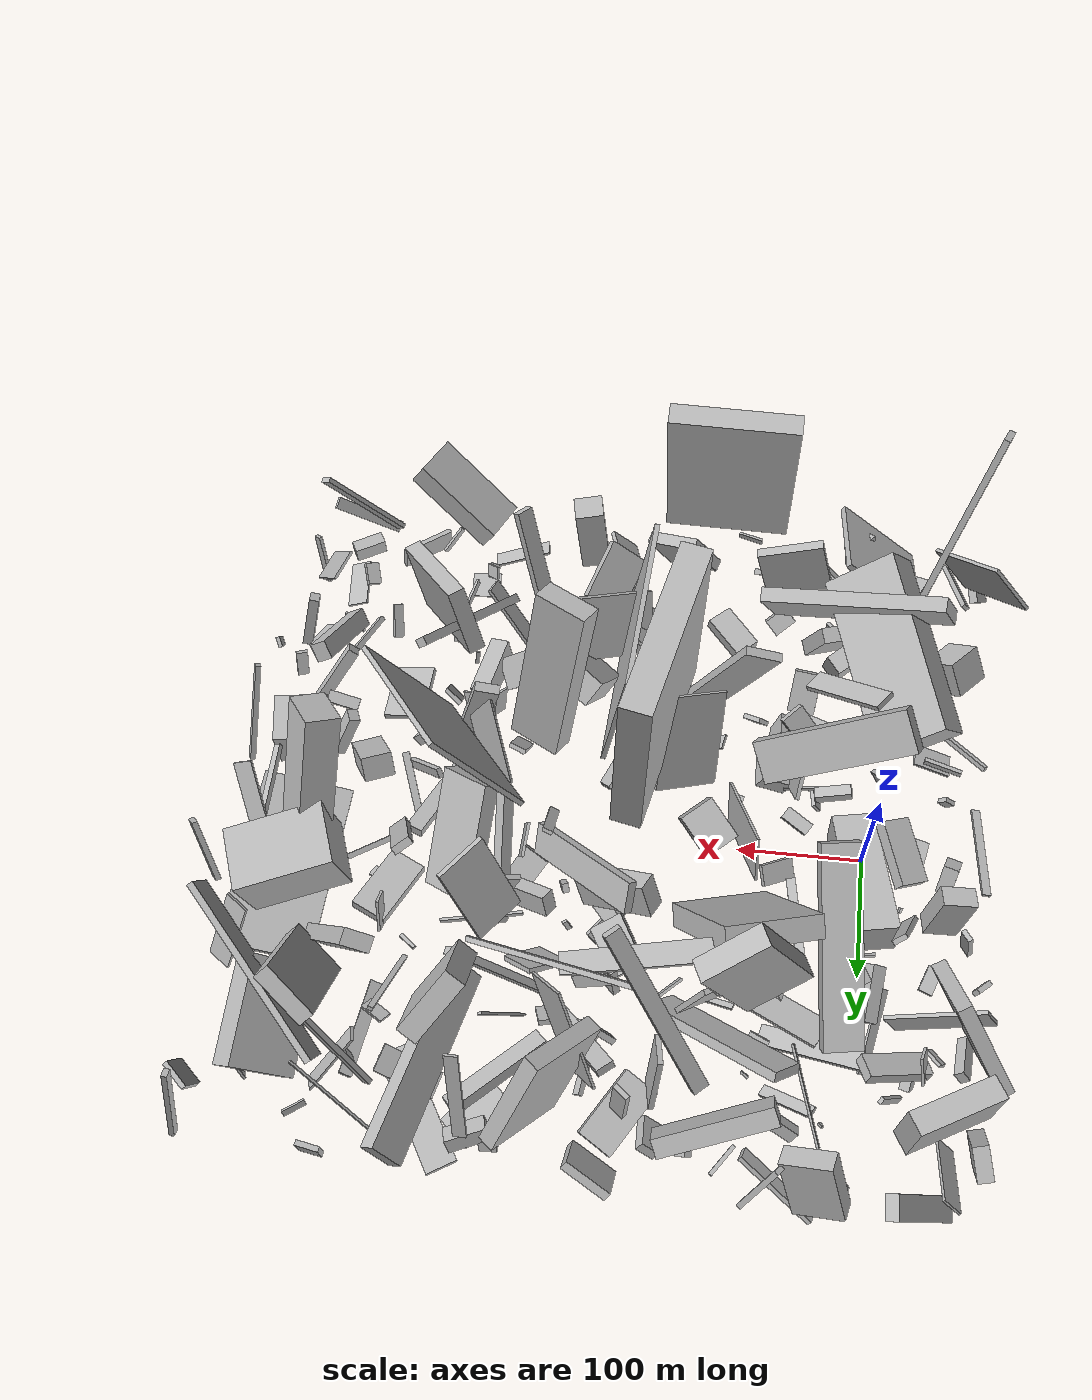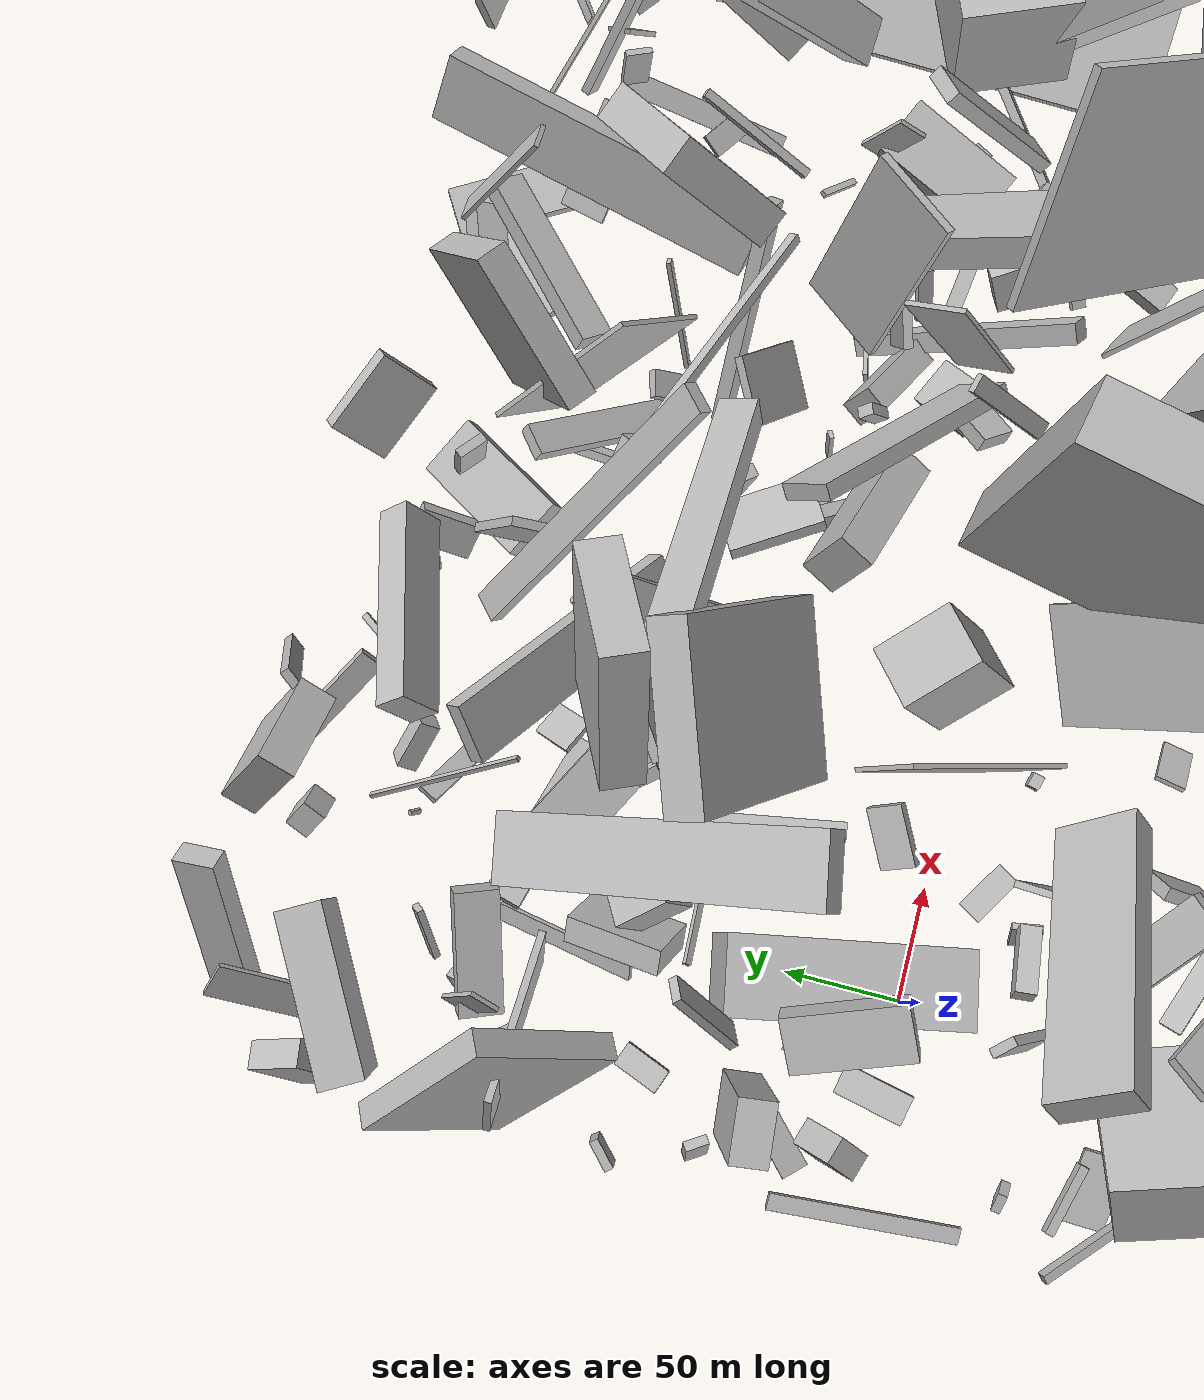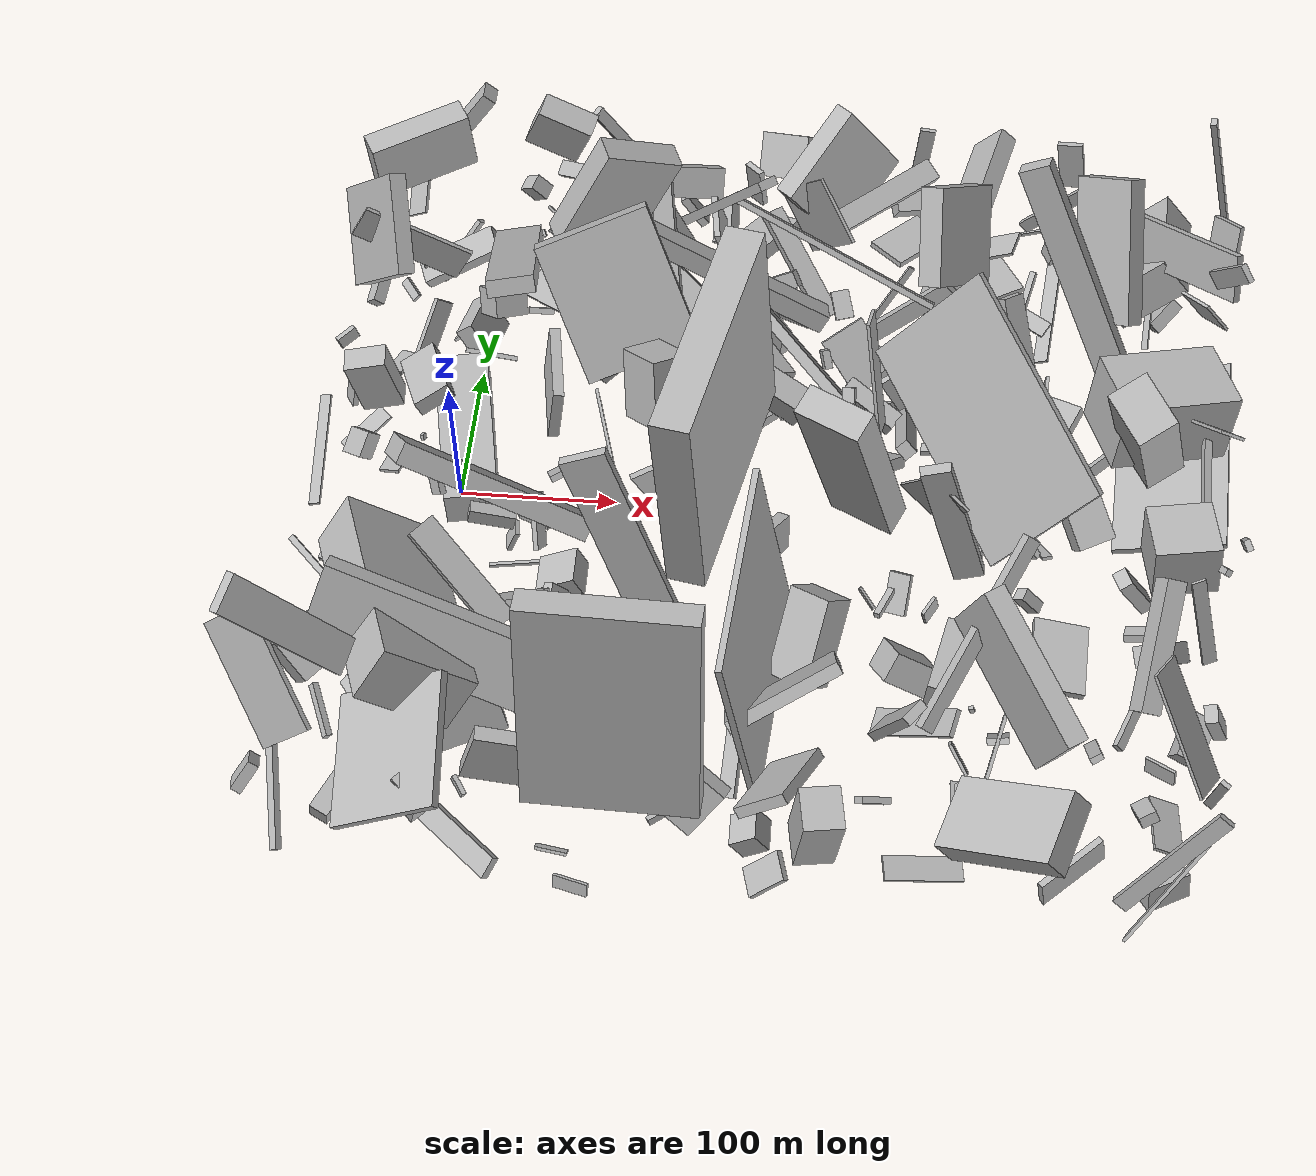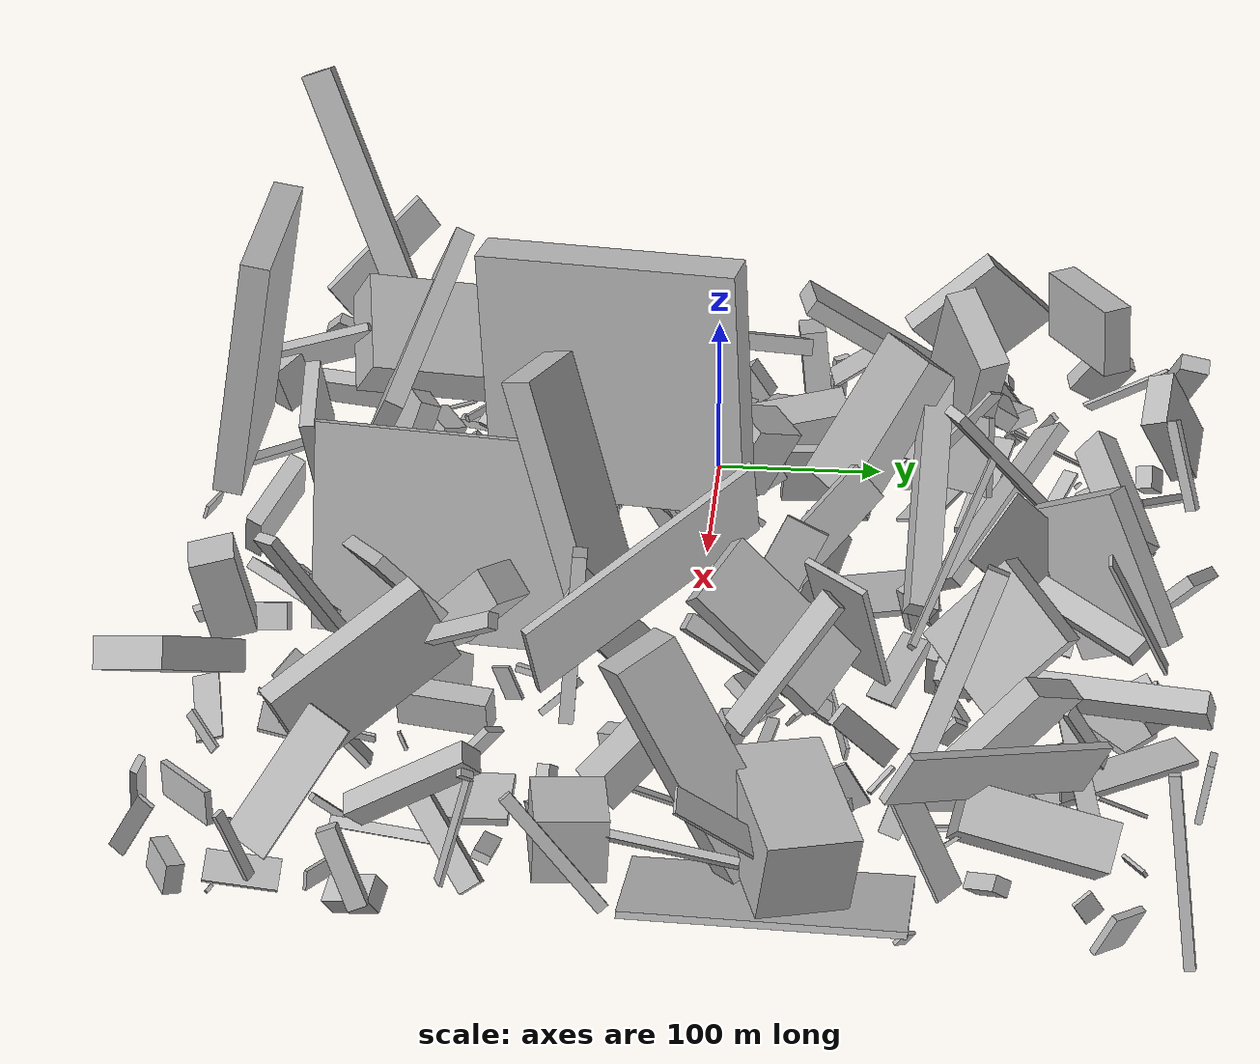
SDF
<sdf version="1.6">
 <world name="default">
  <scene>
   <sky><clouds><speed>12</speed></clouds></sky>
   <ambient>0.4 0.4 0.4 1</ambient>
   <background>0.7 0.7 0.7 1</background>
   <shadows>1</shadows>
  </scene>
  <gravity>0 0 -9.8066</gravity>
  <magnetic_field>6e-06 2.3e-05 -4.2e-05</magnetic_field>
  <physics default="0" name="default_physics" type="ode">
   <ode>
    <solver>
     <type>quick</type>
     <iters>10</iters>
     <sor>1.0</sor>
     <use_dynamic_moi_rescaling>0</use_dynamic_moi_rescaling>
    </solver>
    <constraints>
     <cfm>0</cfm>
     <erp>0.2</erp>
     <contact_max_correcting_vel>100</contact_max_correcting_vel>
     <contact_surface_layer>0.001</contact_surface_layer>
    </constraints>
   </ode>
   <max_step_size>0.004</max_step_size>
   <real_time_factor>1</real_time_factor>
   <real_time_update_rate>250</real_time_update_rate>
  </physics>
  <light name="sun" type="directional">
   <pose>0 0 10 0 0 0</pose>
   <diffuse>0.8 0.8 0.8 1</diffuse>
   <specular>0.2 0.2 0.2 1</specular>
   <attenuation>
    <range>1000</range>
    <constant>0.9</constant>
    <linear>0.01</linear>
    <quadratic>0.001</quadratic>
   </attenuation>
   <direction>-0.5 0.1 -0.9</direction>
  </light>
  <model name="building_1">
   <static>0</static>
   <pose>-53.36776218531265 225.57407513473356 60.18739997213421 0.005135084856677283 -0.0797910758368502 0.5146011915310155</pose>
   <link name="link">
    <gravity>0</gravity>
    <pose>0 0 21.5 0 0 0</pose>
    <collision name="collision"><geometry><box><size>68 18 43</size></box></geometry></collision>
    <visual name="visual">
     <cast_shadows>0</cast_shadows>
     <geometry><box><size>68 18 43</size></box></geometry>
     <material>
      <script>
       <uri>model://HANNAS_wall/materials/scripts</uri>
       <uri>model://HANNAS_wall/materials/textures</uri>
       <name>vrc/HANNAS_wall</name>
      </script>
     </material>
    </visual>
   </link>
  </model>
  <model name="building_2">
   <static>0</static>
   <pose>389.1670423206415 182.27345326725268 71.20522427125024 0.9985611994210901 0.44155829710526634 0.672200436986714</pose>
   <link name="link">
    <gravity>0</gravity>
    <pose>0 0 23.0 0 0 0</pose>
    <collision name="collision"><geometry><box><size>13 94 46</size></box></geometry></collision>
    <visual name="visual">
     <cast_shadows>0</cast_shadows>
     <geometry><box><size>13 94 46</size></box></geometry>
     <material>
      <script>
       <uri>model://HANNAS_wall/materials/scripts</uri>
       <uri>model://HANNAS_wall/materials/textures</uri>
       <name>vrc/HANNAS_wall</name>
      </script>
     </material>
    </visual>
   </link>
  </model>
  <model name="building_3">
   <static>0</static>
   <pose>198.75107616053248 79.6803190435957 21.185578072770227 0.4796749586401037 -0.6003453208512672 0.32458925809940675</pose>
   <link name="link">
    <gravity>0</gravity>
    <pose>0 0 7.5 0 0 0</pose>
    <collision name="collision"><geometry><box><size>5 33 15</size></box></geometry></collision>
    <visual name="visual">
     <cast_shadows>0</cast_shadows>
     <geometry><box><size>5 33 15</size></box></geometry>
     <material>
      <script>
       <uri>model://HANNAS_wall/materials/scripts</uri>
       <uri>model://HANNAS_wall/materials/textures</uri>
       <name>vrc/HANNAS_wall</name>
      </script>
     </material>
    </visual>
   </link>
  </model>
  <model name="building_4">
   <static>0</static>
   <pose>284.6367889503489 41.436290306247784 36.51101400669914 0.7848779041602345 0.5691758990537518 -2.6156911117196264</pose>
   <link name="link">
    <gravity>0</gravity>
    <pose>0 0 5.0 0 0 0</pose>
    <collision name="collision"><geometry><box><size>9 104 10</size></box></geometry></collision>
    <visual name="visual">
     <cast_shadows>0</cast_shadows>
     <geometry><box><size>9 104 10</size></box></geometry>
     <material>
      <script>
       <uri>model://HANNAS_wall/materials/scripts</uri>
       <uri>model://HANNAS_wall/materials/textures</uri>
       <name>vrc/HANNAS_wall</name>
      </script>
     </material>
    </visual>
   </link>
  </model>
  <model name="building_5">
   <static>0</static>
   <pose>303.31625523544255 217.26199748995083 42.439125821296315 -0.0667729580504567 -0.6869832761657249 2.960606714397487</pose>
   <link name="link">
    <gravity>0</gravity>
    <pose>0 0 14.5 0 0 0</pose>
    <collision name="collision"><geometry><box><size>13 150 29</size></box></geometry></collision>
    <visual name="visual">
     <cast_shadows>0</cast_shadows>
     <geometry><box><size>13 150 29</size></box></geometry>
     <material>
      <script>
       <uri>model://HANNAS_wall/materials/scripts</uri>
       <uri>model://HANNAS_wall/materials/textures</uri>
       <name>vrc/HANNAS_wall</name>
      </script>
     </material>
    </visual>
   </link>
  </model>
  <model name="building_6">
   <static>0</static>
   <pose>383.57789830390834 -204.22839032764224 56.90118892235914 1.1419513842508067 -0.03035400887190286 -2.5071396313396574</pose>
   <link name="link">
    <gravity>0</gravity>
    <pose>0 0 50.0 0 0 0</pose>
    <collision name="collision"><geometry><box><size>14 57 100</size></box></geometry></collision>
    <visual name="visual">
     <cast_shadows>0</cast_shadows>
     <geometry><box><size>14 57 100</size></box></geometry>
     <material>
      <script>
       <uri>model://HANNAS_wall/materials/scripts</uri>
       <uri>model://HANNAS_wall/materials/textures</uri>
       <name>vrc/HANNAS_wall</name>
      </script>
     </material>
    </visual>
   </link>
  </model>
  <model name="building_7">
   <static>0</static>
   <pose>-35.37634385524697 -79.82885916683912 56.13320116649942 1.1754656379227297 -0.8605714179726096 0.6549388538264809</pose>
   <link name="link">
    <gravity>0</gravity>
    <pose>0 0 75.0 0 0 0</pose>
    <collision name="collision"><geometry><box><size>36 62 150</size></box></geometry></collision>
    <visual name="visual">
     <cast_shadows>0</cast_shadows>
     <geometry><box><size>36 62 150</size></box></geometry>
     <material>
      <script>
       <uri>model://HANNAS_wall/materials/scripts</uri>
       <uri>model://HANNAS_wall/materials/textures</uri>
       <name>vrc/HANNAS_wall</name>
      </script>
     </material>
    </visual>
   </link>
  </model>
  <model name="building_8">
   <static>0</static>
   <pose>102.65849821187052 175.11031111418234 38.70035308174231 0.5453687690652936 -0.6083412496454647 0.6652943868384229</pose>
   <link name="link">
    <gravity>0</gravity>
    <pose>0 0 4.0 0 0 0</pose>
    <collision name="collision"><geometry><box><size>27 123 8</size></box></geometry></collision>
    <visual name="visual">
     <cast_shadows>0</cast_shadows>
     <geometry><box><size>27 123 8</size></box></geometry>
     <material>
      <script>
       <uri>model://HANNAS_wall/materials/scripts</uri>
       <uri>model://HANNAS_wall/materials/textures</uri>
       <name>vrc/HANNAS_wall</name>
      </script>
     </material>
    </visual>
   </link>
  </model>
  <model name="building_9">
   <static>0</static>
   <pose>304.2907745728655 -58.22759774324887 75.836507082875 1.3048529523502757 0.08205028797164456 1.6205734096075415</pose>
   <link name="link">
    <gravity>0</gravity>
    <pose>0 0 9.5 0 0 0</pose>
    <collision name="collision"><geometry><box><size>8 95 19</size></box></geometry></collision>
    <visual name="visual">
     <cast_shadows>0</cast_shadows>
     <geometry><box><size>8 95 19</size></box></geometry>
     <material>
      <script>
       <uri>model://HANNAS_wall/materials/scripts</uri>
       <uri>model://HANNAS_wall/materials/textures</uri>
       <name>vrc/HANNAS_wall</name>
      </script>
     </material>
    </visual>
   </link>
  </model>
  <model name="building_10">
   <static>0</static>
   <pose>199.75939614173308 -143.61442118987642 66.97941842244322 1.405398066791633 0.032576267483294154 1.5148054013510757</pose>
   <link name="link">
    <gravity>0</gravity>
    <pose>0 0 2.0 0 0 0</pose>
    <collision name="collision"><geometry><box><size>150 128 4</size></box></geometry></collision>
    <visual name="visual">
     <cast_shadows>0</cast_shadows>
     <geometry><box><size>150 128 4</size></box></geometry>
     <material>
      <script>
       <uri>model://HANNAS_wall/materials/scripts</uri>
       <uri>model://HANNAS_wall/materials/textures</uri>
       <name>vrc/HANNAS_wall</name>
      </script>
     </material>
    </visual>
   </link>
  </model>
  <model name="building_11">
   <static>0</static>
   <pose>439.47429550103556 3.416906068397626 78.5099401154982 0.8400165274937765 -1.0716157159774935 -1.8438272145721253</pose>
   <link name="link">
    <gravity>0</gravity>
    <pose>0 0 18.0 0 0 0</pose>
    <collision name="collision"><geometry><box><size>132 27 36</size></box></geometry></collision>
    <visual name="visual">
     <cast_shadows>0</cast_shadows>
     <geometry><box><size>132 27 36</size></box></geometry>
     <material>
      <script>
       <uri>model://HANNAS_wall/materials/scripts</uri>
       <uri>model://HANNAS_wall/materials/textures</uri>
       <name>vrc/HANNAS_wall</name>
      </script>
     </material>
    </visual>
   </link>
  </model>
  <model name="building_12">
   <static>0</static>
   <pose>17.908233750072107 31.308224539765238 23.376434881511734 -1.5877761756979039 -0.14215236009023843 1.7673965393844318</pose>
   <link name="link">
    <gravity>0</gravity>
    <pose>0 0 17.0 0 0 0</pose>
    <collision name="collision"><geometry><box><size>106 30 34</size></box></geometry></collision>
    <visual name="visual">
     <cast_shadows>0</cast_shadows>
     <geometry><box><size>106 30 34</size></box></geometry>
     <material>
      <script>
       <uri>model://HANNAS_wall/materials/scripts</uri>
       <uri>model://HANNAS_wall/materials/textures</uri>
       <name>vrc/HANNAS_wall</name>
      </script>
     </material>
    </visual>
   </link>
  </model>
  <model name="building_13">
   <static>0</static>
   <pose>87.20154148661504 -56.308859797103885 48.33672092008506 -0.8636523174317932 0.6482194262004974 2.0591435352742304</pose>
   <link name="link">
    <gravity>0</gravity>
    <pose>0 0 64.0 0 0 0</pose>
    <collision name="collision"><geometry><box><size>35 14 128</size></box></geometry></collision>
    <visual name="visual">
     <cast_shadows>0</cast_shadows>
     <geometry><box><size>35 14 128</size></box></geometry>
     <material>
      <script>
       <uri>model://HANNAS_wall/materials/scripts</uri>
       <uri>model://HANNAS_wall/materials/textures</uri>
       <name>vrc/HANNAS_wall</name>
      </script>
     </material>
    </visual>
   </link>
  </model>
  <model name="building_14">
   <static>0</static>
   <pose>284.95008669527004 -123.20067489249129 24.118417519923735 0.9040310014824263 0.587848842570337 0.025496455703872795</pose>
   <link name="link">
    <gravity>0</gravity>
    <pose>0 0 13.5 0 0 0</pose>
    <collision name="collision"><geometry><box><size>29 19 27</size></box></geometry></collision>
    <visual name="visual">
     <cast_shadows>0</cast_shadows>
     <geometry><box><size>29 19 27</size></box></geometry>
     <material>
      <script>
       <uri>model://HANNAS_wall/materials/scripts</uri>
       <uri>model://HANNAS_wall/materials/textures</uri>
       <name>vrc/HANNAS_wall</name>
      </script>
     </material>
    </visual>
   </link>
  </model>
  <model name="building_15">
   <static>0</static>
   <pose>454.4709440644848 -47.34934510154349 33.18940693092354 -0.06209678522897362 -0.0214763122014824 0.1641329490324192</pose>
   <link name="link">
    <gravity>0</gravity>
    <pose>0 0 19.0 0 0 0</pose>
    <collision name="collision"><geometry><box><size>41 39 38</size></box></geometry></collision>
    <visual name="visual">
     <cast_shadows>0</cast_shadows>
     <geometry><box><size>41 39 38</size></box></geometry>
     <material>
      <script>
       <uri>model://HANNAS_wall/materials/scripts</uri>
       <uri>model://HANNAS_wall/materials/textures</uri>
       <name>vrc/HANNAS_wall</name>
      </script>
     </material>
    </visual>
   </link>
  </model>
  <model name="building_16">
   <static>0</static>
   <pose>372.4997254167869 144.98639615702987 87.56449912963286 1.093936848090944 0.2971415132475192 1.3772643937018203</pose>
   <link name="link">
    <gravity>0</gravity>
    <pose>0 0 10.5 0 0 0</pose>
    <collision name="collision"><geometry><box><size>12 150 21</size></box></geometry></collision>
    <visual name="visual">
     <cast_shadows>0</cast_shadows>
     <geometry><box><size>12 150 21</size></box></geometry>
     <material>
      <script>
       <uri>model://HANNAS_wall/materials/scripts</uri>
       <uri>model://HANNAS_wall/materials/textures</uri>
       <name>vrc/HANNAS_wall</name>
      </script>
     </material>
    </visual>
   </link>
  </model>
  <model name="building_17">
   <static>0</static>
   <pose>279.39121196128315 -73.68338280042434 27.057425863141347 -1.5437950387450834 0.12738077929289962 2.7752094283203967</pose>
   <link name="link">
    <gravity>0</gravity>
    <pose>0 0 11.0 0 0 0</pose>
    <collision name="collision"><geometry><box><size>4 4 22</size></box></geometry></collision>
    <visual name="visual">
     <cast_shadows>0</cast_shadows>
     <geometry><box><size>4 4 22</size></box></geometry>
     <material>
      <script>
       <uri>model://HANNAS_wall/materials/scripts</uri>
       <uri>model://HANNAS_wall/materials/textures</uri>
       <name>vrc/HANNAS_wall</name>
      </script>
     </material>
    </visual>
   </link>
  </model>
  <model name="building_18">
   <static>0</static>
   <pose>-22.268983301284038 -231.2250630682057 27.73519998412533 1.3262885029804963 0.15194075545650287 -2.017616570688222</pose>
   <link name="link">
    <gravity>0</gravity>
    <pose>0 0 6.0 0 0 0</pose>
    <collision name="collision"><geometry><box><size>71 16 12</size></box></geometry></collision>
    <visual name="visual">
     <cast_shadows>0</cast_shadows>
     <geometry><box><size>71 16 12</size></box></geometry>
     <material>
      <script>
       <uri>model://HANNAS_wall/materials/scripts</uri>
       <uri>model://HANNAS_wall/materials/textures</uri>
       <name>vrc/HANNAS_wall</name>
      </script>
     </material>
    </visual>
   </link>
  </model>
  <model name="building_19">
   <static>0</static>
   <pose>433.5303821482553 90.47722792879836 49.387675971761816 1.0917649847006579 -1.3912077532217386 0.8278886072970991</pose>
   <link name="link">
    <gravity>0</gravity>
    <pose>0 0 25.5 0 0 0</pose>
    <collision name="collision"><geometry><box><size>49 78 51</size></box></geometry></collision>
    <visual name="visual">
     <cast_shadows>0</cast_shadows>
     <geometry><box><size>49 78 51</size></box></geometry>
     <material>
      <script>
       <uri>model://HANNAS_wall/materials/scripts</uri>
       <uri>model://HANNAS_wall/materials/textures</uri>
       <name>vrc/HANNAS_wall</name>
      </script>
     </material>
    </visual>
   </link>
  </model>
  <model name="building_20">
   <static>0</static>
   <pose>313.14509885217643 84.16151838064405 54.130318871678924 0.7341440670826089 0.3880051204111599 -0.5609156109944797</pose>
   <link name="link">
    <gravity>0</gravity>
    <pose>0 0 46.0 0 0 0</pose>
    <collision name="collision"><geometry><box><size>45 13 92</size></box></geometry></collision>
    <visual name="visual">
     <cast_shadows>0</cast_shadows>
     <geometry><box><size>45 13 92</size></box></geometry>
     <material>
      <script>
       <uri>model://HANNAS_wall/materials/scripts</uri>
       <uri>model://HANNAS_wall/materials/textures</uri>
       <name>vrc/HANNAS_wall</name>
      </script>
     </material>
    </visual>
   </link>
  </model>
  <model name="building_21">
   <static>0</static>
   <pose>110.93591590267224 76.60733210260125 53.27177881163373 0.3182430208783145 -0.6186728134676815 -1.4065448646998073</pose>
   <link name="link">
    <gravity>0</gravity>
    <pose>0 0 47.0 0 0 0</pose>
    <collision name="collision"><geometry><box><size>18 76 94</size></box></geometry></collision>
    <visual name="visual">
     <cast_shadows>0</cast_shadows>
     <geometry><box><size>18 76 94</size></box></geometry>
     <material>
      <script>
       <uri>model://HANNAS_wall/materials/scripts</uri>
       <uri>model://HANNAS_wall/materials/textures</uri>
       <name>vrc/HANNAS_wall</name>
      </script>
     </material>
    </visual>
   </link>
  </model>
  <model name="building_22">
   <static>0</static>
   <pose>172.64674540773686 -43.25319528702598 83.02658972019377 0.050844142049338854 -0.028690400749932152 -0.19970684529259325</pose>
   <link name="link">
    <gravity>0</gravity>
    <pose>0 0 75.0 0 0 0</pose>
    <collision name="collision"><geometry><box><size>24 150 150</size></box></geometry></collision>
    <visual name="visual">
     <cast_shadows>0</cast_shadows>
     <geometry><box><size>24 150 150</size></box></geometry>
     <material>
      <script>
       <uri>model://HANNAS_wall/materials/scripts</uri>
       <uri>model://HANNAS_wall/materials/textures</uri>
       <name>vrc/HANNAS_wall</name>
      </script>
     </material>
    </visual>
   </link>
  </model>
  <model name="building_23">
   <static>0</static>
   <pose>394.47325753871127 -260.15664879753274 20.16209631838445 1.6265225817026203 0.11527512826865162 -2.408205424874494</pose>
   <link name="link">
    <gravity>0</gravity>
    <pose>0 0 2.0 0 0 0</pose>
    <collision name="collision"><geometry><box><size>46 20 4</size></box></geometry></collision>
    <visual name="visual">
     <cast_shadows>0</cast_shadows>
     <geometry><box><size>46 20 4</size></box></geometry>
     <material>
      <script>
       <uri>model://HANNAS_wall/materials/scripts</uri>
       <uri>model://HANNAS_wall/materials/textures</uri>
       <name>vrc/HANNAS_wall</name>
      </script>
     </material>
    </visual>
   </link>
  </model>
  <model name="building_24">
   <static>0</static>
   <pose>368.52958089554613 -74.11320984580192 97.15929962290211 -0.8549433892645674 -0.9122947049014914 0.001873142515514601</pose>
   <link name="link">
    <gravity>0</gravity>
    <pose>0 0 75.0 0 0 0</pose>
    <collision name="collision"><geometry><box><size>96 4 150</size></box></geometry></collision>
    <visual name="visual">
     <cast_shadows>0</cast_shadows>
     <geometry><box><size>96 4 150</size></box></geometry>
     <material>
      <script>
       <uri>model://HANNAS_wall/materials/scripts</uri>
       <uri>model://HANNAS_wall/materials/textures</uri>
       <name>vrc/HANNAS_wall</name>
      </script>
     </material>
    </visual>
   </link>
  </model>
  <model name="building_25">
   <static>0</static>
   <pose>333.89373754074586 -3.4831397383688563 30.375352631277753 1.3567494582369424 1.3775928349575601 0.9793957775255684</pose>
   <link name="link">
    <gravity>0</gravity>
    <pose>0 0 6.5 0 0 0</pose>
    <collision name="collision"><geometry><box><size>8 75 13</size></box></geometry></collision>
    <visual name="visual">
     <cast_shadows>0</cast_shadows>
     <geometry><box><size>8 75 13</size></box></geometry>
     <material>
      <script>
       <uri>model://HANNAS_wall/materials/scripts</uri>
       <uri>model://HANNAS_wall/materials/textures</uri>
       <name>vrc/HANNAS_wall</name>
      </script>
     </material>
    </visual>
   </link>
  </model>
  <model name="building_26">
   <static>0</static>
   <pose>251.39991961904443 -155.02052538114827 63.008092974921894 2.060386175716649 -0.8365651261437685 -1.4709617958473813</pose>
   <link name="link">
    <gravity>0</gravity>
    <pose>0 0 37.0 0 0 0</pose>
    <collision name="collision"><geometry><box><size>52 8 74</size></box></geometry></collision>
    <visual name="visual">
     <cast_shadows>0</cast_shadows>
     <geometry><box><size>52 8 74</size></box></geometry>
     <material>
      <script>
       <uri>model://HANNAS_wall/materials/scripts</uri>
       <uri>model://HANNAS_wall/materials/textures</uri>
       <name>vrc/HANNAS_wall</name>
      </script>
     </material>
    </visual>
   </link>
  </model>
  <model name="building_27">
   <static>0</static>
   <pose>216.03180781575657 -268.60667016050047 23.911611604162815 -1.8597437752975214 0.7883690492993546 -3.0548124770656906</pose>
   <link name="link">
    <gravity>0</gravity>
    <pose>0 0 9.0 0 0 0</pose>
    <collision name="collision"><geometry><box><size>28 4 18</size></box></geometry></collision>
    <visual name="visual">
     <cast_shadows>0</cast_shadows>
     <geometry><box><size>28 4 18</size></box></geometry>
     <material>
      <script>
       <uri>model://HANNAS_wall/materials/scripts</uri>
       <uri>model://HANNAS_wall/materials/textures</uri>
       <name>vrc/HANNAS_wall</name>
      </script>
     </material>
    </visual>
   </link>
  </model>
  <model name="building_28">
   <static>0</static>
   <pose>101.53101039245655 234.386721790168 41.01600732419431 0.6299060999841484 -0.25945646761517815 -2.8453049823105316</pose>
   <link name="link">
    <gravity>0</gravity>
    <pose>0 0 10.5 0 0 0</pose>
    <collision name="collision"><geometry><box><size>90 15 21</size></box></geometry></collision>
    <visual name="visual">
     <cast_shadows>0</cast_shadows>
     <geometry><box><size>90 15 21</size></box></geometry>
     <material>
      <script>
       <uri>model://HANNAS_wall/materials/scripts</uri>
       <uri>model://HANNAS_wall/materials/textures</uri>
       <name>vrc/HANNAS_wall</name>
      </script>
     </material>
    </visual>
   </link>
  </model>
  <model name="building_29">
   <static>0</static>
   <pose>201.60415786806828 192.60456864345127 9.658196869475445 -0.7237716845833972 0.19765439289558648 1.4251949318037043</pose>
   <link name="link">
    <gravity>0</gravity>
    <pose>0 0 3.5 0 0 0</pose>
    <collision name="collision"><geometry><box><size>47 4 7</size></box></geometry></collision>
    <visual name="visual">
     <cast_shadows>0</cast_shadows>
     <geometry><box><size>47 4 7</size></box></geometry>
     <material>
      <script>
       <uri>model://HANNAS_wall/materials/scripts</uri>
       <uri>model://HANNAS_wall/materials/textures</uri>
       <name>vrc/HANNAS_wall</name>
      </script>
     </material>
    </visual>
   </link>
  </model>
  <model name="building_30">
   <static>0</static>
   <pose>383.60919287319524 -109.015194323443 19.612738985877396 3.0942228701523478 -0.1732060797067562 3.1179830220011135</pose>
   <link name="link">
    <gravity>0</gravity>
    <pose>0 0 2.5 0 0 0</pose>
    <collision name="collision"><geometry><box><size>34 49 5</size></box></geometry></collision>
    <visual name="visual">
     <cast_shadows>0</cast_shadows>
     <geometry><box><size>34 49 5</size></box></geometry>
     <material>
      <script>
       <uri>model://HANNAS_wall/materials/scripts</uri>
       <uri>model://HANNAS_wall/materials/textures</uri>
       <name>vrc/HANNAS_wall</name>
      </script>
     </material>
    </visual>
   </link>
  </model>
  <model name="building_31">
   <static>0</static>
   <pose>320.92424244755534 191.32142856800064 69.17375716509056 0.9498713634668221 -0.41264947051410455 -0.45686577443252985</pose>
   <link name="link">
    <gravity>0</gravity>
    <pose>0 0 28.0 0 0 0</pose>
    <collision name="collision"><geometry><box><size>17 64 56</size></box></geometry></collision>
    <visual name="visual">
     <cast_shadows>0</cast_shadows>
     <geometry><box><size>17 64 56</size></box></geometry>
     <material>
      <script>
       <uri>model://HANNAS_wall/materials/scripts</uri>
       <uri>model://HANNAS_wall/materials/textures</uri>
       <name>vrc/HANNAS_wall</name>
      </script>
     </material>
    </visual>
   </link>
  </model>
  <model name="building_32">
   <static>0</static>
   <pose>91.9595428296833 -193.96650068513972 73.536874218739 -0.9692957055522151 -1.053303232051189 0.8513703144813367</pose>
   <link name="link">
    <gravity>0</gravity>
    <pose>0 0 75.0 0 0 0</pose>
    <collision name="collision"><geometry><box><size>46 12 150</size></box></geometry></collision>
    <visual name="visual">
     <cast_shadows>0</cast_shadows>
     <geometry><box><size>46 12 150</size></box></geometry>
     <material>
      <script>
       <uri>model://HANNAS_wall/materials/scripts</uri>
       <uri>model://HANNAS_wall/materials/textures</uri>
       <name>vrc/HANNAS_wall</name>
      </script>
     </material>
    </visual>
   </link>
  </model>
  <model name="building_33">
   <static>0</static>
   <pose>-71.28533931900245 -152.53147932357862 36.358138684460314 0.6634080557702714 -0.13776527083720133 0.8522295252504025</pose>
   <link name="link">
    <gravity>0</gravity>
    <pose>0 0 14.5 0 0 0</pose>
    <collision name="collision"><geometry><box><size>32 29 29</size></box></geometry></collision>
    <visual name="visual">
     <cast_shadows>0</cast_shadows>
     <geometry><box><size>32 29 29</size></box></geometry>
     <material>
      <script>
       <uri>model://HANNAS_wall/materials/scripts</uri>
       <uri>model://HANNAS_wall/materials/textures</uri>
       <name>vrc/HANNAS_wall</name>
      </script>
     </material>
    </visual>
   </link>
  </model>
  <model name="building_34">
   <static>0</static>
   <pose>-33.68719308623065 -143.24230125763256 4.944371780354979 1.5215713787839003 0.035612869714398254 1.3541824433385397</pose>
   <link name="link">
    <gravity>0</gravity>
    <pose>0 0 4.0 0 0 0</pose>
    <collision name="collision"><geometry><box><size>42 5 8</size></box></geometry></collision>
    <visual name="visual">
     <cast_shadows>0</cast_shadows>
     <geometry><box><size>42 5 8</size></box></geometry>
     <material>
      <script>
       <uri>model://HANNAS_wall/materials/scripts</uri>
       <uri>model://HANNAS_wall/materials/textures</uri>
       <name>vrc/HANNAS_wall</name>
      </script>
     </material>
    </visual>
   </link>
  </model>
  <model name="building_35">
   <static>0</static>
   <pose>16.61682761326499 177.0175969989586 53.94088714772255 -0.963043995409521 0.08274046744521123 -2.9488357224455637</pose>
   <link name="link">
    <gravity>0</gravity>
    <pose>0 0 75.0 0 0 0</pose>
    <collision name="collision"><geometry><box><size>30 11 150</size></box></geometry></collision>
    <visual name="visual">
     <cast_shadows>0</cast_shadows>
     <geometry><box><size>30 11 150</size></box></geometry>
     <material>
      <script>
       <uri>model://HANNAS_wall/materials/scripts</uri>
       <uri>model://HANNAS_wall/materials/textures</uri>
       <name>vrc/HANNAS_wall</name>
      </script>
     </material>
    </visual>
   </link>
  </model>
  <model name="building_36">
   <static>0</static>
   <pose>49.215279147849266 -135.31893218015455 49.75282604158086 0.00441759923636645 -1.0238554763739798 -0.6480272119935063</pose>
   <link name="link">
    <gravity>0</gravity>
    <pose>0 0 38.5 0 0 0</pose>
    <collision name="collision"><geometry><box><size>4 19 77</size></box></geometry></collision>
    <visual name="visual">
     <cast_shadows>0</cast_shadows>
     <geometry><box><size>4 19 77</size></box></geometry>
     <material>
      <script>
       <uri>model://HANNAS_wall/materials/scripts</uri>
       <uri>model://HANNAS_wall/materials/textures</uri>
       <name>vrc/HANNAS_wall</name>
      </script>
     </material>
    </visual>
   </link>
  </model>
  <model name="building_37">
   <static>0</static>
   <pose>227.4339325967488 160.75758974860616 21.633996870139942 1.4820337109693011 -0.6296216612123448 1.9066985746679765</pose>
   <link name="link">
    <gravity>0</gravity>
    <pose>0 0 6.0 0 0 0</pose>
    <collision name="collision"><geometry><box><size>19 4 12</size></box></geometry></collision>
    <visual name="visual">
     <cast_shadows>0</cast_shadows>
     <geometry><box><size>19 4 12</size></box></geometry>
     <material>
      <script>
       <uri>model://HANNAS_wall/materials/scripts</uri>
       <uri>model://HANNAS_wall/materials/textures</uri>
       <name>vrc/HANNAS_wall</name>
      </script>
     </material>
    </visual>
   </link>
  </model>
  <model name="building_38">
   <static>0</static>
   <pose>277.00681764101626 -214.70572314998705 13.386953115068813 2.1299096249763987 0.4248775620785343 0.31512837918882247</pose>
   <link name="link">
    <gravity>0</gravity>
    <pose>0 0 2.0 0 0 0</pose>
    <collision name="collision"><geometry><box><size>20 9 4</size></box></geometry></collision>
    <visual name="visual">
     <cast_shadows>0</cast_shadows>
     <geometry><box><size>20 9 4</size></box></geometry>
     <material>
      <script>
       <uri>model://HANNAS_wall/materials/scripts</uri>
       <uri>model://HANNAS_wall/materials/textures</uri>
       <name>vrc/HANNAS_wall</name>
      </script>
     </material>
    </visual>
   </link>
  </model>
  <model name="building_39">
   <static>0</static>
   <pose>131.83799169275468 -269.7795638189098 79.52496255320497 0.168060298486547 -0.0031725530876417518 3.120574097686258</pose>
   <link name="link">
    <gravity>0</gravity>
    <pose>0 0 75.0 0 0 0</pose>
    <collision name="collision"><geometry><box><size>101 17 150</size></box></geometry></collision>
    <visual name="visual">
     <cast_shadows>0</cast_shadows>
     <geometry><box><size>101 17 150</size></box></geometry>
     <material>
      <script>
       <uri>model://HANNAS_wall/materials/scripts</uri>
       <uri>model://HANNAS_wall/materials/textures</uri>
       <name>vrc/HANNAS_wall</name>
      </script>
     </material>
    </visual>
   </link>
  </model>
  <model name="building_40">
   <static>0</static>
   <pose>159.2606686317211 123.14197695540746 84.69212079845002 1.9186344228700432 -0.5300730237977904 3.1108311479582635</pose>
   <link name="link">
    <gravity>0</gravity>
    <pose>0 0 8.5 0 0 0</pose>
    <collision name="collision"><geometry><box><size>150 13 17</size></box></geometry></collision>
    <visual name="visual">
     <cast_shadows>0</cast_shadows>
     <geometry><box><size>150 13 17</size></box></geometry>
     <material>
      <script>
       <uri>model://HANNAS_wall/materials/scripts</uri>
       <uri>model://HANNAS_wall/materials/textures</uri>
       <name>vrc/HANNAS_wall</name>
      </script>
     </material>
    </visual>
   </link>
  </model>
  <model name="building_41">
   <static>0</static>
   <pose>318.70690928476915 237.3415982311377 3.370481435347543 0.01441911845690003 -0.00407596934792434 2.1134964530169524</pose>
   <link name="link">
    <gravity>0</gravity>
    <pose>0 0 2.0 0 0 0</pose>
    <collision name="collision"><geometry><box><size>97 24 4</size></box></geometry></collision>
    <visual name="visual">
     <cast_shadows>0</cast_shadows>
     <geometry><box><size>97 24 4</size></box></geometry>
     <material>
      <script>
       <uri>model://HANNAS_wall/materials/scripts</uri>
       <uri>model://HANNAS_wall/materials/textures</uri>
       <name>vrc/HANNAS_wall</name>
      </script>
     </material>
    </visual>
   </link>
  </model>
  <model name="building_42">
   <static>0</static>
   <pose>315.7468793521727 47.71879672735081 14.274376958286426 -0.03754337181879618 -0.14325123115436697 -0.12068900066509265</pose>
   <link name="link">
    <gravity>0</gravity>
    <pose>0 0 2.0 0 0 0</pose>
    <collision name="collision"><geometry><box><size>48 7 4</size></box></geometry></collision>
    <visual name="visual">
     <cast_shadows>0</cast_shadows>
     <geometry><box><size>48 7 4</size></box></geometry>
     <material>
      <script>
       <uri>model://HANNAS_wall/materials/scripts</uri>
       <uri>model://HANNAS_wall/materials/textures</uri>
       <name>vrc/HANNAS_wall</name>
      </script>
     </material>
    </visual>
   </link>
  </model>
  <model name="building_43">
   <static>0</static>
   <pose>274.05725989623136 34.01783897374855 14.162420916816949 1.9348309743036527 -0.5289153004255487 -2.2191907962247406</pose>
   <link name="link">
    <gravity>0</gravity>
    <pose>0 0 11.0 0 0 0</pose>
    <collision name="collision"><geometry><box><size>29 8 22</size></box></geometry></collision>
    <visual name="visual">
     <cast_shadows>0</cast_shadows>
     <geometry><box><size>29 8 22</size></box></geometry>
     <material>
      <script>
       <uri>model://HANNAS_wall/materials/scripts</uri>
       <uri>model://HANNAS_wall/materials/textures</uri>
       <name>vrc/HANNAS_wall</name>
      </script>
     </material>
    </visual>
   </link>
  </model>
  <model name="building_44">
   <static>0</static>
   <pose>64.78497882888301 -234.77074590187974 39.113507703404125 0.26298915779767845 -0.10905409287850117 1.6149011173050838</pose>
   <link name="link">
    <gravity>0</gravity>
    <pose>0 0 24.5 0 0 0</pose>
    <collision name="collision"><geometry><box><size>9 55 49</size></box></geometry></collision>
    <visual name="visual">
     <cast_shadows>0</cast_shadows>
     <geometry><box><size>9 55 49</size></box></geometry>
     <material>
      <script>
       <uri>model://HANNAS_wall/materials/scripts</uri>
       <uri>model://HANNAS_wall/materials/textures</uri>
       <name>vrc/HANNAS_wall</name>
      </script>
     </material>
    </visual>
   </link>
  </model>
  <model name="building_45">
   <static>0</static>
   <pose>-2.3374599007737764 -46.32025745562147 57.74331357457602 -0.7066894888824856 0.2311759284176999 0.6486493947640833</pose>
   <link name="link">
    <gravity>0</gravity>
    <pose>0 0 13.5 0 0 0</pose>
    <collision name="collision"><geometry><box><size>4 12 27</size></box></geometry></collision>
    <visual name="visual">
     <cast_shadows>0</cast_shadows>
     <geometry><box><size>4 12 27</size></box></geometry>
     <material>
      <script>
       <uri>model://HANNAS_wall/materials/scripts</uri>
       <uri>model://HANNAS_wall/materials/textures</uri>
       <name>vrc/HANNAS_wall</name>
      </script>
     </material>
    </visual>
   </link>
  </model>
  <model name="building_46">
   <static>0</static>
   <pose>434.64756908951847 232.62956048191958 39.27638448647449 1.2205472409256723 0.8111524950324286 -0.32034500634459095</pose>
   <link name="link">
    <gravity>0</gravity>
    <pose>0 0 40.5 0 0 0</pose>
    <collision name="collision"><geometry><box><size>27 51 81</size></box></geometry></collision>
    <visual name="visual">
     <cast_shadows>0</cast_shadows>
     <geometry><box><size>27 51 81</size></box></geometry>
     <material>
      <script>
       <uri>model://HANNAS_wall/materials/scripts</uri>
       <uri>model://HANNAS_wall/materials/textures</uri>
       <name>vrc/HANNAS_wall</name>
      </script>
     </material>
    </visual>
   </link>
  </model>
  <model name="building_47">
   <static>0</static>
   <pose>228.510647873353 148.22319668001188 87.98290972498766 0.5209752103249604 -0.8978062479586 0.8376059530907116</pose>
   <link name="link">
    <gravity>0</gravity>
    <pose>0 0 2.0 0 0 0</pose>
    <collision name="collision"><geometry><box><size>4 144 4</size></box></geometry></collision>
    <visual name="visual">
     <cast_shadows>0</cast_shadows>
     <geometry><box><size>4 144 4</size></box></geometry>
     <material>
      <script>
       <uri>model://HANNAS_wall/materials/scripts</uri>
       <uri>model://HANNAS_wall/materials/textures</uri>
       <name>vrc/HANNAS_wall</name>
      </script>
     </material>
    </visual>
   </link>
  </model>
  <model name="building_48">
   <static>0</static>
   <pose>475.56276790490176 -95.75335472274831 97.16094596552546 -0.7807655237917941 -0.6749512489655869 1.0410163484661379</pose>
   <link name="link">
    <gravity>0</gravity>
    <pose>0 0 2.0 0 0 0</pose>
    <collision name="collision"><geometry><box><size>4 8 4</size></box></geometry></collision>
    <visual name="visual">
     <cast_shadows>0</cast_shadows>
     <geometry><box><size>4 8 4</size></box></geometry>
     <material>
      <script>
       <uri>model://HANNAS_wall/materials/scripts</uri>
       <uri>model://HANNAS_wall/materials/textures</uri>
       <name>vrc/HANNAS_wall</name>
      </script>
     </material>
    </visual>
   </link>
  </model>
  <model name="building_49">
   <static>0</static>
   <pose>344.60255442947926 -113.049276215063 17.49550386068492 -0.5447663231419287 -0.47890523572554733 -0.5494487582894221</pose>
   <link name="link">
    <gravity>0</gravity>
    <pose>0 0 11.5 0 0 0</pose>
    <collision name="collision"><geometry><box><size>16 4 23</size></box></geometry></collision>
    <visual name="visual">
     <cast_shadows>0</cast_shadows>
     <geometry><box><size>16 4 23</size></box></geometry>
     <material>
      <script>
       <uri>model://HANNAS_wall/materials/scripts</uri>
       <uri>model://HANNAS_wall/materials/textures</uri>
       <name>vrc/HANNAS_wall</name>
      </script>
     </material>
    </visual>
   </link>
  </model>
  <model name="building_50">
   <static>0</static>
   <pose>-50.007280251557816 -116.54742318687431 30.07060712135791 1.1734598578645496 -0.1238292233177805 2.3688436630812255</pose>
   <link name="link">
    <gravity>0</gravity>
    <pose>0 0 2.0 0 0 0</pose>
    <collision name="collision"><geometry><box><size>121 4 4</size></box></geometry></collision>
    <visual name="visual">
     <cast_shadows>0</cast_shadows>
     <geometry><box><size>121 4 4</size></box></geometry>
     <material>
      <script>
       <uri>model://HANNAS_wall/materials/scripts</uri>
       <uri>model://HANNAS_wall/materials/textures</uri>
       <name>vrc/HANNAS_wall</name>
      </script>
     </material>
    </visual>
   </link>
  </model>
  <model name="building_51">
   <static>0</static>
   <pose>457.0648051527439 -156.1016571031237 15.28496218802949 2.044500118852943 -0.2970143607141097 1.2149989853647158</pose>
   <link name="link">
    <gravity>0</gravity>
    <pose>0 0 8.0 0 0 0</pose>
    <collision name="collision"><geometry><box><size>29 13 16</size></box></geometry></collision>
    <visual name="visual">
     <cast_shadows>0</cast_shadows>
     <geometry><box><size>29 13 16</size></box></geometry>
     <material>
      <script>
       <uri>model://HANNAS_wall/materials/scripts</uri>
       <uri>model://HANNAS_wall/materials/textures</uri>
       <name>vrc/HANNAS_wall</name>
      </script>
     </material>
    </visual>
   </link>
  </model>
  <model name="building_52">
   <static>0</static>
   <pose>316.5435947829112 148.5609488382127 29.79684472197738 1.9571599764926173 -0.9061944603601789 1.5726252569122352</pose>
   <link name="link">
    <gravity>0</gravity>
    <pose>0 0 2.0 0 0 0</pose>
    <collision name="collision"><geometry><box><size>17 9 4</size></box></geometry></collision>
    <visual name="visual">
     <cast_shadows>0</cast_shadows>
     <geometry><box><size>17 9 4</size></box></geometry>
     <material>
      <script>
       <uri>model://HANNAS_wall/materials/scripts</uri>
       <uri>model://HANNAS_wall/materials/textures</uri>
       <name>vrc/HANNAS_wall</name>
      </script>
     </material>
    </visual>
   </link>
  </model>
  <model name="building_53">
   <static>0</static>
   <pose>155.4479542393781 -233.94839806982225 7.496286353064457 0.21088196611619606 -0.36546871958466587 -1.0786684601524745</pose>
   <link name="link">
    <gravity>0</gravity>
    <pose>0 0 2.0 0 0 0</pose>
    <collision name="collision"><geometry><box><size>4 20 4</size></box></geometry></collision>
    <visual name="visual">
     <cast_shadows>0</cast_shadows>
     <geometry><box><size>4 20 4</size></box></geometry>
     <material>
      <script>
       <uri>model://HANNAS_wall/materials/scripts</uri>
       <uri>model://HANNAS_wall/materials/textures</uri>
       <name>vrc/HANNAS_wall</name>
      </script>
     </material>
    </visual>
   </link>
  </model>
  <model name="building_54">
   <static>0</static>
   <pose>181.8676514341572 175.41729733745427 19.68815473272275 -0.5236336731921172 0.7681120469963143 -0.9246991510578163</pose>
   <link name="link">
    <gravity>0</gravity>
    <pose>0 0 13.5 0 0 0</pose>
    <collision name="collision"><geometry><box><size>11 5 27</size></box></geometry></collision>
    <visual name="visual">
     <cast_shadows>0</cast_shadows>
     <geometry><box><size>11 5 27</size></box></geometry>
     <material>
      <script>
       <uri>model://HANNAS_wall/materials/scripts</uri>
       <uri>model://HANNAS_wall/materials/textures</uri>
       <name>vrc/HANNAS_wall</name>
      </script>
     </material>
    </visual>
   </link>
  </model>
  <model name="building_55">
   <static>0</static>
   <pose>303.9839218128122 -189.9037142034581 50.67838657084822 0.8230489497201009 -0.7176348545238028 -3.1207991166232714</pose>
   <link name="link">
    <gravity>0</gravity>
    <pose>0 0 64.0 0 0 0</pose>
    <collision name="collision"><geometry><box><size>9 7 128</size></box></geometry></collision>
    <visual name="visual">
     <cast_shadows>0</cast_shadows>
     <geometry><box><size>9 7 128</size></box></geometry>
     <material>
      <script>
       <uri>model://HANNAS_wall/materials/scripts</uri>
       <uri>model://HANNAS_wall/materials/textures</uri>
       <name>vrc/HANNAS_wall</name>
      </script>
     </material>
    </visual>
   </link>
  </model>
  <model name="building_56">
   <static>0</static>
   <pose>69.1954099731737 13.63000319779589 13.742093269518962 2.2745068184563633 0.24545827281064708 -2.6317668817020405</pose>
   <link name="link">
    <gravity>0</gravity>
    <pose>0 0 8.5 0 0 0</pose>
    <collision name="collision"><geometry><box><size>28 4 17</size></box></geometry></collision>
    <visual name="visual">
     <cast_shadows>0</cast_shadows>
     <geometry><box><size>28 4 17</size></box></geometry>
     <material>
      <script>
       <uri>model://HANNAS_wall/materials/scripts</uri>
       <uri>model://HANNAS_wall/materials/textures</uri>
       <name>vrc/HANNAS_wall</name>
      </script>
     </material>
    </visual>
   </link>
  </model>
  <model name="building_57">
   <static>0</static>
   <pose>388.2309852131568 225.0954569860752 60.087532771526455 1.1881841142022511 0.2765267406794335 0.6382773924179873</pose>
   <link name="link">
    <gravity>0</gravity>
    <pose>0 0 75.0 0 0 0</pose>
    <collision name="collision"><geometry><box><size>5 31 150</size></box></geometry></collision>
    <visual name="visual">
     <cast_shadows>0</cast_shadows>
     <geometry><box><size>5 31 150</size></box></geometry>
     <material>
      <script>
       <uri>model://HANNAS_wall/materials/scripts</uri>
       <uri>model://HANNAS_wall/materials/textures</uri>
       <name>vrc/HANNAS_wall</name>
      </script>
     </material>
    </visual>
   </link>
  </model>
  <model name="building_58">
   <static>0</static>
   <pose>108.52481175404357 -104.49655727785829 81.31508576585884 1.2178762922116644 0.24379695146147823 1.5781546404994415</pose>
   <link name="link">
    <gravity>0</gravity>
    <pose>0 0 14.5 0 0 0</pose>
    <collision name="collision"><geometry><box><size>7 150 29</size></box></geometry></collision>
    <visual name="visual">
     <cast_shadows>0</cast_shadows>
     <geometry><box><size>7 150 29</size></box></geometry>
     <material>
      <script>
       <uri>model://HANNAS_wall/materials/scripts</uri>
       <uri>model://HANNAS_wall/materials/textures</uri>
       <name>vrc/HANNAS_wall</name>
      </script>
     </material>
    </visual>
   </link>
  </model>
  <model name="building_59">
   <static>0</static>
   <pose>-26.419378541625115 -197.28226236068653 13.516423411139069 -0.4803108394194448 -1.1122833938062404 -1.839298568274974</pose>
   <link name="link">
    <gravity>0</gravity>
    <pose>0 0 8.5 0 0 0</pose>
    <collision name="collision"><geometry><box><size>4 6 17</size></box></geometry></collision>
    <visual name="visual">
     <cast_shadows>0</cast_shadows>
     <geometry><box><size>4 6 17</size></box></geometry>
     <material>
      <script>
       <uri>model://HANNAS_wall/materials/scripts</uri>
       <uri>model://HANNAS_wall/materials/textures</uri>
       <name>vrc/HANNAS_wall</name>
      </script>
     </material>
    </visual>
   </link>
  </model>
  <model name="building_60">
   <static>0</static>
   <pose>33.11947779333519 -268.7866759939115 16.441630369520958 -0.8228746604277672 -0.12817011528214037 -0.7513610370837019</pose>
   <link name="link">
    <gravity>0</gravity>
    <pose>0 0 7.0 0 0 0</pose>
    <collision name="collision"><geometry><box><size>71 5 14</size></box></geometry></collision>
    <visual name="visual">
     <cast_shadows>0</cast_shadows>
     <geometry><box><size>71 5 14</size></box></geometry>
     <material>
      <script>
       <uri>model://HANNAS_wall/materials/scripts</uri>
       <uri>model://HANNAS_wall/materials/textures</uri>
       <name>vrc/HANNAS_wall</name>
      </script>
     </material>
    </visual>
   </link>
  </model>
  <model name="building_61">
   <static>0</static>
   <pose>48.25286878235595 72.17020078281547 30.05929260214016 2.7585435378541177 -1.4101887134831845 0.5519163602482988</pose>
   <link name="link">
    <gravity>0</gravity>
    <pose>0 0 3.5 0 0 0</pose>
    <collision name="collision"><geometry><box><size>38 61 7</size></box></geometry></collision>
    <visual name="visual">
     <cast_shadows>0</cast_shadows>
     <geometry><box><size>38 61 7</size></box></geometry>
     <material>
      <script>
       <uri>model://HANNAS_wall/materials/scripts</uri>
       <uri>model://HANNAS_wall/materials/textures</uri>
       <name>vrc/HANNAS_wall</name>
      </script>
     </material>
    </visual>
   </link>
  </model>
  <model name="building_62">
   <static>0</static>
   <pose>263.7429303453534 245.9223130909378 8.552621311454029 1.4328227365096493 -1.4256454543184738 0.9919016743763746</pose>
   <link name="link">
    <gravity>0</gravity>
    <pose>0 0 14.0 0 0 0</pose>
    <collision name="collision"><geometry><box><size>4 46 28</size></box></geometry></collision>
    <visual name="visual">
     <cast_shadows>0</cast_shadows>
     <geometry><box><size>4 46 28</size></box></geometry>
     <material>
      <script>
       <uri>model://HANNAS_wall/materials/scripts</uri>
       <uri>model://HANNAS_wall/materials/textures</uri>
       <name>vrc/HANNAS_wall</name>
      </script>
     </material>
    </visual>
   </link>
  </model>
  <model name="building_63">
   <static>0</static>
   <pose>243.39934692082795 -258.675238442121 29.95810248764922 0.19226133190994682 0.07836951289636694 0.20381542422882498</pose>
   <link name="link">
    <gravity>0</gravity>
    <pose>0 0 27.0 0 0 0</pose>
    <collision name="collision"><geometry><box><size>24 26 54</size></box></geometry></collision>
    <visual name="visual">
     <cast_shadows>0</cast_shadows>
     <geometry><box><size>24 26 54</size></box></geometry>
     <material>
      <script>
       <uri>model://HANNAS_wall/materials/scripts</uri>
       <uri>model://HANNAS_wall/materials/textures</uri>
       <name>vrc/HANNAS_wall</name>
      </script>
     </material>
    </visual>
   </link>
  </model>
  <model name="building_64">
   <static>0</static>
   <pose>-66.87548697713719 -253.3807809913465 36.672569554358866 2.5720921173396873 -0.6899166310533925 -2.5833922344450846</pose>
   <link name="link">
    <gravity>0</gravity>
    <pose>0 0 3.0 0 0 0</pose>
    <collision name="collision"><geometry><box><size>4 69 6</size></box></geometry></collision>
    <visual name="visual">
     <cast_shadows>0</cast_shadows>
     <geometry><box><size>4 69 6</size></box></geometry>
     <material>
      <script>
       <uri>model://HANNAS_wall/materials/scripts</uri>
       <uri>model://HANNAS_wall/materials/textures</uri>
       <name>vrc/HANNAS_wall</name>
      </script>
     </material>
    </visual>
   </link>
  </model>
  <model name="building_65">
   <static>0</static>
   <pose>455.86298283144595 131.86423388272777 13.63463411777783 1.5666774662508152 -0.23519875590456785 -0.03450810391615301</pose>
   <link name="link">
    <gravity>0</gravity>
    <pose>0 0 75.0 0 0 0</pose>
    <collision name="collision"><geometry><box><size>72 4 150</size></box></geometry></collision>
    <visual name="visual">
     <cast_shadows>0</cast_shadows>
     <geometry><box><size>72 4 150</size></box></geometry>
     <material>
      <script>
       <uri>model://HANNAS_wall/materials/scripts</uri>
       <uri>model://HANNAS_wall/materials/textures</uri>
       <name>vrc/HANNAS_wall</name>
      </script>
     </material>
    </visual>
   </link>
  </model>
  <model name="building_66">
   <static>0</static>
   <pose>-78.05641145028169 71.53232156924966 19.20280352145317 0.17397958655359533 -1.3687294361160585 0.409366198629548</pose>
   <link name="link">
    <gravity>0</gravity>
    <pose>0 0 2.0 0 0 0</pose>
    <collision name="collision"><geometry><box><size>36 10 4</size></box></geometry></collision>
    <visual name="visual">
     <cast_shadows>0</cast_shadows>
     <geometry><box><size>36 10 4</size></box></geometry>
     <material>
      <script>
       <uri>model://HANNAS_wall/materials/scripts</uri>
       <uri>model://HANNAS_wall/materials/textures</uri>
       <name>vrc/HANNAS_wall</name>
      </script>
     </material>
    </visual>
   </link>
  </model>
  <model name="building_67">
   <static>0</static>
   <pose>238.40203805918202 -116.58249721425688 34.30538912470565 -0.37425631309947094 -0.829793623421433 1.2757103410894608</pose>
   <link name="link">
    <gravity>0</gravity>
    <pose>0 0 11.5 0 0 0</pose>
    <collision name="collision"><geometry><box><size>56 29 23</size></box></geometry></collision>
    <visual name="visual">
     <cast_shadows>0</cast_shadows>
     <geometry><box><size>56 29 23</size></box></geometry>
     <material>
      <script>
       <uri>model://HANNAS_wall/materials/scripts</uri>
       <uri>model://HANNAS_wall/materials/textures</uri>
       <name>vrc/HANNAS_wall</name>
      </script>
     </material>
    </visual>
   </link>
  </model>
  <model name="building_68">
   <static>0</static>
   <pose>-21.83107361498681 169.05284238521926 27.191804475767267 -1.3329011319304773 -0.4172067426067291 0.2788204069491915</pose>
   <link name="link">
    <gravity>0</gravity>
    <pose>0 0 9.5 0 0 0</pose>
    <collision name="collision"><geometry><box><size>55 9 19</size></box></geometry></collision>
    <visual name="visual">
     <cast_shadows>0</cast_shadows>
     <geometry><box><size>55 9 19</size></box></geometry>
     <material>
      <script>
       <uri>model://HANNAS_wall/materials/scripts</uri>
       <uri>model://HANNAS_wall/materials/textures</uri>
       <name>vrc/HANNAS_wall</name>
      </script>
     </material>
    </visual>
   </link>
  </model>
  <model name="building_69">
   <static>0</static>
   <pose>144.716713322721 173.0198535050469 94.73106337022263 1.6790758403589527 -0.6931586198310506 2.2191635773913836</pose>
   <link name="link">
    <gravity>0</gravity>
    <pose>0 0 6.5 0 0 0</pose>
    <collision name="collision"><geometry><box><size>6 150 13</size></box></geometry></collision>
    <visual name="visual">
     <cast_shadows>0</cast_shadows>
     <geometry><box><size>6 150 13</size></box></geometry>
     <material>
      <script>
       <uri>model://HANNAS_wall/materials/scripts</uri>
       <uri>model://HANNAS_wall/materials/textures</uri>
       <name>vrc/HANNAS_wall</name>
      </script>
     </material>
    </visual>
   </link>
  </model>
  <model name="building_70">
   <static>0</static>
   <pose>446.29511330368473 -273.44160596619275 58.53098253178112 -2.1500128974303196 -0.9368122692161301 0.27855371460841205</pose>
   <link name="link">
    <gravity>0</gravity>
    <pose>0 0 2.0 0 0 0</pose>
    <collision name="collision"><geometry><box><size>91 10 4</size></box></geometry></collision>
    <visual name="visual">
     <cast_shadows>0</cast_shadows>
     <geometry><box><size>91 10 4</size></box></geometry>
     <material>
      <script>
       <uri>model://HANNAS_wall/materials/scripts</uri>
       <uri>model://HANNAS_wall/materials/textures</uri>
       <name>vrc/HANNAS_wall</name>
      </script>
     </material>
    </visual>
   </link>
  </model>
  <model name="building_71">
   <static>0</static>
   <pose>-37.641706891555856 279.88515576375073 40.80216488281793 -0.3736389190792798 -0.8840930692906774 0.34830658059462927</pose>
   <link name="link">
    <gravity>0</gravity>
    <pose>0 0 5.0 0 0 0</pose>
    <collision name="collision"><geometry><box><size>80 18 10</size></box></geometry></collision>
    <visual name="visual">
     <cast_shadows>0</cast_shadows>
     <geometry><box><size>80 18 10</size></box></geometry>
     <material>
      <script>
       <uri>model://HANNAS_wall/materials/scripts</uri>
       <uri>model://HANNAS_wall/materials/textures</uri>
       <name>vrc/HANNAS_wall</name>
      </script>
     </material>
    </visual>
   </link>
  </model>
  <model name="building_72">
   <static>0</static>
   <pose>96.56457738968938 -111.81023292704425 21.73531033113897 3.0313253054567517 -0.5228746418652945 -1.8355462850413922</pose>
   <link name="link">
    <gravity>0</gravity>
    <pose>0 0 18.5 0 0 0</pose>
    <collision name="collision"><geometry><box><size>4 14 37</size></box></geometry></collision>
    <visual name="visual">
     <cast_shadows>0</cast_shadows>
     <geometry><box><size>4 14 37</size></box></geometry>
     <material>
      <script>
       <uri>model://HANNAS_wall/materials/scripts</uri>
       <uri>model://HANNAS_wall/materials/textures</uri>
       <name>vrc/HANNAS_wall</name>
      </script>
     </material>
    </visual>
   </link>
  </model>
  <model name="building_73">
   <static>0</static>
   <pose>327.7516120942917 -229.92359675743032 42.88074563764401 -1.871699953292934 -0.5896684478809172 0.21468918232423242</pose>
   <link name="link">
    <gravity>0</gravity>
    <pose>0 0 6.0 0 0 0</pose>
    <collision name="collision"><geometry><box><size>7 4 12</size></box></geometry></collision>
    <visual name="visual">
     <cast_shadows>0</cast_shadows>
     <geometry><box><size>7 4 12</size></box></geometry>
     <material>
      <script>
       <uri>model://HANNAS_wall/materials/scripts</uri>
       <uri>model://HANNAS_wall/materials/textures</uri>
       <name>vrc/HANNAS_wall</name>
      </script>
     </material>
    </visual>
   </link>
  </model>
  <model name="building_74">
   <static>0</static>
   <pose>264.7634340503009 139.22775313026523 40.97524564693364 2.8755560670889695 -0.7805948470741145 0.01466957976243835</pose>
   <link name="link">
    <gravity>0</gravity>
    <pose>0 0 5.5 0 0 0</pose>
    <collision name="collision"><geometry><box><size>100 6 11</size></box></geometry></collision>
    <visual name="visual">
     <cast_shadows>0</cast_shadows>
     <geometry><box><size>100 6 11</size></box></geometry>
     <material>
      <script>
       <uri>model://HANNAS_wall/materials/scripts</uri>
       <uri>model://HANNAS_wall/materials/textures</uri>
       <name>vrc/HANNAS_wall</name>
      </script>
     </material>
    </visual>
   </link>
  </model>
  <model name="building_75">
   <static>0</static>
   <pose>-63.362825687802946 -59.040237959251385 7.06525280667139 -2.9125874984584805 -0.878391726646444 2.8222759313478307</pose>
   <link name="link">
    <gravity>0</gravity>
    <pose>0 0 5.0 0 0 0</pose>
    <collision name="collision"><geometry><box><size>9 4 10</size></box></geometry></collision>
    <visual name="visual">
     <cast_shadows>0</cast_shadows>
     <geometry><box><size>9 4 10</size></box></geometry>
     <material>
      <script>
       <uri>model://HANNAS_wall/materials/scripts</uri>
       <uri>model://HANNAS_wall/materials/textures</uri>
       <name>vrc/HANNAS_wall</name>
      </script>
     </material>
    </visual>
   </link>
  </model>
  <model name="building_76">
   <static>0</static>
   <pose>100.30201283076948 143.89131956683252 77.98191101141904 2.1476326550702627 -1.1629373063620656 -3.1396244967566234</pose>
   <link name="link">
    <gravity>0</gravity>
    <pose>0 0 2.0 0 0 0</pose>
    <collision name="collision"><geometry><box><size>46 74 4</size></box></geometry></collision>
    <visual name="visual">
     <cast_shadows>0</cast_shadows>
     <geometry><box><size>46 74 4</size></box></geometry>
     <material>
      <script>
       <uri>model://HANNAS_wall/materials/scripts</uri>
       <uri>model://HANNAS_wall/materials/textures</uri>
       <name>vrc/HANNAS_wall</name>
      </script>
     </material>
    </visual>
   </link>
  </model>
  <model name="building_77">
   <static>0</static>
   <pose>55.893056576074926 270.68057680887745 19.017828117942063 0.6235494192056638 -0.3771906883050145 -0.5699463628286029</pose>
   <link name="link">
    <gravity>0</gravity>
    <pose>0 0 2.0 0 0 0</pose>
    <collision name="collision"><geometry><box><size>68 11 4</size></box></geometry></collision>
    <visual name="visual">
     <cast_shadows>0</cast_shadows>
     <geometry><box><size>68 11 4</size></box></geometry>
     <material>
      <script>
       <uri>model://HANNAS_wall/materials/scripts</uri>
       <uri>model://HANNAS_wall/materials/textures</uri>
       <name>vrc/HANNAS_wall</name>
      </script>
     </material>
    </visual>
   </link>
  </model>
  <model name="building_78">
   <static>0</static>
   <pose>275.99998274516895 74.09210834727168 45.33509753903515 1.5416578333138669 -0.4254397138793654 0.34640978617847</pose>
   <link name="link">
    <gravity>0</gravity>
    <pose>0 0 2.0 0 0 0</pose>
    <collision name="collision"><geometry><box><size>18 32 4</size></box></geometry></collision>
    <visual name="visual">
     <cast_shadows>0</cast_shadows>
     <geometry><box><size>18 32 4</size></box></geometry>
     <material>
      <script>
       <uri>model://HANNAS_wall/materials/scripts</uri>
       <uri>model://HANNAS_wall/materials/textures</uri>
       <name>vrc/HANNAS_wall</name>
      </script>
     </material>
    </visual>
   </link>
  </model>
  <model name="building_79">
   <static>0</static>
   <pose>220.36395754484022 234.35822560815112 75.69341940376728 1.5491127936670162 -0.5542182686071871 0.8930779023977912</pose>
   <link name="link">
    <gravity>0</gravity>
    <pose>0 0 6.5 0 0 0</pose>
    <collision name="collision"><geometry><box><size>68 91 13</size></box></geometry></collision>
    <visual name="visual">
     <cast_shadows>0</cast_shadows>
     <geometry><box><size>68 91 13</size></box></geometry>
     <material>
      <script>
       <uri>model://HANNAS_wall/materials/scripts</uri>
       <uri>model://HANNAS_wall/materials/textures</uri>
       <name>vrc/HANNAS_wall</name>
      </script>
     </material>
    </visual>
   </link>
  </model>
  <model name="building_80">
   <static>0</static>
   <pose>150.1084786514435 204.56701101617003 44.77803462018196 -1.7258124395621655 -0.42011984557755355 1.7308632940618938</pose>
   <link name="link">
    <gravity>0</gravity>
    <pose>0 0 2.0 0 0 0</pose>
    <collision name="collision"><geometry><box><size>28 48 4</size></box></geometry></collision>
    <visual name="visual">
     <cast_shadows>0</cast_shadows>
     <geometry><box><size>28 48 4</size></box></geometry>
     <material>
      <script>
       <uri>model://HANNAS_wall/materials/scripts</uri>
       <uri>model://HANNAS_wall/materials/textures</uri>
       <name>vrc/HANNAS_wall</name>
      </script>
     </material>
    </visual>
   </link>
  </model>
  <model name="building_81">
   <static>0</static>
   <pose>361.2508088270936 34.14463631464784 56.214788018666255 0.2720307812037077 0.6047073873794895 2.4139935360659406</pose>
   <link name="link">
    <gravity>0</gravity>
    <pose>0 0 44.5 0 0 0</pose>
    <collision name="collision"><geometry><box><size>6 15 89</size></box></geometry></collision>
    <visual name="visual">
     <cast_shadows>0</cast_shadows>
     <geometry><box><size>6 15 89</size></box></geometry>
     <material>
      <script>
       <uri>model://HANNAS_wall/materials/scripts</uri>
       <uri>model://HANNAS_wall/materials/textures</uri>
       <name>vrc/HANNAS_wall</name>
      </script>
     </material>
    </visual>
   </link>
  </model>
  <model name="building_82">
   <static>0</static>
   <pose>262.1505922465356 -46.76354964170182 73.44899717029037 0.3101156944267198 -0.015507979285784396 -0.4831144540270824</pose>
   <link name="link">
    <gravity>0</gravity>
    <pose>0 0 68.5 0 0 0</pose>
    <collision name="collision"><geometry><box><size>42 19 137</size></box></geometry></collision>
    <visual name="visual">
     <cast_shadows>0</cast_shadows>
     <geometry><box><size>42 19 137</size></box></geometry>
     <material>
      <script>
       <uri>model://HANNAS_wall/materials/scripts</uri>
       <uri>model://HANNAS_wall/materials/textures</uri>
       <name>vrc/HANNAS_wall</name>
      </script>
     </material>
    </visual>
   </link>
  </model>
  <model name="building_83">
   <static>0</static>
   <pose>314.46042327420514 -128.22524931024626 19.00306306879429 -0.11455420945809416 0.0025972512434748007 -1.7672561805548386</pose>
   <link name="link">
    <gravity>0</gravity>
    <pose>0 0 11.0 0 0 0</pose>
    <collision name="collision"><geometry><box><size>52 15 22</size></box></geometry></collision>
    <visual name="visual">
     <cast_shadows>0</cast_shadows>
     <geometry><box><size>52 15 22</size></box></geometry>
     <material>
      <script>
       <uri>model://HANNAS_wall/materials/scripts</uri>
       <uri>model://HANNAS_wall/materials/textures</uri>
       <name>vrc/HANNAS_wall</name>
      </script>
     </material>
    </visual>
   </link>
  </model>
  <model name="building_84">
   <static>0</static>
   <pose>23.313737929200833 -183.81271287851925 35.012860050426625 1.159458082971915 -0.14453334220382857 0.39535378233317103</pose>
   <link name="link">
    <gravity>0</gravity>
    <pose>0 0 6.5 0 0 0</pose>
    <collision name="collision"><geometry><box><size>56 45 13</size></box></geometry></collision>
    <visual name="visual">
     <cast_shadows>0</cast_shadows>
     <geometry><box><size>56 45 13</size></box></geometry>
     <material>
      <script>
       <uri>model://HANNAS_wall/materials/scripts</uri>
       <uri>model://HANNAS_wall/materials/textures</uri>
       <name>vrc/HANNAS_wall</name>
      </script>
     </material>
    </visual>
   </link>
  </model>
  <model name="building_85">
   <static>0</static>
   <pose>231.34351890339735 -204.7583001711951 31.970573675961937 1.0941180418454646 -0.6709670635515399 -0.06488631645940925</pose>
   <link name="link">
    <gravity>0</gravity>
    <pose>0 0 26.0 0 0 0</pose>
    <collision name="collision"><geometry><box><size>36 7 52</size></box></geometry></collision>
    <visual name="visual">
     <cast_shadows>0</cast_shadows>
     <geometry><box><size>36 7 52</size></box></geometry>
     <material>
      <script>
       <uri>model://HANNAS_wall/materials/scripts</uri>
       <uri>model://HANNAS_wall/materials/textures</uri>
       <name>vrc/HANNAS_wall</name>
      </script>
     </material>
    </visual>
   </link>
  </model>
  <model name="building_86">
   <static>0</static>
   <pose>171.13391960652442 234.64274879236794 43.27141114211385 0.025303823608566884 -0.13691881675995074 0.8688041659400844</pose>
   <link name="link">
    <gravity>0</gravity>
    <pose>0 0 17.0 0 0 0</pose>
    <collision name="collision"><geometry><box><size>4 13 34</size></box></geometry></collision>
    <visual name="visual">
     <cast_shadows>0</cast_shadows>
     <geometry><box><size>4 13 34</size></box></geometry>
     <material>
      <script>
       <uri>model://HANNAS_wall/materials/scripts</uri>
       <uri>model://HANNAS_wall/materials/textures</uri>
       <name>vrc/HANNAS_wall</name>
      </script>
     </material>
    </visual>
   </link>
  </model>
  <model name="building_87">
   <static>0</static>
   <pose>70.89832755230304 -100.32400841762704 19.612064522209874 0.8037827863147003 0.9977223175366955 0.6993339110236455</pose>
   <link name="link">
    <gravity>0</gravity>
    <pose>0 0 3.0 0 0 0</pose>
    <collision name="collision"><geometry><box><size>19 28 6</size></box></geometry></collision>
    <visual name="visual">
     <cast_shadows>0</cast_shadows>
     <geometry><box><size>19 28 6</size></box></geometry>
     <material>
      <script>
       <uri>model://HANNAS_wall/materials/scripts</uri>
       <uri>model://HANNAS_wall/materials/textures</uri>
       <name>vrc/HANNAS_wall</name>
      </script>
     </material>
    </visual>
   </link>
  </model>
  <model name="building_88">
   <static>0</static>
   <pose>384.1232346292489 281.71058568733935 27.163844582149977 0.1140470458460885 0.14837261912713195 2.986008659828567</pose>
   <link name="link">
    <gravity>0</gravity>
    <pose>0 0 17.5 0 0 0</pose>
    <collision name="collision"><geometry><box><size>17 4 35</size></box></geometry></collision>
    <visual name="visual">
     <cast_shadows>0</cast_shadows>
     <geometry><box><size>17 4 35</size></box></geometry>
     <material>
      <script>
       <uri>model://HANNAS_wall/materials/scripts</uri>
       <uri>model://HANNAS_wall/materials/textures</uri>
       <name>vrc/HANNAS_wall</name>
      </script>
     </material>
    </visual>
   </link>
  </model>
  <model name="building_89">
   <static>0</static>
   <pose>482.3480845912686 267.44780863432004 62.267912495179445 1.7455653002927674 0.15064375655466677 -1.6881913384862797</pose>
   <link name="link">
    <gravity>0</gravity>
    <pose>0 0 2.0 0 0 0</pose>
    <collision name="collision"><geometry><box><size>6 109 4</size></box></geometry></collision>
    <visual name="visual">
     <cast_shadows>0</cast_shadows>
     <geometry><box><size>6 109 4</size></box></geometry>
     <material>
      <script>
       <uri>model://HANNAS_wall/materials/scripts</uri>
       <uri>model://HANNAS_wall/materials/textures</uri>
       <name>vrc/HANNAS_wall</name>
      </script>
     </material>
    </visual>
   </link>
  </model>
  <model name="building_90">
   <static>0</static>
   <pose>215.60282484766248 72.4855160644598 69.32017574770919 0.4888629836331101 -0.5202374690246356 0.614269042374367</pose>
   <link name="link">
    <gravity>0</gravity>
    <pose>0 0 12.5 0 0 0</pose>
    <collision name="collision"><geometry><box><size>7 108 25</size></box></geometry></collision>
    <visual name="visual">
     <cast_shadows>0</cast_shadows>
     <geometry><box><size>7 108 25</size></box></geometry>
     <material>
      <script>
       <uri>model://HANNAS_wall/materials/scripts</uri>
       <uri>model://HANNAS_wall/materials/textures</uri>
       <name>vrc/HANNAS_wall</name>
      </script>
     </material>
    </visual>
   </link>
  </model>
  <model name="building_91">
   <static>0</static>
   <pose>467.8556388498441 -8.5840653780253 55.2397305254703 -0.38086721630618986 -0.17860737742972727 -1.6136415428610005</pose>
   <link name="link">
    <gravity>0</gravity>
    <pose>0 0 2.0 0 0 0</pose>
    <collision name="collision"><geometry><box><size>105 5 4</size></box></geometry></collision>
    <visual name="visual">
     <cast_shadows>0</cast_shadows>
     <geometry><box><size>105 5 4</size></box></geometry>
     <material>
      <script>
       <uri>model://HANNAS_wall/materials/scripts</uri>
       <uri>model://HANNAS_wall/materials/textures</uri>
       <name>vrc/HANNAS_wall</name>
      </script>
     </material>
    </visual>
   </link>
  </model>
  <model name="building_92">
   <static>0</static>
   <pose>291.5185681723523 262.9176216293496 22.251214445334323 -1.2093817952874621 1.0565301344638904 2.2495448554806794</pose>
   <link name="link">
    <gravity>0</gravity>
    <pose>0 0 15.5 0 0 0</pose>
    <collision name="collision"><geometry><box><size>12 14 31</size></box></geometry></collision>
    <visual name="visual">
     <cast_shadows>0</cast_shadows>
     <geometry><box><size>12 14 31</size></box></geometry>
     <material>
      <script>
       <uri>model://HANNAS_wall/materials/scripts</uri>
       <uri>model://HANNAS_wall/materials/textures</uri>
       <name>vrc/HANNAS_wall</name>
      </script>
     </material>
    </visual>
   </link>
  </model>
  <model name="building_93">
   <static>0</static>
   <pose>-30.481836479223038 -195.4365668072988 92.8438439422064 0.12599349872146184 0.4600800718592492 -1.9220680034147755</pose>
   <link name="link">
    <gravity>0</gravity>
    <pose>0 0 75.0 0 0 0</pose>
    <collision name="collision"><geometry><box><size>23 5 150</size></box></geometry></collision>
    <visual name="visual">
     <cast_shadows>0</cast_shadows>
     <geometry><box><size>23 5 150</size></box></geometry>
     <material>
      <script>
       <uri>model://HANNAS_wall/materials/scripts</uri>
       <uri>model://HANNAS_wall/materials/textures</uri>
       <name>vrc/HANNAS_wall</name>
      </script>
     </material>
    </visual>
   </link>
  </model>
  <model name="building_94">
   <static>0</static>
   <pose>353.52935770626084 153.03255620187463 35.36307153388805 -1.7642546597403885 -0.4084046737762466 1.3118072017448232</pose>
   <link name="link">
    <gravity>0</gravity>
    <pose>0 0 2.0 0 0 0</pose>
    <collision name="collision"><geometry><box><size>58 4 4</size></box></geometry></collision>
    <visual name="visual">
     <cast_shadows>0</cast_shadows>
     <geometry><box><size>58 4 4</size></box></geometry>
     <material>
      <script>
       <uri>model://HANNAS_wall/materials/scripts</uri>
       <uri>model://HANNAS_wall/materials/textures</uri>
       <name>vrc/HANNAS_wall</name>
      </script>
     </material>
    </visual>
   </link>
  </model>
  <model name="building_95">
   <static>0</static>
   <pose>136.32126585529647 34.70977068062794 84.58967165071245 -0.996205924533077 -1.080796136453192 1.7091394547000969</pose>
   <link name="link">
    <gravity>0</gravity>
    <pose>0 0 13.5 0 0 0</pose>
    <collision name="collision"><geometry><box><size>45 34 27</size></box></geometry></collision>
    <visual name="visual">
     <cast_shadows>0</cast_shadows>
     <geometry><box><size>45 34 27</size></box></geometry>
     <material>
      <script>
       <uri>model://HANNAS_wall/materials/scripts</uri>
       <uri>model://HANNAS_wall/materials/textures</uri>
       <name>vrc/HANNAS_wall</name>
      </script>
     </material>
    </visual>
   </link>
  </model>
  <model name="building_96">
   <static>0</static>
   <pose>-81.22834565462472 236.28625280654876 25.129851363802 -1.2189120335386516 -0.9432660817865177 1.4613693608311438</pose>
   <link name="link">
    <gravity>0</gravity>
    <pose>0 0 6.0 0 0 0</pose>
    <collision name="collision"><geometry><box><size>33 27 12</size></box></geometry></collision>
    <visual name="visual">
     <cast_shadows>0</cast_shadows>
     <geometry><box><size>33 27 12</size></box></geometry>
     <material>
      <script>
       <uri>model://HANNAS_wall/materials/scripts</uri>
       <uri>model://HANNAS_wall/materials/textures</uri>
       <name>vrc/HANNAS_wall</name>
      </script>
     </material>
    </visual>
   </link>
  </model>
  <model name="building_97">
   <static>0</static>
   <pose>401.54535719932755 -179.17557603337568 20.039173962307437 -1.0896380192072743 -0.6962746204409888 -1.4679566995114668</pose>
   <link name="link">
    <gravity>0</gravity>
    <pose>0 0 4.0 0 0 0</pose>
    <collision name="collision"><geometry><box><size>28 4 8</size></box></geometry></collision>
    <visual name="visual">
     <cast_shadows>0</cast_shadows>
     <geometry><box><size>28 4 8</size></box></geometry>
     <material>
      <script>
       <uri>model://HANNAS_wall/materials/scripts</uri>
       <uri>model://HANNAS_wall/materials/textures</uri>
       <name>vrc/HANNAS_wall</name>
      </script>
     </material>
    </visual>
   </link>
  </model>
  <model name="building_98">
   <static>0</static>
   <pose>468.77831909204775 118.25755503057177 117.11589020386232 -0.1316108823249958 -0.6987809681843796 2.2914398648575216</pose>
   <link name="link">
    <gravity>0</gravity>
    <pose>0 0 23.0 0 0 0</pose>
    <collision name="collision"><geometry><box><size>12 4 46</size></box></geometry></collision>
    <visual name="visual">
     <cast_shadows>0</cast_shadows>
     <geometry><box><size>12 4 46</size></box></geometry>
     <material>
      <script>
       <uri>model://HANNAS_wall/materials/scripts</uri>
       <uri>model://HANNAS_wall/materials/textures</uri>
       <name>vrc/HANNAS_wall</name>
      </script>
     </material>
    </visual>
   </link>
  </model>
  <model name="building_99">
   <static>0</static>
   <pose>185.92625620810335 267.4794803123719 31.370776294204227 0.44442635938538994 -0.6530556300421975 -2.3102272019659176</pose>
   <link name="link">
    <gravity>0</gravity>
    <pose>0 0 15.0 0 0 0</pose>
    <collision name="collision"><geometry><box><size>7 38 30</size></box></geometry></collision>
    <visual name="visual">
     <cast_shadows>0</cast_shadows>
     <geometry><box><size>7 38 30</size></box></geometry>
     <material>
      <script>
       <uri>model://HANNAS_wall/materials/scripts</uri>
       <uri>model://HANNAS_wall/materials/textures</uri>
       <name>vrc/HANNAS_wall</name>
      </script>
     </material>
    </visual>
   </link>
  </model>
  <model name="building_100">
   <static>0</static>
   <pose>78.32102854654107 91.78526639705524 22.069852737989564 0.5434381898414407 -0.1546068530086682 1.2475761199947524</pose>
   <link name="link">
    <gravity>0</gravity>
    <pose>0 0 10.5 0 0 0</pose>
    <collision name="collision"><geometry><box><size>11 17 21</size></box></geometry></collision>
    <visual name="visual">
     <cast_shadows>0</cast_shadows>
     <geometry><box><size>11 17 21</size></box></geometry>
     <material>
      <script>
       <uri>model://HANNAS_wall/materials/scripts</uri>
       <uri>model://HANNAS_wall/materials/textures</uri>
       <name>vrc/HANNAS_wall</name>
      </script>
     </material>
    </visual>
   </link>
  </model>
  <model name="building_101">
   <static>0</static>
   <pose>81.45658144735151 187.58107590421844 9.537307275435435 -2.143865880017114 -0.5194488251859757 -0.4693707088664595</pose>
   <link name="link">
    <gravity>0</gravity>
    <pose>0 0 1.0 0 0 0</pose>
    <collision name="collision"><geometry><box><size>7 2 2</size></box></geometry></collision>
    <visual name="visual">
     <cast_shadows>0</cast_shadows>
     <geometry><box><size>7 2 2</size></box></geometry>
     <material>
      <script>
       <uri>model://HANNAS_wall/materials/scripts</uri>
       <uri>model://HANNAS_wall/materials/textures</uri>
       <name>vrc/HANNAS_wall</name>
      </script>
     </material>
    </visual>
   </link>
  </model>
  <model name="building_102">
   <static>0</static>
   <pose>405.0782691118284 42.38670661916828 14.78896529948014 -2.7252784121750553 0.9840806839084062 -0.5224623542685947</pose>
   <link name="link">
    <gravity>0</gravity>
    <pose>0 0 2.0 0 0 0</pose>
    <collision name="collision"><geometry><box><size>7 74 4</size></box></geometry></collision>
    <visual name="visual">
     <cast_shadows>0</cast_shadows>
     <geometry><box><size>7 74 4</size></box></geometry>
     <material>
      <script>
       <uri>model://HANNAS_wall/materials/scripts</uri>
       <uri>model://HANNAS_wall/materials/textures</uri>
       <name>vrc/HANNAS_wall</name>
      </script>
     </material>
    </visual>
   </link>
  </model>
  <model name="building_103">
   <static>0</static>
   <pose>454.3502702082612 -191.60340568971594 74.89543578578963 2.2173265603349654 -0.3592588808189664 -2.0475599191577296</pose>
   <link name="link">
    <gravity>0</gravity>
    <pose>0 0 1.0 0 0 0</pose>
    <collision name="collision"><geometry><box><size>26 80 2</size></box></geometry></collision>
    <visual name="visual">
     <cast_shadows>0</cast_shadows>
     <geometry><box><size>26 80 2</size></box></geometry>
     <material>
      <script>
       <uri>model://HANNAS_wall/materials/scripts</uri>
       <uri>model://HANNAS_wall/materials/textures</uri>
       <name>vrc/HANNAS_wall</name>
      </script>
     </material>
    </visual>
   </link>
  </model>
  <model name="building_104">
   <static>0</static>
   <pose>362.0645276272539 -71.76567061837356 16.715074042652972 1.2045574201277034 -0.8377932131333217 3.0359619460967457</pose>
   <link name="link">
    <gravity>0</gravity>
    <pose>0 0 4.0 0 0 0</pose>
    <collision name="collision"><geometry><box><size>16 9 8</size></box></geometry></collision>
    <visual name="visual">
     <cast_shadows>0</cast_shadows>
     <geometry><box><size>16 9 8</size></box></geometry>
     <material>
      <script>
       <uri>model://HANNAS_wall/materials/scripts</uri>
       <uri>model://HANNAS_wall/materials/textures</uri>
       <name>vrc/HANNAS_wall</name>
      </script>
     </material>
    </visual>
   </link>
  </model>
  <model name="building_105">
   <static>0</static>
   <pose>-67.16110091984183 132.88527577588485 51.60329485742245 0.8410681943479749 -0.319481746099414 -2.661896988755369</pose>
   <link name="link">
    <gravity>0</gravity>
    <pose>0 0 32.5 0 0 0</pose>
    <collision name="collision"><geometry><box><size>11 80 65</size></box></geometry></collision>
    <visual name="visual">
     <cast_shadows>0</cast_shadows>
     <geometry><box><size>11 80 65</size></box></geometry>
     <material>
      <script>
       <uri>model://HANNAS_wall/materials/scripts</uri>
       <uri>model://HANNAS_wall/materials/textures</uri>
       <name>vrc/HANNAS_wall</name>
      </script>
     </material>
    </visual>
   </link>
  </model>
  <model name="building_106">
   <static>0</static>
   <pose>-17.4118637266251 27.78828804562293 73.47162409468842 0.2853214318696728 0.38434886794262685 -2.6629297845495286</pose>
   <link name="link">
    <gravity>0</gravity>
    <pose>0 0 5.0 0 0 0</pose>
    <collision name="collision"><geometry><box><size>24 50 10</size></box></geometry></collision>
    <visual name="visual">
     <cast_shadows>0</cast_shadows>
     <geometry><box><size>24 50 10</size></box></geometry>
     <material>
      <script>
       <uri>model://HANNAS_wall/materials/scripts</uri>
       <uri>model://HANNAS_wall/materials/textures</uri>
       <name>vrc/HANNAS_wall</name>
      </script>
     </material>
    </visual>
   </link>
  </model>
  <model name="building_107">
   <static>0</static>
   <pose>60.08371852460772 -58.76299733545688 25.49039952714471 0.24027399130807514 -0.7524399132463643 -1.7364088786548344</pose>
   <link name="link">
    <gravity>0</gravity>
    <pose>0 0 17.0 0 0 0</pose>
    <collision name="collision"><geometry><box><size>21 3 34</size></box></geometry></collision>
    <visual name="visual">
     <cast_shadows>0</cast_shadows>
     <geometry><box><size>21 3 34</size></box></geometry>
     <material>
      <script>
       <uri>model://HANNAS_wall/materials/scripts</uri>
       <uri>model://HANNAS_wall/materials/textures</uri>
       <name>vrc/HANNAS_wall</name>
      </script>
     </material>
    </visual>
   </link>
  </model>
  <model name="building_108">
   <static>0</static>
   <pose>98.50002690363178 4.221411163995349 43.257252587339934 1.7737225955355593 -1.0749172503486908 -1.471450806776961</pose>
   <link name="link">
    <gravity>0</gravity>
    <pose>0 0 1.0 0 0 0</pose>
    <collision name="collision"><geometry><box><size>38 80 2</size></box></geometry></collision>
    <visual name="visual">
     <cast_shadows>0</cast_shadows>
     <geometry><box><size>38 80 2</size></box></geometry>
     <material>
      <script>
       <uri>model://HANNAS_wall/materials/scripts</uri>
       <uri>model://HANNAS_wall/materials/textures</uri>
       <name>vrc/HANNAS_wall</name>
      </script>
     </material>
    </visual>
   </link>
  </model>
  <model name="building_109">
   <static>0</static>
   <pose>266.1319594910262 166.67691930610275 25.97564947668915 0.9838405583631831 -0.27467626974025827 -1.3949065083047376</pose>
   <link name="link">
    <gravity>0</gravity>
    <pose>0 0 2.0 0 0 0</pose>
    <collision name="collision"><geometry><box><size>2 54 4</size></box></geometry></collision>
    <visual name="visual">
     <cast_shadows>0</cast_shadows>
     <geometry><box><size>2 54 4</size></box></geometry>
     <material>
      <script>
       <uri>model://HANNAS_wall/materials/scripts</uri>
       <uri>model://HANNAS_wall/materials/textures</uri>
       <name>vrc/HANNAS_wall</name>
      </script>
     </material>
    </visual>
   </link>
  </model>
  <model name="building_110">
   <static>0</static>
   <pose>-91.93895176396047 107.02397828629391 25.33589107603666 2.9063425497518263 0.23660243870230557 2.262020480280736</pose>
   <link name="link">
    <gravity>0</gravity>
    <pose>0 0 4.0 0 0 0</pose>
    <collision name="collision"><geometry><box><size>4 14 8</size></box></geometry></collision>
    <visual name="visual">
     <cast_shadows>0</cast_shadows>
     <geometry><box><size>4 14 8</size></box></geometry>
     <material>
      <script>
       <uri>model://HANNAS_wall/materials/scripts</uri>
       <uri>model://HANNAS_wall/materials/textures</uri>
       <name>vrc/HANNAS_wall</name>
      </script>
     </material>
    </visual>
   </link>
  </model>
  <model name="building_111">
   <static>0</static>
   <pose>476.8431613345117 131.80723036171705 65.58063740689929 1.5679691759159466 0.5793500522657055 -2.1967118919852013</pose>
   <link name="link">
    <gravity>0</gravity>
    <pose>0 0 10.0 0 0 0</pose>
    <collision name="collision"><geometry><box><size>2 60 20</size></box></geometry></collision>
    <visual name="visual">
     <cast_shadows>0</cast_shadows>
     <geometry><box><size>2 60 20</size></box></geometry>
     <material>
      <script>
       <uri>model://HANNAS_wall/materials/scripts</uri>
       <uri>model://HANNAS_wall/materials/textures</uri>
       <name>vrc/HANNAS_wall</name>
      </script>
     </material>
    </visual>
   </link>
  </model>
  <model name="building_112">
   <static>0</static>
   <pose>401.61860214186885 -37.77842897781125 40.04621979938137 0.8973849615538907 0.11248669489644866 -2.6895015504838264</pose>
   <link name="link">
    <gravity>0</gravity>
    <pose>0 0 21.0 0 0 0</pose>
    <collision name="collision"><geometry><box><size>24 19 42</size></box></geometry></collision>
    <visual name="visual">
     <cast_shadows>0</cast_shadows>
     <geometry><box><size>24 19 42</size></box></geometry>
     <material>
      <script>
       <uri>model://HANNAS_wall/materials/scripts</uri>
       <uri>model://HANNAS_wall/materials/textures</uri>
       <name>vrc/HANNAS_wall</name>
      </script>
     </material>
    </visual>
   </link>
  </model>
  <model name="building_113">
   <static>0</static>
   <pose>247.11226291818113 117.57982727671464 21.43983230413586 2.632843526804643 -0.7395147118765709 2.4610243388051396</pose>
   <link name="link">
    <gravity>0</gravity>
    <pose>0 0 2.0 0 0 0</pose>
    <collision name="collision"><geometry><box><size>42 31 4</size></box></geometry></collision>
    <visual name="visual">
     <cast_shadows>0</cast_shadows>
     <geometry><box><size>42 31 4</size></box></geometry>
     <material>
      <script>
       <uri>model://HANNAS_wall/materials/scripts</uri>
       <uri>model://HANNAS_wall/materials/textures</uri>
       <name>vrc/HANNAS_wall</name>
      </script>
     </material>
    </visual>
   </link>
  </model>
  <model name="building_114">
   <static>0</static>
   <pose>471.50692810051567 -210.84825765563653 25.415038186823214 0.2472732576372185 -0.19435950740359115 0.9683373716963185</pose>
   <link name="link">
    <gravity>0</gravity>
    <pose>0 0 22.5 0 0 0</pose>
    <collision name="collision"><geometry><box><size>3 6 45</size></box></geometry></collision>
    <visual name="visual">
     <cast_shadows>0</cast_shadows>
     <geometry><box><size>3 6 45</size></box></geometry>
     <material>
      <script>
       <uri>model://HANNAS_wall/materials/scripts</uri>
       <uri>model://HANNAS_wall/materials/textures</uri>
       <name>vrc/HANNAS_wall</name>
      </script>
     </material>
    </visual>
   </link>
  </model>
  <model name="building_115">
   <static>0</static>
   <pose>255.23844494066248 74.11279123364096 21.193686588926983 0.4061487447923742 -0.27692762168754115 1.0025187260409953</pose>
   <link name="link">
    <gravity>0</gravity>
    <pose>0 0 9.0 0 0 0</pose>
    <collision name="collision"><geometry><box><size>12 40 18</size></box></geometry></collision>
    <visual name="visual">
     <cast_shadows>0</cast_shadows>
     <geometry><box><size>12 40 18</size></box></geometry>
     <material>
      <script>
       <uri>model://HANNAS_wall/materials/scripts</uri>
       <uri>model://HANNAS_wall/materials/textures</uri>
       <name>vrc/HANNAS_wall</name>
      </script>
     </material>
    </visual>
   </link>
  </model>
  <model name="building_116">
   <static>0</static>
   <pose>184.0860208439916 220.06162916124575 14.10122422224774 -2.663261251723368 -1.2329030597180604 2.124243882308138</pose>
   <link name="link">
    <gravity>0</gravity>
    <pose>0 0 14.5 0 0 0</pose>
    <collision name="collision"><geometry><box><size>10 57 29</size></box></geometry></collision>
    <visual name="visual">
     <cast_shadows>0</cast_shadows>
     <geometry><box><size>10 57 29</size></box></geometry>
     <material>
      <script>
       <uri>model://HANNAS_wall/materials/scripts</uri>
       <uri>model://HANNAS_wall/materials/textures</uri>
       <name>vrc/HANNAS_wall</name>
      </script>
     </material>
    </visual>
   </link>
  </model>
  <model name="building_117">
   <static>0</static>
   <pose>302.09006906772 63.3985581710382 24.43502520551547 2.2842575173880433 -0.2608384492185673 2.236511841525286</pose>
   <link name="link">
    <gravity>0</gravity>
    <pose>0 0 1.0 0 0 0</pose>
    <collision name="collision"><geometry><box><size>8 22 2</size></box></geometry></collision>
    <visual name="visual">
     <cast_shadows>0</cast_shadows>
     <geometry><box><size>8 22 2</size></box></geometry>
     <material>
      <script>
       <uri>model://HANNAS_wall/materials/scripts</uri>
       <uri>model://HANNAS_wall/materials/textures</uri>
       <name>vrc/HANNAS_wall</name>
      </script>
     </material>
    </visual>
   </link>
  </model>
  <model name="building_118">
   <static>0</static>
   <pose>456.37767800610635 -235.4101191348226 3.7798790450354156 0.8777824030578248 0.23771406606677264 -0.4880924123712576</pose>
   <link name="link">
    <gravity>0</gravity>
    <pose>0 0 1.0 0 0 0</pose>
    <collision name="collision"><geometry><box><size>5 2 2</size></box></geometry></collision>
    <visual name="visual">
     <cast_shadows>0</cast_shadows>
     <geometry><box><size>5 2 2</size></box></geometry>
     <material>
      <script>
       <uri>model://HANNAS_wall/materials/scripts</uri>
       <uri>model://HANNAS_wall/materials/textures</uri>
       <name>vrc/HANNAS_wall</name>
      </script>
     </material>
    </visual>
   </link>
  </model>
  <model name="building_119">
   <static>0</static>
   <pose>-75.31415522423003 -75.48455722264077 23.9809337167903 1.098776247730153 1.3501344351211788 0.8643768675484932</pose>
   <link name="link">
    <gravity>0</gravity>
    <pose>0 0 15.5 0 0 0</pose>
    <collision name="collision"><geometry><box><size>4 4 31</size></box></geometry></collision>
    <visual name="visual">
     <cast_shadows>0</cast_shadows>
     <geometry><box><size>4 4 31</size></box></geometry>
     <material>
      <script>
       <uri>model://HANNAS_wall/materials/scripts</uri>
       <uri>model://HANNAS_wall/materials/textures</uri>
       <name>vrc/HANNAS_wall</name>
      </script>
     </material>
    </visual>
   </link>
  </model>
  <model name="building_120">
   <static>0</static>
   <pose>2.7662741509849615 121.0643404616145 26.335459664180068 2.1837271387458563 -0.3065635609877434 -1.6754738760709056</pose>
   <link name="link">
    <gravity>0</gravity>
    <pose>0 0 6.0 0 0 0</pose>
    <collision name="collision"><geometry><box><size>43 26 12</size></box></geometry></collision>
    <visual name="visual">
     <cast_shadows>0</cast_shadows>
     <geometry><box><size>43 26 12</size></box></geometry>
     <material>
      <script>
       <uri>model://HANNAS_wall/materials/scripts</uri>
       <uri>model://HANNAS_wall/materials/textures</uri>
       <name>vrc/HANNAS_wall</name>
      </script>
     </material>
    </visual>
   </link>
  </model>
  <model name="building_121">
   <static>0</static>
   <pose>351.6553338341407 230.42337860386377 37.15244680375318 0.05442105328511181 0.639249499028925 -0.417751865149305</pose>
   <link name="link">
    <gravity>0</gravity>
    <pose>0 0 38.0 0 0 0</pose>
    <collision name="collision"><geometry><box><size>8 4 76</size></box></geometry></collision>
    <visual name="visual">
     <cast_shadows>0</cast_shadows>
     <geometry><box><size>8 4 76</size></box></geometry>
     <material>
      <script>
       <uri>model://HANNAS_wall/materials/scripts</uri>
       <uri>model://HANNAS_wall/materials/textures</uri>
       <name>vrc/HANNAS_wall</name>
      </script>
     </material>
    </visual>
   </link>
  </model>
  <model name="building_122">
   <static>0</static>
   <pose>400.07554412558534 242.65664001265776 10.512209997991357 -1.5478466630674486 0.5156280879417513 -0.925149878228621</pose>
   <link name="link">
    <gravity>0</gravity>
    <pose>0 0 9.0 0 0 0</pose>
    <collision name="collision"><geometry><box><size>2 5 18</size></box></geometry></collision>
    <visual name="visual">
     <cast_shadows>0</cast_shadows>
     <geometry><box><size>2 5 18</size></box></geometry>
     <material>
      <script>
       <uri>model://HANNAS_wall/materials/scripts</uri>
       <uri>model://HANNAS_wall/materials/textures</uri>
       <name>vrc/HANNAS_wall</name>
      </script>
     </material>
    </visual>
   </link>
  </model>
  <model name="building_123">
   <static>0</static>
   <pose>82.75763177641034 158.8817054913843 127.01717790140307 1.7463149724909488 -1.0943189522210346 0.2613005696470518</pose>
   <link name="link">
    <gravity>0</gravity>
    <pose>0 0 9.0 0 0 0</pose>
    <collision name="collision"><geometry><box><size>80 54 18</size></box></geometry></collision>
    <visual name="visual">
     <cast_shadows>0</cast_shadows>
     <geometry><box><size>80 54 18</size></box></geometry>
     <material>
      <script>
       <uri>model://HANNAS_wall/materials/scripts</uri>
       <uri>model://HANNAS_wall/materials/textures</uri>
       <name>vrc/HANNAS_wall</name>
      </script>
     </material>
    </visual>
   </link>
  </model>
  <model name="building_124">
   <static>0</static>
   <pose>448.1558698958397 166.57521102341474 26.468365776075235 2.5426028154269416 -0.7402328452615169 2.8133631828014147</pose>
   <link name="link">
    <gravity>0</gravity>
    <pose>0 0 5.5 0 0 0</pose>
    <collision name="collision"><geometry><box><size>9 23 11</size></box></geometry></collision>
    <visual name="visual">
     <cast_shadows>0</cast_shadows>
     <geometry><box><size>9 23 11</size></box></geometry>
     <material>
      <script>
       <uri>model://HANNAS_wall/materials/scripts</uri>
       <uri>model://HANNAS_wall/materials/textures</uri>
       <name>vrc/HANNAS_wall</name>
      </script>
     </material>
    </visual>
   </link>
  </model>
  <model name="building_125">
   <static>0</static>
   <pose>216.05850919155597 58.32487615262255 35.117791236342136 1.1140812362222459 0.2634256433060683 -1.9996236575756432</pose>
   <link name="link">
    <gravity>0</gravity>
    <pose>0 0 31.0 0 0 0</pose>
    <collision name="collision"><geometry><box><size>17 28 62</size></box></geometry></collision>
    <visual name="visual">
     <cast_shadows>0</cast_shadows>
     <geometry><box><size>17 28 62</size></box></geometry>
     <material>
      <script>
       <uri>model://HANNAS_wall/materials/scripts</uri>
       <uri>model://HANNAS_wall/materials/textures</uri>
       <name>vrc/HANNAS_wall</name>
      </script>
     </material>
    </visual>
   </link>
  </model>
  <model name="building_126">
   <static>0</static>
   <pose>-89.35485152231078 -244.5148847723813 41.429103621268105 2.255355123701436 0.5610254896399633 1.7952510407029476</pose>
   <link name="link">
    <gravity>0</gravity>
    <pose>0 0 3.5 0 0 0</pose>
    <collision name="collision"><geometry><box><size>16 20 7</size></box></geometry></collision>
    <visual name="visual">
     <cast_shadows>0</cast_shadows>
     <geometry><box><size>16 20 7</size></box></geometry>
     <material>
      <script>
       <uri>model://HANNAS_wall/materials/scripts</uri>
       <uri>model://HANNAS_wall/materials/textures</uri>
       <name>vrc/HANNAS_wall</name>
      </script>
     </material>
    </visual>
   </link>
  </model>
  <model name="building_127">
   <static>0</static>
   <pose>93.54362923344864 -267.34076190535325 13.821512581820741 0.5994830250498955 -0.062109138667866916 3.0184361337103134</pose>
   <link name="link">
    <gravity>0</gravity>
    <pose>0 0 1.0 0 0 0</pose>
    <collision name="collision"><geometry><box><size>19 5 2</size></box></geometry></collision>
    <visual name="visual">
     <cast_shadows>0</cast_shadows>
     <geometry><box><size>19 5 2</size></box></geometry>
     <material>
      <script>
       <uri>model://HANNAS_wall/materials/scripts</uri>
       <uri>model://HANNAS_wall/materials/textures</uri>
       <name>vrc/HANNAS_wall</name>
      </script>
     </material>
    </visual>
   </link>
  </model>
  <model name="building_128">
   <static>0</static>
   <pose>-17.25056254982185 151.8076247022937 49.894114149132164 1.0905027987862734 -0.04605393903159527 -1.5699738683502613</pose>
   <link name="link">
    <gravity>0</gravity>
    <pose>0 0 37.5 0 0 0</pose>
    <collision name="collision"><geometry><box><size>3 26 75</size></box></geometry></collision>
    <visual name="visual">
     <cast_shadows>0</cast_shadows>
     <geometry><box><size>3 26 75</size></box></geometry>
     <material>
      <script>
       <uri>model://HANNAS_wall/materials/scripts</uri>
       <uri>model://HANNAS_wall/materials/textures</uri>
       <name>vrc/HANNAS_wall</name>
      </script>
     </material>
    </visual>
   </link>
  </model>
  <model name="building_129">
   <static>0</static>
   <pose>-13.534735177764452 -96.09616874507458 15.788831455635707 2.686089850440794 0.22526048981210936 -2.587595095165425</pose>
   <link name="link">
    <gravity>0</gravity>
    <pose>0 0 4.0 0 0 0</pose>
    <collision name="collision"><geometry><box><size>7 5 8</size></box></geometry></collision>
    <visual name="visual">
     <cast_shadows>0</cast_shadows>
     <geometry><box><size>7 5 8</size></box></geometry>
     <material>
      <script>
       <uri>model://HANNAS_wall/materials/scripts</uri>
       <uri>model://HANNAS_wall/materials/textures</uri>
       <name>vrc/HANNAS_wall</name>
      </script>
     </material>
    </visual>
   </link>
  </model>
  <model name="building_130">
   <static>0</static>
   <pose>-17.0846916620351 114.30873471968417 19.419594150800442 -2.074241599401539 0.7209420970600462 -0.5321922868707994</pose>
   <link name="link">
    <gravity>0</gravity>
    <pose>0 0 33.0 0 0 0</pose>
    <collision name="collision"><geometry><box><size>2 9 66</size></box></geometry></collision>
    <visual name="visual">
     <cast_shadows>0</cast_shadows>
     <geometry><box><size>2 9 66</size></box></geometry>
     <material>
      <script>
       <uri>model://HANNAS_wall/materials/scripts</uri>
       <uri>model://HANNAS_wall/materials/textures</uri>
       <name>vrc/HANNAS_wall</name>
      </script>
     </material>
    </visual>
   </link>
  </model>
  <model name="building_131">
   <static>0</static>
   <pose>147.63194283558042 254.20339329657307 15.715379929078722 -2.2220772963687434 -0.7985183786190756 -2.6069816826753462</pose>
   <link name="link">
    <gravity>0</gravity>
    <pose>0 0 13.5 0 0 0</pose>
    <collision name="collision"><geometry><box><size>8 16 27</size></box></geometry></collision>
    <visual name="visual">
     <cast_shadows>0</cast_shadows>
     <geometry><box><size>8 16 27</size></box></geometry>
     <material>
      <script>
       <uri>model://HANNAS_wall/materials/scripts</uri>
       <uri>model://HANNAS_wall/materials/textures</uri>
       <name>vrc/HANNAS_wall</name>
      </script>
     </material>
    </visual>
   </link>
  </model>
  <model name="building_132">
   <static>0</static>
   <pose>123.8590788031019 248.04449941885778 13.98709961609223 0.9265519837999532 0.3138825484323095 1.607185182651236</pose>
   <link name="link">
    <gravity>0</gravity>
    <pose>0 0 3.0 0 0 0</pose>
    <collision name="collision"><geometry><box><size>12 24 6</size></box></geometry></collision>
    <visual name="visual">
     <cast_shadows>0</cast_shadows>
     <geometry><box><size>12 24 6</size></box></geometry>
     <material>
      <script>
       <uri>model://HANNAS_wall/materials/scripts</uri>
       <uri>model://HANNAS_wall/materials/textures</uri>
       <name>vrc/HANNAS_wall</name>
      </script>
     </material>
    </visual>
   </link>
  </model>
  <model name="building_133">
   <static>0</static>
   <pose>302.4617985728363 -94.77827978927212 38.83563987048484 -1.6931396986352916 0.36293377044959385 -2.1607580977612395</pose>
   <link name="link">
    <gravity>0</gravity>
    <pose>0 0 1.0 0 0 0</pose>
    <collision name="collision"><geometry><box><size>13 21 2</size></box></geometry></collision>
    <visual name="visual">
     <cast_shadows>0</cast_shadows>
     <geometry><box><size>13 21 2</size></box></geometry>
     <material>
      <script>
       <uri>model://HANNAS_wall/materials/scripts</uri>
       <uri>model://HANNAS_wall/materials/textures</uri>
       <name>vrc/HANNAS_wall</name>
      </script>
     </material>
    </visual>
   </link>
  </model>
  <model name="building_134">
   <static>0</static>
   <pose>-70.24850119772972 255.0261795730985 23.391175182053914 0.8201441761564853 -0.486194016398132 1.577502596081623</pose>
   <link name="link">
    <gravity>0</gravity>
    <pose>0 0 9.0 0 0 0</pose>
    <collision name="collision"><geometry><box><size>57 2 18</size></box></geometry></collision>
    <visual name="visual">
     <cast_shadows>0</cast_shadows>
     <geometry><box><size>57 2 18</size></box></geometry>
     <material>
      <script>
       <uri>model://HANNAS_wall/materials/scripts</uri>
       <uri>model://HANNAS_wall/materials/textures</uri>
       <name>vrc/HANNAS_wall</name>
      </script>
     </material>
    </visual>
   </link>
  </model>
  <model name="building_135">
   <static>0</static>
   <pose>292.15035999603737 -18.148164938841003 47.11764301374768 -0.5643105735925257 0.32354991451107146 -2.2498110120288026</pose>
   <link name="link">
    <gravity>0</gravity>
    <pose>0 0 37.5 0 0 0</pose>
    <collision name="collision"><geometry><box><size>2 30 75</size></box></geometry></collision>
    <visual name="visual">
     <cast_shadows>0</cast_shadows>
     <geometry><box><size>2 30 75</size></box></geometry>
     <material>
      <script>
       <uri>model://HANNAS_wall/materials/scripts</uri>
       <uri>model://HANNAS_wall/materials/textures</uri>
       <name>vrc/HANNAS_wall</name>
      </script>
     </material>
    </visual>
   </link>
  </model>
  <model name="building_136">
   <static>0</static>
   <pose>41.23049265715227 -49.10954427201881 16.296661740837713 -1.8727963854365188 -1.121932633094822 0.44051252073023994</pose>
   <link name="link">
    <gravity>0</gravity>
    <pose>0 0 6.5 0 0 0</pose>
    <collision name="collision"><geometry><box><size>15 3 13</size></box></geometry></collision>
    <visual name="visual">
     <cast_shadows>0</cast_shadows>
     <geometry><box><size>15 3 13</size></box></geometry>
     <material>
      <script>
       <uri>model://HANNAS_wall/materials/scripts</uri>
       <uri>model://HANNAS_wall/materials/textures</uri>
       <name>vrc/HANNAS_wall</name>
      </script>
     </material>
    </visual>
   </link>
  </model>
  <model name="building_137">
   <static>0</static>
   <pose>126.26374140079078 -182.95722400676664 27.04557288245594 -1.766801723285184 -1.4336655440254324 2.5172683774285587</pose>
   <link name="link">
    <gravity>0</gravity>
    <pose>0 0 11.0 0 0 0</pose>
    <collision name="collision"><geometry><box><size>10 39 22</size></box></geometry></collision>
    <visual name="visual">
     <cast_shadows>0</cast_shadows>
     <geometry><box><size>10 39 22</size></box></geometry>
     <material>
      <script>
       <uri>model://HANNAS_wall/materials/scripts</uri>
       <uri>model://HANNAS_wall/materials/textures</uri>
       <name>vrc/HANNAS_wall</name>
      </script>
     </material>
    </visual>
   </link>
  </model>
  <model name="building_138">
   <static>0</static>
   <pose>278.1956493255061 -192.74653491175818 52.70306611859519 0.4745808724221298 -0.19424970054444718 0.8820511405569049</pose>
   <link name="link">
    <gravity>0</gravity>
    <pose>0 0 40.0 0 0 0</pose>
    <collision name="collision"><geometry><box><size>15 6 80</size></box></geometry></collision>
    <visual name="visual">
     <cast_shadows>0</cast_shadows>
     <geometry><box><size>15 6 80</size></box></geometry>
     <material>
      <script>
       <uri>model://HANNAS_wall/materials/scripts</uri>
       <uri>model://HANNAS_wall/materials/textures</uri>
       <name>vrc/HANNAS_wall</name>
      </script>
     </material>
    </visual>
   </link>
  </model>
  <model name="building_139">
   <static>0</static>
   <pose>358.8897375567584 41.87459998936614 10.035208214630368 -1.4562202663466854 -0.08973973111074769 -0.4223682556020242</pose>
   <link name="link">
    <gravity>0</gravity>
    <pose>0 0 28.0 0 0 0</pose>
    <collision name="collision"><geometry><box><size>29 9 56</size></box></geometry></collision>
    <visual name="visual">
     <cast_shadows>0</cast_shadows>
     <geometry><box><size>29 9 56</size></box></geometry>
     <material>
      <script>
       <uri>model://HANNAS_wall/materials/scripts</uri>
       <uri>model://HANNAS_wall/materials/textures</uri>
       <name>vrc/HANNAS_wall</name>
      </script>
     </material>
    </visual>
   </link>
  </model>
  <model name="building_140">
   <static>0</static>
   <pose>46.49631884026705 -57.641219538425005 5.642510424950804 -0.05233936784188835 -0.17267889669221675 1.7009016991389605</pose>
   <link name="link">
    <gravity>0</gravity>
    <pose>0 0 1.5 0 0 0</pose>
    <collision name="collision"><geometry><box><size>2 39 3</size></box></geometry></collision>
    <visual name="visual">
     <cast_shadows>0</cast_shadows>
     <geometry><box><size>2 39 3</size></box></geometry>
     <material>
      <script>
       <uri>model://HANNAS_wall/materials/scripts</uri>
       <uri>model://HANNAS_wall/materials/textures</uri>
       <name>vrc/HANNAS_wall</name>
      </script>
     </material>
    </visual>
   </link>
  </model>
  <model name="building_141">
   <static>0</static>
   <pose>254.87146395106075 262.1435203815007 21.14719614445451 -1.6996722082782965 0.4841241646373949 -1.589479314384761</pose>
   <link name="link">
    <gravity>0</gravity>
    <pose>0 0 6.5 0 0 0</pose>
    <collision name="collision"><geometry><box><size>5 9 13</size></box></geometry></collision>
    <visual name="visual">
     <cast_shadows>0</cast_shadows>
     <geometry><box><size>5 9 13</size></box></geometry>
     <material>
      <script>
       <uri>model://HANNAS_wall/materials/scripts</uri>
       <uri>model://HANNAS_wall/materials/textures</uri>
       <name>vrc/HANNAS_wall</name>
      </script>
     </material>
    </visual>
   </link>
  </model>
  <model name="building_142">
   <static>0</static>
   <pose>275.8636331219276 97.12452725035985 40.52087585747597 0.0725428639966856 -0.3556924346666071 2.4366362734845013</pose>
   <link name="link">
    <gravity>0</gravity>
    <pose>0 0 40.0 0 0 0</pose>
    <collision name="collision"><geometry><box><size>4 42 80</size></box></geometry></collision>
    <visual name="visual">
     <cast_shadows>0</cast_shadows>
     <geometry><box><size>4 42 80</size></box></geometry>
     <material>
      <script>
       <uri>model://HANNAS_wall/materials/scripts</uri>
       <uri>model://HANNAS_wall/materials/textures</uri>
       <name>vrc/HANNAS_wall</name>
      </script>
     </material>
    </visual>
   </link>
  </model>
  <model name="building_143">
   <static>0</static>
   <pose>137.05927303771423 -117.23249978668044 5.0476645836357825 -2.9459706377708357 -0.00047494037041352025 -2.392436845082062</pose>
   <link name="link">
    <gravity>0</gravity>
    <pose>0 0 1.0 0 0 0</pose>
    <collision name="collision"><geometry><box><size>2 10 2</size></box></geometry></collision>
    <visual name="visual">
     <cast_shadows>0</cast_shadows>
     <geometry><box><size>2 10 2</size></box></geometry>
     <material>
      <script>
       <uri>model://HANNAS_wall/materials/scripts</uri>
       <uri>model://HANNAS_wall/materials/textures</uri>
       <name>vrc/HANNAS_wall</name>
      </script>
     </material>
    </visual>
   </link>
  </model>
  <model name="building_144">
   <static>0</static>
   <pose>-48.63169016496398 181.44249881288553 18.83278070268338 -0.3307815887790831 0.49151204597085607 -1.8697076204499576</pose>
   <link name="link">
    <gravity>0</gravity>
    <pose>0 0 12.5 0 0 0</pose>
    <collision name="collision"><geometry><box><size>14 2 25</size></box></geometry></collision>
    <visual name="visual">
     <cast_shadows>0</cast_shadows>
     <geometry><box><size>14 2 25</size></box></geometry>
     <material>
      <script>
       <uri>model://HANNAS_wall/materials/scripts</uri>
       <uri>model://HANNAS_wall/materials/textures</uri>
       <name>vrc/HANNAS_wall</name>
      </script>
     </material>
    </visual>
   </link>
  </model>
  <model name="building_145">
   <static>0</static>
   <pose>436.565622325031 -227.9483034953991 31.19367870672413 -2.6383559290535836 0.9755157839634844 -0.711199905079863</pose>
   <link name="link">
    <gravity>0</gravity>
    <pose>0 0 9.0 0 0 0</pose>
    <collision name="collision"><geometry><box><size>7 11 18</size></box></geometry></collision>
    <visual name="visual">
     <cast_shadows>0</cast_shadows>
     <geometry><box><size>7 11 18</size></box></geometry>
     <material>
      <script>
       <uri>model://HANNAS_wall/materials/scripts</uri>
       <uri>model://HANNAS_wall/materials/textures</uri>
       <name>vrc/HANNAS_wall</name>
      </script>
     </material>
    </visual>
   </link>
  </model>
  <model name="building_146">
   <static>0</static>
   <pose>370.54405752239956 94.28707721923999 26.11005454881494 1.4976301627246638 -1.0750069159544942 -1.5285887248097152</pose>
   <link name="link">
    <gravity>0</gravity>
    <pose>0 0 1.0 0 0 0</pose>
    <collision name="collision"><geometry><box><size>29 14 2</size></box></geometry></collision>
    <visual name="visual">
     <cast_shadows>0</cast_shadows>
     <geometry><box><size>29 14 2</size></box></geometry>
     <material>
      <script>
       <uri>model://HANNAS_wall/materials/scripts</uri>
       <uri>model://HANNAS_wall/materials/textures</uri>
       <name>vrc/HANNAS_wall</name>
      </script>
     </material>
    </visual>
   </link>
  </model>
  <model name="building_147">
   <static>0</static>
   <pose>69.06704578013968 172.05391524408645 10.98370194433824 1.6096756765160534 0.7146080720124205 1.1495276205265734</pose>
   <link name="link">
    <gravity>0</gravity>
    <pose>0 0 8.0 0 0 0</pose>
    <collision name="collision"><geometry><box><size>23 2 16</size></box></geometry></collision>
    <visual name="visual">
     <cast_shadows>0</cast_shadows>
     <geometry><box><size>23 2 16</size></box></geometry>
     <material>
      <script>
       <uri>model://HANNAS_wall/materials/scripts</uri>
       <uri>model://HANNAS_wall/materials/textures</uri>
       <name>vrc/HANNAS_wall</name>
      </script>
     </material>
    </visual>
   </link>
  </model>
  <model name="building_148">
   <static>0</static>
   <pose>-57.686073420116735 -242.53467708407317 74.2543616274438 -0.5481354811598864 -0.8262451922957693 -0.24366520074315925</pose>
   <link name="link">
    <gravity>0</gravity>
    <pose>0 0 40.0 0 0 0</pose>
    <collision name="collision"><geometry><box><size>48 3 80</size></box></geometry></collision>
    <visual name="visual">
     <cast_shadows>0</cast_shadows>
     <geometry><box><size>48 3 80</size></box></geometry>
     <material>
      <script>
       <uri>model://HANNAS_wall/materials/scripts</uri>
       <uri>model://HANNAS_wall/materials/textures</uri>
       <name>vrc/HANNAS_wall</name>
      </script>
     </material>
    </visual>
   </link>
  </model>
  <model name="building_149">
   <static>0</static>
   <pose>333.5998005115726 -150.3510599527896 17.09054804708893 2.0911836192168725 -1.1597556468177674 -1.9173259581688527</pose>
   <link name="link">
    <gravity>0</gravity>
    <pose>0 0 1.5 0 0 0</pose>
    <collision name="collision"><geometry><box><size>11 2 3</size></box></geometry></collision>
    <visual name="visual">
     <cast_shadows>0</cast_shadows>
     <geometry><box><size>11 2 3</size></box></geometry>
     <material>
      <script>
       <uri>model://HANNAS_wall/materials/scripts</uri>
       <uri>model://HANNAS_wall/materials/textures</uri>
       <name>vrc/HANNAS_wall</name>
      </script>
     </material>
    </visual>
   </link>
  </model>
  <model name="building_150">
   <static>0</static>
   <pose>325.0659633574588 -2.868263627026317 11.439304577118161 0.4438750556080601 0.21593105725362285 -0.9759729706287303</pose>
   <link name="link">
    <gravity>0</gravity>
    <pose>0 0 1.0 0 0 0</pose>
    <collision name="collision"><geometry><box><size>7 11 2</size></box></geometry></collision>
    <visual name="visual">
     <cast_shadows>0</cast_shadows>
     <geometry><box><size>7 11 2</size></box></geometry>
     <material>
      <script>
       <uri>model://HANNAS_wall/materials/scripts</uri>
       <uri>model://HANNAS_wall/materials/textures</uri>
       <name>vrc/HANNAS_wall</name>
      </script>
     </material>
    </visual>
   </link>
  </model>
  <model name="building_151">
   <static>0</static>
   <pose>202.26731507861055 184.59296378067248 33.77402973168136 0.5616522059067752 0.009629618494935882 0.6823911045463801</pose>
   <link name="link">
    <gravity>0</gravity>
    <pose>0 0 3.0 0 0 0</pose>
    <collision name="collision"><geometry><box><size>14 80 6</size></box></geometry></collision>
    <visual name="visual">
     <cast_shadows>0</cast_shadows>
     <geometry><box><size>14 80 6</size></box></geometry>
     <material>
      <script>
       <uri>model://HANNAS_wall/materials/scripts</uri>
       <uri>model://HANNAS_wall/materials/textures</uri>
       <name>vrc/HANNAS_wall</name>
      </script>
     </material>
    </visual>
   </link>
  </model>
  <model name="building_152">
   <static>0</static>
   <pose>37.15009131144617 171.98267400626898 14.72088191060895 -1.5535607504057238 -0.26605776770707507 2.88915497331432</pose>
   <link name="link">
    <gravity>0</gravity>
    <pose>0 0 8.0 0 0 0</pose>
    <collision name="collision"><geometry><box><size>80 4 16</size></box></geometry></collision>
    <visual name="visual">
     <cast_shadows>0</cast_shadows>
     <geometry><box><size>80 4 16</size></box></geometry>
     <material>
      <script>
       <uri>model://HANNAS_wall/materials/scripts</uri>
       <uri>model://HANNAS_wall/materials/textures</uri>
       <name>vrc/HANNAS_wall</name>
      </script>
     </material>
    </visual>
   </link>
  </model>
  <model name="building_153">
   <static>0</static>
   <pose>23.90564464320049 -270.02208302343854 57.250392175024956 0.1423327338092695 -1.2651979529083808 -0.878209848728906</pose>
   <link name="link">
    <gravity>0</gravity>
    <pose>0 0 10.5 0 0 0</pose>
    <collision name="collision"><geometry><box><size>31 16 21</size></box></geometry></collision>
    <visual name="visual">
     <cast_shadows>0</cast_shadows>
     <geometry><box><size>31 16 21</size></box></geometry>
     <material>
      <script>
       <uri>model://HANNAS_wall/materials/scripts</uri>
       <uri>model://HANNAS_wall/materials/textures</uri>
       <name>vrc/HANNAS_wall</name>
      </script>
     </material>
    </visual>
   </link>
  </model>
  <model name="building_154">
   <static>0</static>
   <pose>53.85221933490507 -24.994543772982876 10.214240322551097 -0.13895983484813249 -0.21042312598133797 -0.5313485502853129</pose>
   <link name="link">
    <gravity>0</gravity>
    <pose>0 0 1.5 0 0 0</pose>
    <collision name="collision"><geometry><box><size>24 11 3</size></box></geometry></collision>
    <visual name="visual">
     <cast_shadows>0</cast_shadows>
     <geometry><box><size>24 11 3</size></box></geometry>
     <material>
      <script>
       <uri>model://HANNAS_wall/materials/scripts</uri>
       <uri>model://HANNAS_wall/materials/textures</uri>
       <name>vrc/HANNAS_wall</name>
      </script>
     </material>
    </visual>
   </link>
  </model>
  <model name="building_155">
   <static>0</static>
   <pose>348.055576804262 -173.51307816407865 25.385165603856642 2.264522048476455 -0.11141931988417543 0.058347885597432654</pose>
   <link name="link">
    <gravity>0</gravity>
    <pose>0 0 2.0 0 0 0</pose>
    <collision name="collision"><geometry><box><size>13 26 4</size></box></geometry></collision>
    <visual name="visual">
     <cast_shadows>0</cast_shadows>
     <geometry><box><size>13 26 4</size></box></geometry>
     <material>
      <script>
       <uri>model://HANNAS_wall/materials/scripts</uri>
       <uri>model://HANNAS_wall/materials/textures</uri>
       <name>vrc/HANNAS_wall</name>
      </script>
     </material>
    </visual>
   </link>
  </model>
  <model name="building_156">
   <static>0</static>
   <pose>189.1847708088726 -186.03658737619062 31.209436501624584 1.0544793035238884 -0.5776392569100182 1.5020276465938514</pose>
   <link name="link">
    <gravity>0</gravity>
    <pose>0 0 5.5 0 0 0</pose>
    <collision name="collision"><geometry><box><size>80 3 11</size></box></geometry></collision>
    <visual name="visual">
     <cast_shadows>0</cast_shadows>
     <geometry><box><size>80 3 11</size></box></geometry>
     <material>
      <script>
       <uri>model://HANNAS_wall/materials/scripts</uri>
       <uri>model://HANNAS_wall/materials/textures</uri>
       <name>vrc/HANNAS_wall</name>
      </script>
     </material>
    </visual>
   </link>
  </model>
  <model name="building_157">
   <static>0</static>
   <pose>292.9241457567226 86.94178802852518 19.781847910156813 3.1248469312379745 -0.18647954039774975 -1.3677099751048756</pose>
   <link name="link">
    <gravity>0</gravity>
    <pose>0 0 4.0 0 0 0</pose>
    <collision name="collision"><geometry><box><size>2 64 8</size></box></geometry></collision>
    <visual name="visual">
     <cast_shadows>0</cast_shadows>
     <geometry><box><size>2 64 8</size></box></geometry>
     <material>
      <script>
       <uri>model://HANNAS_wall/materials/scripts</uri>
       <uri>model://HANNAS_wall/materials/textures</uri>
       <name>vrc/HANNAS_wall</name>
      </script>
     </material>
    </visual>
   </link>
  </model>
  <model name="building_158">
   <static>0</static>
   <pose>79.12887880903972 287.2112815276695 29.904324266721517 -0.15013269761229203 -0.45610809771608873 0.911082300610371</pose>
   <link name="link">
    <gravity>0</gravity>
    <pose>0 0 27.5 0 0 0</pose>
    <collision name="collision"><geometry><box><size>8 4 55</size></box></geometry></collision>
    <visual name="visual">
     <cast_shadows>0</cast_shadows>
     <geometry><box><size>8 4 55</size></box></geometry>
     <material>
      <script>
       <uri>model://HANNAS_wall/materials/scripts</uri>
       <uri>model://HANNAS_wall/materials/textures</uri>
       <name>vrc/HANNAS_wall</name>
      </script>
     </material>
    </visual>
   </link>
  </model>
  <model name="building_159">
   <static>0</static>
   <pose>105.39765411258874 133.73589662921412 6.26494449467561 0.23582408520816733 -0.17290632359513664 1.224179978366894</pose>
   <link name="link">
    <gravity>0</gravity>
    <pose>0 0 1.0 0 0 0</pose>
    <collision name="collision"><geometry><box><size>5 25 2</size></box></geometry></collision>
    <visual name="visual">
     <cast_shadows>0</cast_shadows>
     <geometry><box><size>5 25 2</size></box></geometry>
     <material>
      <script>
       <uri>model://HANNAS_wall/materials/scripts</uri>
       <uri>model://HANNAS_wall/materials/textures</uri>
       <name>vrc/HANNAS_wall</name>
      </script>
     </material>
    </visual>
   </link>
  </model>
  <model name="building_160">
   <static>0</static>
   <pose>278.3308583896512 265.5026279022157 49.05683332099656 0.44173134734294484 0.08183773462493178 -0.03935109150291381</pose>
   <link name="link">
    <gravity>0</gravity>
    <pose>0 0 40.0 0 0 0</pose>
    <collision name="collision"><geometry><box><size>10 2 80</size></box></geometry></collision>
    <visual name="visual">
     <cast_shadows>0</cast_shadows>
     <geometry><box><size>10 2 80</size></box></geometry>
     <material>
      <script>
       <uri>model://HANNAS_wall/materials/scripts</uri>
       <uri>model://HANNAS_wall/materials/textures</uri>
       <name>vrc/HANNAS_wall</name>
      </script>
     </material>
    </visual>
   </link>
  </model>
  <model name="building_161">
   <static>0</static>
   <pose>122.55104850252029 -52.28491210378138 86.14826575388263 -1.0359361342173434 -1.0263438896905746 -1.633003338200688</pose>
   <link name="link">
    <gravity>0</gravity>
    <pose>0 0 25.0 0 0 0</pose>
    <collision name="collision"><geometry><box><size>80 3 50</size></box></geometry></collision>
    <visual name="visual">
     <cast_shadows>0</cast_shadows>
     <geometry><box><size>80 3 50</size></box></geometry>
     <material>
      <script>
       <uri>model://HANNAS_wall/materials/scripts</uri>
       <uri>model://HANNAS_wall/materials/textures</uri>
       <name>vrc/HANNAS_wall</name>
      </script>
     </material>
    </visual>
   </link>
  </model>
  <model name="building_162">
   <static>0</static>
   <pose>-35.786969704040715 184.16731218360616 10.60647583548509 -2.4513310368778853 -0.31926264247470343 2.718556037399454</pose>
   <link name="link">
    <gravity>0</gravity>
    <pose>0 0 4.0 0 0 0</pose>
    <collision name="collision"><geometry><box><size>8 9 8</size></box></geometry></collision>
    <visual name="visual">
     <cast_shadows>0</cast_shadows>
     <geometry><box><size>8 9 8</size></box></geometry>
     <material>
      <script>
       <uri>model://HANNAS_wall/materials/scripts</uri>
       <uri>model://HANNAS_wall/materials/textures</uri>
       <name>vrc/HANNAS_wall</name>
      </script>
     </material>
    </visual>
   </link>
  </model>
  <model name="building_163">
   <static>0</static>
   <pose>362.03258233876795 168.36590853759586 8.619517518705248 0.42892078151378277 0.057236777251381 -0.5707967615244628</pose>
   <link name="link">
    <gravity>0</gravity>
    <pose>0 0 1.0 0 0 0</pose>
    <collision name="collision"><geometry><box><size>20 11 2</size></box></geometry></collision>
    <visual name="visual">
     <cast_shadows>0</cast_shadows>
     <geometry><box><size>20 11 2</size></box></geometry>
     <material>
      <script>
       <uri>model://HANNAS_wall/materials/scripts</uri>
       <uri>model://HANNAS_wall/materials/textures</uri>
       <name>vrc/HANNAS_wall</name>
      </script>
     </material>
    </visual>
   </link>
  </model>
  <model name="building_164">
   <static>0</static>
   <pose>-31.73710454002525 69.23872572869112 48.26859019883457 0.7560128797627421 0.415869724377767 2.3354869756774628</pose>
   <link name="link">
    <gravity>0</gravity>
    <pose>0 0 20.0 0 0 0</pose>
    <collision name="collision"><geometry><box><size>4 12 40</size></box></geometry></collision>
    <visual name="visual">
     <cast_shadows>0</cast_shadows>
     <geometry><box><size>4 12 40</size></box></geometry>
     <material>
      <script>
       <uri>model://HANNAS_wall/materials/scripts</uri>
       <uri>model://HANNAS_wall/materials/textures</uri>
       <name>vrc/HANNAS_wall</name>
      </script>
     </material>
    </visual>
   </link>
  </model>
  <model name="building_165">
   <static>0</static>
   <pose>-80.50423605520352 164.5352678751173 14.819807502530711 -0.47306015619675124 -0.6881677861463842 -2.9864832199433162</pose>
   <link name="link">
    <gravity>0</gravity>
    <pose>0 0 5.0 0 0 0</pose>
    <collision name="collision"><geometry><box><size>8 35 10</size></box></geometry></collision>
    <visual name="visual">
     <cast_shadows>0</cast_shadows>
     <geometry><box><size>8 35 10</size></box></geometry>
     <material>
      <script>
       <uri>model://HANNAS_wall/materials/scripts</uri>
       <uri>model://HANNAS_wall/materials/textures</uri>
       <name>vrc/HANNAS_wall</name>
      </script>
     </material>
    </visual>
   </link>
  </model>
  <model name="building_166">
   <static>0</static>
   <pose>56.18540395359969 -125.74243399245981 15.582373336251337 -0.7000177990028866 -0.01194083260762963 2.98764641047157</pose>
   <link name="link">
    <gravity>0</gravity>
    <pose>0 0 17.5 0 0 0</pose>
    <collision name="collision"><geometry><box><size>22 6 35</size></box></geometry></collision>
    <visual name="visual">
     <cast_shadows>0</cast_shadows>
     <geometry><box><size>22 6 35</size></box></geometry>
     <material>
      <script>
       <uri>model://HANNAS_wall/materials/scripts</uri>
       <uri>model://HANNAS_wall/materials/textures</uri>
       <name>vrc/HANNAS_wall</name>
      </script>
     </material>
    </visual>
   </link>
  </model>
  <model name="building_167">
   <static>0</static>
   <pose>434.19713316011257 155.911046378937 46.479893909177484 2.7544629373641074 -0.7269019970153053 1.52467001250572</pose>
   <link name="link">
    <gravity>0</gravity>
    <pose>0 0 1.0 0 0 0</pose>
    <collision name="collision"><geometry><box><size>56 4 2</size></box></geometry></collision>
    <visual name="visual">
     <cast_shadows>0</cast_shadows>
     <geometry><box><size>56 4 2</size></box></geometry>
     <material>
      <script>
       <uri>model://HANNAS_wall/materials/scripts</uri>
       <uri>model://HANNAS_wall/materials/textures</uri>
       <name>vrc/HANNAS_wall</name>
      </script>
     </material>
    </visual>
   </link>
  </model>
  <model name="building_168">
   <static>0</static>
   <pose>126.35234471600978 -89.20535363871308 11.741714021698455 0.703524452157891 0.06345969024802613 1.3674053251373053</pose>
   <link name="link">
    <gravity>0</gravity>
    <pose>0 0 1.0 0 0 0</pose>
    <collision name="collision"><geometry><box><size>13 26 2</size></box></geometry></collision>
    <visual name="visual">
     <cast_shadows>0</cast_shadows>
     <geometry><box><size>13 26 2</size></box></geometry>
     <material>
      <script>
       <uri>model://HANNAS_wall/materials/scripts</uri>
       <uri>model://HANNAS_wall/materials/textures</uri>
       <name>vrc/HANNAS_wall</name>
      </script>
     </material>
    </visual>
   </link>
  </model>
  <model name="building_169">
   <static>0</static>
   <pose>262.02211047297993 217.8174704118423 62.312545168580456 0.023170717446887888 1.0939980531867393 2.3452817540359443</pose>
   <link name="link">
    <gravity>0</gravity>
    <pose>0 0 7.5 0 0 0</pose>
    <collision name="collision"><geometry><box><size>8 80 15</size></box></geometry></collision>
    <visual name="visual">
     <cast_shadows>0</cast_shadows>
     <geometry><box><size>8 80 15</size></box></geometry>
     <material>
      <script>
       <uri>model://HANNAS_wall/materials/scripts</uri>
       <uri>model://HANNAS_wall/materials/textures</uri>
       <name>vrc/HANNAS_wall</name>
      </script>
     </material>
    </visual>
   </link>
  </model>
  <model name="building_170">
   <static>0</static>
   <pose>109.1226802970296 -294.34869239231784 24.849225469123624 1.254445475956718 -0.025037504634251168 -0.2712656252163317</pose>
   <link name="link">
    <gravity>0</gravity>
    <pose>0 0 1.0 0 0 0</pose>
    <collision name="collision"><geometry><box><size>21 9 2</size></box></geometry></collision>
    <visual name="visual">
     <cast_shadows>0</cast_shadows>
     <geometry><box><size>21 9 2</size></box></geometry>
     <material>
      <script>
       <uri>model://HANNAS_wall/materials/scripts</uri>
       <uri>model://HANNAS_wall/materials/textures</uri>
       <name>vrc/HANNAS_wall</name>
      </script>
     </material>
    </visual>
   </link>
  </model>
  <model name="building_171">
   <static>0</static>
   <pose>245.45084517054156 3.9576594368628246 47.242878002487984 -0.3699440302560678 0.7330625949207309 1.0653722531225118</pose>
   <link name="link">
    <gravity>0</gravity>
    <pose>0 0 25.0 0 0 0</pose>
    <collision name="collision"><geometry><box><size>3 8 50</size></box></geometry></collision>
    <visual name="visual">
     <cast_shadows>0</cast_shadows>
     <geometry><box><size>3 8 50</size></box></geometry>
     <material>
      <script>
       <uri>model://HANNAS_wall/materials/scripts</uri>
       <uri>model://HANNAS_wall/materials/textures</uri>
       <name>vrc/HANNAS_wall</name>
      </script>
     </material>
    </visual>
   </link>
  </model>
  <model name="building_172">
   <static>0</static>
   <pose>70.62790207340268 131.19605097554842 16.097893593051307 -0.5466544869776707 0.2844980723173961 2.246259875672515</pose>
   <link name="link">
    <gravity>0</gravity>
    <pose>0 0 8.0 0 0 0</pose>
    <collision name="collision"><geometry><box><size>14 6 16</size></box></geometry></collision>
    <visual name="visual">
     <cast_shadows>0</cast_shadows>
     <geometry><box><size>14 6 16</size></box></geometry>
     <material>
      <script>
       <uri>model://HANNAS_wall/materials/scripts</uri>
       <uri>model://HANNAS_wall/materials/textures</uri>
       <name>vrc/HANNAS_wall</name>
      </script>
     </material>
    </visual>
   </link>
  </model>
  <model name="building_173">
   <static>0</static>
   <pose>-31.85245680285756 39.45986302267002 4.277583077687249 2.432134087836567 -1.0349869981542252 1.9968444903566254</pose>
   <link name="link">
    <gravity>0</gravity>
    <pose>0 0 2.0 0 0 0</pose>
    <collision name="collision"><geometry><box><size>4 2 4</size></box></geometry></collision>
    <visual name="visual">
     <cast_shadows>0</cast_shadows>
     <geometry><box><size>4 2 4</size></box></geometry>
     <material>
      <script>
       <uri>model://HANNAS_wall/materials/scripts</uri>
       <uri>model://HANNAS_wall/materials/textures</uri>
       <name>vrc/HANNAS_wall</name>
      </script>
     </material>
    </visual>
   </link>
  </model>
  <model name="building_174">
   <static>0</static>
   <pose>53.47248147888069 223.39375102025693 17.533730867356876 0.7646336921199954 -0.7684886348387754 -2.494500856785539</pose>
   <link name="link">
    <gravity>0</gravity>
    <pose>0 0 4.5 0 0 0</pose>
    <collision name="collision"><geometry><box><size>10 23 9</size></box></geometry></collision>
    <visual name="visual">
     <cast_shadows>0</cast_shadows>
     <geometry><box><size>10 23 9</size></box></geometry>
     <material>
      <script>
       <uri>model://HANNAS_wall/materials/scripts</uri>
       <uri>model://HANNAS_wall/materials/textures</uri>
       <name>vrc/HANNAS_wall</name>
      </script>
     </material>
    </visual>
   </link>
  </model>
  <model name="building_175">
   <static>0</static>
   <pose>-60.58295880259891 47.868425923369585 42.188849573103525 1.1114833369809758 -1.3681489709553527 -2.5665389874598015</pose>
   <link name="link">
    <gravity>0</gravity>
    <pose>0 0 8.0 0 0 0</pose>
    <collision name="collision"><geometry><box><size>45 27 16</size></box></geometry></collision>
    <visual name="visual">
     <cast_shadows>0</cast_shadows>
     <geometry><box><size>45 27 16</size></box></geometry>
     <material>
      <script>
       <uri>model://HANNAS_wall/materials/scripts</uri>
       <uri>model://HANNAS_wall/materials/textures</uri>
       <name>vrc/HANNAS_wall</name>
      </script>
     </material>
    </visual>
   </link>
  </model>
  <model name="building_176">
   <static>0</static>
   <pose>225.47870520393005 178.26193829624904 60.97853670761299 0.13782181715379932 -0.8293669195936381 -1.016339831990581</pose>
   <link name="link">
    <gravity>0</gravity>
    <pose>0 0 23.0 0 0 0</pose>
    <collision name="collision"><geometry><box><size>80 2 46</size></box></geometry></collision>
    <visual name="visual">
     <cast_shadows>0</cast_shadows>
     <geometry><box><size>80 2 46</size></box></geometry>
     <material>
      <script>
       <uri>model://HANNAS_wall/materials/scripts</uri>
       <uri>model://HANNAS_wall/materials/textures</uri>
       <name>vrc/HANNAS_wall</name>
      </script>
     </material>
    </visual>
   </link>
  </model>
  <model name="building_177">
   <static>0</static>
   <pose>85.49689429419772 -206.82294331142077 16.960554739009815 -0.8387476516456762 -0.8674748528538136 1.5807365390814612</pose>
   <link name="link">
    <gravity>0</gravity>
    <pose>0 0 10.0 0 0 0</pose>
    <collision name="collision"><geometry><box><size>19 15 20</size></box></geometry></collision>
    <visual name="visual">
     <cast_shadows>0</cast_shadows>
     <geometry><box><size>19 15 20</size></box></geometry>
     <material>
      <script>
       <uri>model://HANNAS_wall/materials/scripts</uri>
       <uri>model://HANNAS_wall/materials/textures</uri>
       <name>vrc/HANNAS_wall</name>
      </script>
     </material>
    </visual>
   </link>
  </model>
  <model name="building_178">
   <static>0</static>
   <pose>206.66077778774272 157.72512616621475 5.968858025029261 1.9377853025442118 -0.23246780830980862 2.9073609368688347</pose>
   <link name="link">
    <gravity>0</gravity>
    <pose>0 0 5.0 0 0 0</pose>
    <collision name="collision"><geometry><box><size>7 2 10</size></box></geometry></collision>
    <visual name="visual">
     <cast_shadows>0</cast_shadows>
     <geometry><box><size>7 2 10</size></box></geometry>
     <material>
      <script>
       <uri>model://HANNAS_wall/materials/scripts</uri>
       <uri>model://HANNAS_wall/materials/textures</uri>
       <name>vrc/HANNAS_wall</name>
      </script>
     </material>
    </visual>
   </link>
  </model>
  <model name="building_179">
   <static>0</static>
   <pose>-50.29544261143343 -198.02476312030458 10.099811649593466 -1.2194967111388413 0.5044320250137145 0.5773169278087887</pose>
   <link name="link">
    <gravity>0</gravity>
    <pose>0 0 17.0 0 0 0</pose>
    <collision name="collision"><geometry><box><size>4 5 34</size></box></geometry></collision>
    <visual name="visual">
     <cast_shadows>0</cast_shadows>
     <geometry><box><size>4 5 34</size></box></geometry>
     <material>
      <script>
       <uri>model://HANNAS_wall/materials/scripts</uri>
       <uri>model://HANNAS_wall/materials/textures</uri>
       <name>vrc/HANNAS_wall</name>
      </script>
     </material>
    </visual>
   </link>
  </model>
  <model name="building_180">
   <static>0</static>
   <pose>10.388515714748475 -179.39314665191242 4.988918101889455 1.8289415908541653 1.2883552888211842 0.28355842325314007</pose>
   <link name="link">
    <gravity>0</gravity>
    <pose>0 0 4.5 0 0 0</pose>
    <collision name="collision"><geometry><box><size>2 2 9</size></box></geometry></collision>
    <visual name="visual">
     <cast_shadows>0</cast_shadows>
     <geometry><box><size>2 2 9</size></box></geometry>
     <material>
      <script>
       <uri>model://HANNAS_wall/materials/scripts</uri>
       <uri>model://HANNAS_wall/materials/textures</uri>
       <name>vrc/HANNAS_wall</name>
      </script>
     </material>
    </visual>
   </link>
  </model>
  <model name="building_181">
   <static>0</static>
   <pose>333.47365689529795 -218.58286210877534 26.79761281498773 -0.0826656178773412 -0.26915142660709046 -1.5269463827370533</pose>
   <link name="link">
    <gravity>0</gravity>
    <pose>0 0 1.0 0 0 0</pose>
    <collision name="collision"><geometry><box><size>21 24 2</size></box></geometry></collision>
    <visual name="visual">
     <cast_shadows>0</cast_shadows>
     <geometry><box><size>21 24 2</size></box></geometry>
     <material>
      <script>
       <uri>model://HANNAS_wall/materials/scripts</uri>
       <uri>model://HANNAS_wall/materials/textures</uri>
       <name>vrc/HANNAS_wall</name>
      </script>
     </material>
    </visual>
   </link>
  </model>
  <model name="building_182">
   <static>0</static>
   <pose>432.5729568160575 -161.9976675944684 42.76328506035886 0.6363324115963241 0.798762735513743 2.204037085593574</pose>
   <link name="link">
    <gravity>0</gravity>
    <pose>0 0 40.0 0 0 0</pose>
    <collision name="collision"><geometry><box><size>15 13 80</size></box></geometry></collision>
    <visual name="visual">
     <cast_shadows>0</cast_shadows>
     <geometry><box><size>15 13 80</size></box></geometry>
     <material>
      <script>
       <uri>model://HANNAS_wall/materials/scripts</uri>
       <uri>model://HANNAS_wall/materials/textures</uri>
       <name>vrc/HANNAS_wall</name>
      </script>
     </material>
    </visual>
   </link>
  </model>
  <model name="building_183">
   <static>0</static>
   <pose>284.1520436787358 -67.19348629969406 15.572549081112012 -0.2616176086613399 -0.8182708179629435 1.417238863963029</pose>
   <link name="link">
    <gravity>0</gravity>
    <pose>0 0 2.0 0 0 0</pose>
    <collision name="collision"><geometry><box><size>26 14 4</size></box></geometry></collision>
    <visual name="visual">
     <cast_shadows>0</cast_shadows>
     <geometry><box><size>26 14 4</size></box></geometry>
     <material>
      <script>
       <uri>model://HANNAS_wall/materials/scripts</uri>
       <uri>model://HANNAS_wall/materials/textures</uri>
       <name>vrc/HANNAS_wall</name>
      </script>
     </material>
    </visual>
   </link>
  </model>
  <model name="building_184">
   <static>0</static>
   <pose>478.4364509134882 -161.13406568383144 37.77076390849227 2.1924989090931253 -1.1371442210406337 -2.128613617732462</pose>
   <link name="link">
    <gravity>0</gravity>
    <pose>0 0 4.0 0 0 0</pose>
    <collision name="collision"><geometry><box><size>46 11 8</size></box></geometry></collision>
    <visual name="visual">
     <cast_shadows>0</cast_shadows>
     <geometry><box><size>46 11 8</size></box></geometry>
     <material>
      <script>
       <uri>model://HANNAS_wall/materials/scripts</uri>
       <uri>model://HANNAS_wall/materials/textures</uri>
       <name>vrc/HANNAS_wall</name>
      </script>
     </material>
    </visual>
   </link>
  </model>
  <model name="building_185">
   <static>0</static>
   <pose>200.82701367919827 135.13169119285004 34.49498830582745 -0.7476005733130332 -0.9064738507509321 -0.9400358544226318</pose>
   <link name="link">
    <gravity>0</gravity>
    <pose>0 0 1.0 0 0 0</pose>
    <collision name="collision"><geometry><box><size>11 30 2</size></box></geometry></collision>
    <visual name="visual">
     <cast_shadows>0</cast_shadows>
     <geometry><box><size>11 30 2</size></box></geometry>
     <material>
      <script>
       <uri>model://HANNAS_wall/materials/scripts</uri>
       <uri>model://HANNAS_wall/materials/textures</uri>
       <name>vrc/HANNAS_wall</name>
      </script>
     </material>
    </visual>
   </link>
  </model>
  <model name="building_186">
   <static>0</static>
   <pose>-21.899657124357468 202.2404696887611 22.761847079117118 0.9060176675530105 0.20531531547856852 -0.7790579212361646</pose>
   <link name="link">
    <gravity>0</gravity>
    <pose>0 0 2.5 0 0 0</pose>
    <collision name="collision"><geometry><box><size>3 30 5</size></box></geometry></collision>
    <visual name="visual">
     <cast_shadows>0</cast_shadows>
     <geometry><box><size>3 30 5</size></box></geometry>
     <material>
      <script>
       <uri>model://HANNAS_wall/materials/scripts</uri>
       <uri>model://HANNAS_wall/materials/textures</uri>
       <name>vrc/HANNAS_wall</name>
      </script>
     </material>
    </visual>
   </link>
  </model>
  <model name="building_187">
   <static>0</static>
   <pose>378.4903243898843 240.16994749273488 27.475111109154437 -1.4683394224406234 -0.680548270176271 -0.48657045277172256</pose>
   <link name="link">
    <gravity>0</gravity>
    <pose>0 0 1.0 0 0 0</pose>
    <collision name="collision"><geometry><box><size>80 2 2</size></box></geometry></collision>
    <visual name="visual">
     <cast_shadows>0</cast_shadows>
     <geometry><box><size>80 2 2</size></box></geometry>
     <material>
      <script>
       <uri>model://HANNAS_wall/materials/scripts</uri>
       <uri>model://HANNAS_wall/materials/textures</uri>
       <name>vrc/HANNAS_wall</name>
      </script>
     </material>
    </visual>
   </link>
  </model>
  <model name="building_188">
   <static>0</static>
   <pose>157.95353269957837 -207.29045761165582 20.44806569724399 3.0305213113754212 1.012377619567946 -0.06796662778782858</pose>
   <link name="link">
    <gravity>0</gravity>
    <pose>0 0 1.5 0 0 0</pose>
    <collision name="collision"><geometry><box><size>14 40 3</size></box></geometry></collision>
    <visual name="visual">
     <cast_shadows>0</cast_shadows>
     <geometry><box><size>14 40 3</size></box></geometry>
     <material>
      <script>
       <uri>model://HANNAS_wall/materials/scripts</uri>
       <uri>model://HANNAS_wall/materials/textures</uri>
       <name>vrc/HANNAS_wall</name>
      </script>
     </material>
    </visual>
   </link>
  </model>
  <model name="building_189">
   <static>0</static>
   <pose>470.1032423446489 40.25764819591295 67.60862289881904 2.3445179914677174 0.39925057172991063 -0.004126499087121538</pose>
   <link name="link">
    <gravity>0</gravity>
    <pose>0 0 1.0 0 0 0</pose>
    <collision name="collision"><geometry><box><size>16 80 2</size></box></geometry></collision>
    <visual name="visual">
     <cast_shadows>0</cast_shadows>
     <geometry><box><size>16 80 2</size></box></geometry>
     <material>
      <script>
       <uri>model://HANNAS_wall/materials/scripts</uri>
       <uri>model://HANNAS_wall/materials/textures</uri>
       <name>vrc/HANNAS_wall</name>
      </script>
     </material>
    </visual>
   </link>
  </model>
  <model name="building_190">
   <static>0</static>
   <pose>144.9973137746335 126.84114127194974 9.586819966280805 2.085074480314259 -0.03601990643628046 -2.3850486111681746</pose>
   <link name="link">
    <gravity>0</gravity>
    <pose>0 0 1.0 0 0 0</pose>
    <collision name="collision"><geometry><box><size>26 6 2</size></box></geometry></collision>
    <visual name="visual">
     <cast_shadows>0</cast_shadows>
     <geometry><box><size>26 6 2</size></box></geometry>
     <material>
      <script>
       <uri>model://HANNAS_wall/materials/scripts</uri>
       <uri>model://HANNAS_wall/materials/textures</uri>
       <name>vrc/HANNAS_wall</name>
      </script>
     </material>
    </visual>
   </link>
  </model>
  <model name="building_191">
   <static>0</static>
   <pose>418.71598572220046 -176.09659178371308 24.417993729660537 1.3740665912107528 -0.8300654281930665 2.914607128276717</pose>
   <link name="link">
    <gravity>0</gravity>
    <pose>0 0 37.0 0 0 0</pose>
    <collision name="collision"><geometry><box><size>6 4 74</size></box></geometry></collision>
    <visual name="visual">
     <cast_shadows>0</cast_shadows>
     <geometry><box><size>6 4 74</size></box></geometry>
     <material>
      <script>
       <uri>model://HANNAS_wall/materials/scripts</uri>
       <uri>model://HANNAS_wall/materials/textures</uri>
       <name>vrc/HANNAS_wall</name>
      </script>
     </material>
    </visual>
   </link>
  </model>
  <model name="building_192">
   <static>0</static>
   <pose>39.68611486442458 210.26958287325056 40.82709316999124 2.4464258103010312 -0.6105127433370322 -1.1645531572279197</pose>
   <link name="link">
    <gravity>0</gravity>
    <pose>0 0 1.0 0 0 0</pose>
    <collision name="collision"><geometry><box><size>80 2 2</size></box></geometry></collision>
    <visual name="visual">
     <cast_shadows>0</cast_shadows>
     <geometry><box><size>80 2 2</size></box></geometry>
     <material>
      <script>
       <uri>model://HANNAS_wall/materials/scripts</uri>
       <uri>model://HANNAS_wall/materials/textures</uri>
       <name>vrc/HANNAS_wall</name>
      </script>
     </material>
    </visual>
   </link>
  </model>
  <model name="building_193">
   <static>0</static>
   <pose>453.6858380036856 -185.33849223501747 10.84757925114382 -2.6959919638958287 -1.453029013397107 2.1405278652208772</pose>
   <link name="link">
    <gravity>0</gravity>
    <pose>0 0 10.0 0 0 0</pose>
    <collision name="collision"><geometry><box><size>12 2 20</size></box></geometry></collision>
    <visual name="visual">
     <cast_shadows>0</cast_shadows>
     <geometry><box><size>12 2 20</size></box></geometry>
     <material>
      <script>
       <uri>model://HANNAS_wall/materials/scripts</uri>
       <uri>model://HANNAS_wall/materials/textures</uri>
       <name>vrc/HANNAS_wall</name>
      </script>
     </material>
    </visual>
   </link>
  </model>
  <model name="building_194">
   <static>0</static>
   <pose>485.54583699159207 126.46341467779301 12.893283482425886 0.47667718556472893 -0.45067606499010526 -2.511485919905122</pose>
   <link name="link">
    <gravity>0</gravity>
    <pose>0 0 4.5 0 0 0</pose>
    <collision name="collision"><geometry><box><size>2 9 9</size></box></geometry></collision>
    <visual name="visual">
     <cast_shadows>0</cast_shadows>
     <geometry><box><size>2 9 9</size></box></geometry>
     <material>
      <script>
       <uri>model://HANNAS_wall/materials/scripts</uri>
       <uri>model://HANNAS_wall/materials/textures</uri>
       <name>vrc/HANNAS_wall</name>
      </script>
     </material>
    </visual>
   </link>
  </model>
  <model name="building_195">
   <static>0</static>
   <pose>49.452493868916555 206.9593724525231 13.047607384968492 -0.023460802431033097 -0.4502869226525126 2.6663658292484005</pose>
   <link name="link">
    <gravity>0</gravity>
    <pose>0 0 1.5 0 0 0</pose>
    <collision name="collision"><geometry><box><size>45 9 3</size></box></geometry></collision>
    <visual name="visual">
     <cast_shadows>0</cast_shadows>
     <geometry><box><size>45 9 3</size></box></geometry>
     <material>
      <script>
       <uri>model://HANNAS_wall/materials/scripts</uri>
       <uri>model://HANNAS_wall/materials/textures</uri>
       <name>vrc/HANNAS_wall</name>
      </script>
     </material>
    </visual>
   </link>
  </model>
  <model name="building_196">
   <static>0</static>
   <pose>19.175739838377513 -165.8315377292831 23.200356753356974 0.6296771759797432 -1.2082976239609733 1.6402280093707233</pose>
   <link name="link">
    <gravity>0</gravity>
    <pose>0 0 8.5 0 0 0</pose>
    <collision name="collision"><geometry><box><size>35 23 17</size></box></geometry></collision>
    <visual name="visual">
     <cast_shadows>0</cast_shadows>
     <geometry><box><size>35 23 17</size></box></geometry>
     <material>
      <script>
       <uri>model://HANNAS_wall/materials/scripts</uri>
       <uri>model://HANNAS_wall/materials/textures</uri>
       <name>vrc/HANNAS_wall</name>
      </script>
     </material>
    </visual>
   </link>
  </model>
  <model name="building_197">
   <static>0</static>
   <pose>-0.025442064927895247 114.52741545829831 6.161088037499722 1.6310990344190857 -0.6054267830001285 -1.8009297935421855</pose>
   <link name="link">
    <gravity>0</gravity>
    <pose>0 0 1.0 0 0 0</pose>
    <collision name="collision"><geometry><box><size>2 4 2</size></box></geometry></collision>
    <visual name="visual">
     <cast_shadows>0</cast_shadows>
     <geometry><box><size>2 4 2</size></box></geometry>
     <material>
      <script>
       <uri>model://HANNAS_wall/materials/scripts</uri>
       <uri>model://HANNAS_wall/materials/textures</uri>
       <name>vrc/HANNAS_wall</name>
      </script>
     </material>
    </visual>
   </link>
  </model>
  <model name="building_198">
   <static>0</static>
   <pose>18.389579120244257 260.54627134439187 15.131370484219914 2.667428740955498 -0.8011546219859309 3.1120409913090246</pose>
   <link name="link">
    <gravity>0</gravity>
    <pose>0 0 7.5 0 0 0</pose>
    <collision name="collision"><geometry><box><size>14 11 15</size></box></geometry></collision>
    <visual name="visual">
     <cast_shadows>0</cast_shadows>
     <geometry><box><size>14 11 15</size></box></geometry>
     <material>
      <script>
       <uri>model://HANNAS_wall/materials/scripts</uri>
       <uri>model://HANNAS_wall/materials/textures</uri>
       <name>vrc/HANNAS_wall</name>
      </script>
     </material>
    </visual>
   </link>
  </model>
  <model name="building_199">
   <static>0</static>
   <pose>30.292970160500577 267.4699851545795 56.45540325018871 -0.8258105710551893 -1.063799062947648 -0.9391698531663575</pose>
   <link name="link">
    <gravity>0</gravity>
    <pose>0 0 8.0 0 0 0</pose>
    <collision name="collision"><geometry><box><size>54 38 16</size></box></geometry></collision>
    <visual name="visual">
     <cast_shadows>0</cast_shadows>
     <geometry><box><size>54 38 16</size></box></geometry>
     <material>
      <script>
       <uri>model://HANNAS_wall/materials/scripts</uri>
       <uri>model://HANNAS_wall/materials/textures</uri>
       <name>vrc/HANNAS_wall</name>
      </script>
     </material>
    </visual>
   </link>
  </model>
  <model name="building_200">
   <static>0</static>
   <pose>299.176345662305 -175.31638227987514 34.673479941932094 0.5265548531254375 -0.7631996194037394 -0.6251800809870982</pose>
   <link name="link">
    <gravity>0</gravity>
    <pose>0 0 1.5 0 0 0</pose>
    <collision name="collision"><geometry><box><size>80 17 3</size></box></geometry></collision>
    <visual name="visual">
     <cast_shadows>0</cast_shadows>
     <geometry><box><size>80 17 3</size></box></geometry>
     <material>
      <script>
       <uri>model://HANNAS_wall/materials/scripts</uri>
       <uri>model://HANNAS_wall/materials/textures</uri>
       <name>vrc/HANNAS_wall</name>
      </script>
     </material>
    </visual>
   </link>
  </model>
  <model name="building_201">
   <static>0</static>
   <pose>101.8610918023011 265.1160994117263 12.070957777250605 -1.0988418283706944 -1.3401964280535295 2.058757604933624</pose>
   <link name="link">
    <gravity>0</gravity>
    <pose>0 0 13.5 0 0 0</pose>
    <collision name="collision"><geometry><box><size>2 3 27</size></box></geometry></collision>
    <visual name="visual">
     <cast_shadows>0</cast_shadows>
     <geometry><box><size>2 3 27</size></box></geometry>
     <material>
      <script>
       <uri>model://HANNAS_wall/materials/scripts</uri>
       <uri>model://HANNAS_wall/materials/textures</uri>
       <name>vrc/HANNAS_wall</name>
      </script>
     </material>
    </visual>
   </link>
  </model>
  <model name="building_202">
   <static>0</static>
   <pose>-37.77308965830302 -165.13991035048576 14.58508682081505 3.0727322443616307 0.9172387170815431 0.5616193048415599</pose>
   <link name="link">
    <gravity>0</gravity>
    <pose>0 0 3.5 0 0 0</pose>
    <collision name="collision"><geometry><box><size>2 24 7</size></box></geometry></collision>
    <visual name="visual">
     <cast_shadows>0</cast_shadows>
     <geometry><box><size>2 24 7</size></box></geometry>
     <material>
      <script>
       <uri>model://HANNAS_wall/materials/scripts</uri>
       <uri>model://HANNAS_wall/materials/textures</uri>
       <name>vrc/HANNAS_wall</name>
      </script>
     </material>
    </visual>
   </link>
  </model>
  <model name="building_203">
   <static>0</static>
   <pose>423.6150980578343 -62.50102102185031 23.555846911976474 -0.17381668105031026 -1.079134459435203 -2.568218053852761</pose>
   <link name="link">
    <gravity>0</gravity>
    <pose>0 0 4.5 0 0 0</pose>
    <collision name="collision"><geometry><box><size>43 12 9</size></box></geometry></collision>
    <visual name="visual">
     <cast_shadows>0</cast_shadows>
     <geometry><box><size>43 12 9</size></box></geometry>
     <material>
      <script>
       <uri>model://HANNAS_wall/materials/scripts</uri>
       <uri>model://HANNAS_wall/materials/textures</uri>
       <name>vrc/HANNAS_wall</name>
      </script>
     </material>
    </visual>
   </link>
  </model>
  <model name="building_204">
   <static>0</static>
   <pose>324.78726650245346 -255.1026732110239 62.552951123607095 -0.4502924190375903 -0.9589296897754065 -3.0784515882958017</pose>
   <link name="link">
    <gravity>0</gravity>
    <pose>0 0 40.0 0 0 0</pose>
    <collision name="collision"><geometry><box><size>18 44 80</size></box></geometry></collision>
    <visual name="visual">
     <cast_shadows>0</cast_shadows>
     <geometry><box><size>18 44 80</size></box></geometry>
     <material>
      <script>
       <uri>model://HANNAS_wall/materials/scripts</uri>
       <uri>model://HANNAS_wall/materials/textures</uri>
       <name>vrc/HANNAS_wall</name>
      </script>
     </material>
    </visual>
   </link>
  </model>
  <model name="building_205">
   <static>0</static>
   <pose>206.7183245408546 -234.16298799806867 12.308746064882298 1.5981091792824724 -0.5554730932110092 0.014195553426449433</pose>
   <link name="link">
    <gravity>0</gravity>
    <pose>0 0 10.0 0 0 0</pose>
    <collision name="collision"><geometry><box><size>18 16 20</size></box></geometry></collision>
    <visual name="visual">
     <cast_shadows>0</cast_shadows>
     <geometry><box><size>18 16 20</size></box></geometry>
     <material>
      <script>
       <uri>model://HANNAS_wall/materials/scripts</uri>
       <uri>model://HANNAS_wall/materials/textures</uri>
       <name>vrc/HANNAS_wall</name>
      </script>
     </material>
    </visual>
   </link>
  </model>
  <model name="building_206">
   <static>0</static>
   <pose>439.9460455075447 -111.06223735780232 29.344240412767004 0.859715766128883 -0.5495377374298038 1.8272692084138662</pose>
   <link name="link">
    <gravity>0</gravity>
    <pose>0 0 4.5 0 0 0</pose>
    <collision name="collision"><geometry><box><size>13 54 9</size></box></geometry></collision>
    <visual name="visual">
     <cast_shadows>0</cast_shadows>
     <geometry><box><size>13 54 9</size></box></geometry>
     <material>
      <script>
       <uri>model://HANNAS_wall/materials/scripts</uri>
       <uri>model://HANNAS_wall/materials/textures</uri>
       <name>vrc/HANNAS_wall</name>
      </script>
     </material>
    </visual>
   </link>
  </model>
  <model name="building_207">
   <static>0</static>
   <pose>487.50154499686755 231.78574873559472 17.91018139873293 -0.34264592036653796 -0.2324403179312303 -0.7478489650753314</pose>
   <link name="link">
    <gravity>0</gravity>
    <pose>0 0 13.0 0 0 0</pose>
    <collision name="collision"><geometry><box><size>23 4 26</size></box></geometry></collision>
    <visual name="visual">
     <cast_shadows>0</cast_shadows>
     <geometry><box><size>23 4 26</size></box></geometry>
     <material>
      <script>
       <uri>model://HANNAS_wall/materials/scripts</uri>
       <uri>model://HANNAS_wall/materials/textures</uri>
       <name>vrc/HANNAS_wall</name>
      </script>
     </material>
    </visual>
   </link>
  </model>
  <model name="building_208">
   <static>0</static>
   <pose>329.6743752768789 -218.01898290250355 50.76916385470539 -0.8740115630009956 -0.39117043468813834 0.4034025987577775</pose>
   <link name="link">
    <gravity>0</gravity>
    <pose>0 0 10.0 0 0 0</pose>
    <collision name="collision"><geometry><box><size>2 10 20</size></box></geometry></collision>
    <visual name="visual">
     <cast_shadows>0</cast_shadows>
     <geometry><box><size>2 10 20</size></box></geometry>
     <material>
      <script>
       <uri>model://HANNAS_wall/materials/scripts</uri>
       <uri>model://HANNAS_wall/materials/textures</uri>
       <name>vrc/HANNAS_wall</name>
      </script>
     </material>
    </visual>
   </link>
  </model>
  <model name="building_209">
   <static>0</static>
   <pose>265.1621402106158 -79.25646946138382 25.231473996840663 -1.550451186942194 -0.6745565229644571 2.423757969918557</pose>
   <link name="link">
    <gravity>0</gravity>
    <pose>0 0 1.0 0 0 0</pose>
    <collision name="collision"><geometry><box><size>16 2 2</size></box></geometry></collision>
    <visual name="visual">
     <cast_shadows>0</cast_shadows>
     <geometry><box><size>16 2 2</size></box></geometry>
     <material>
      <script>
       <uri>model://HANNAS_wall/materials/scripts</uri>
       <uri>model://HANNAS_wall/materials/textures</uri>
       <name>vrc/HANNAS_wall</name>
      </script>
     </material>
    </visual>
   </link>
  </model>
  <model name="building_210">
   <static>0</static>
   <pose>-63.245758315239726 34.11492669335966 9.840544758802492 -1.5798770636270996 -0.3399169841436623 0.7807270239246444</pose>
   <link name="link">
    <gravity>0</gravity>
    <pose>0 0 6.0 0 0 0</pose>
    <collision name="collision"><geometry><box><size>35 2 12</size></box></geometry></collision>
    <visual name="visual">
     <cast_shadows>0</cast_shadows>
     <geometry><box><size>35 2 12</size></box></geometry>
     <material>
      <script>
       <uri>model://HANNAS_wall/materials/scripts</uri>
       <uri>model://HANNAS_wall/materials/textures</uri>
       <name>vrc/HANNAS_wall</name>
      </script>
     </material>
    </visual>
   </link>
  </model>
  <model name="building_211">
   <static>0</static>
   <pose>26.635766611870253 -41.978690815628305 28.466357215693062 -0.25810220152353225 -0.07478352928654618 -1.4787837488274151</pose>
   <link name="link">
    <gravity>0</gravity>
    <pose>0 0 5.0 0 0 0</pose>
    <collision name="collision"><geometry><box><size>9 29 10</size></box></geometry></collision>
    <visual name="visual">
     <cast_shadows>0</cast_shadows>
     <geometry><box><size>9 29 10</size></box></geometry>
     <material>
      <script>
       <uri>model://HANNAS_wall/materials/scripts</uri>
       <uri>model://HANNAS_wall/materials/textures</uri>
       <name>vrc/HANNAS_wall</name>
      </script>
     </material>
    </visual>
   </link>
  </model>
  <model name="building_212">
   <static>0</static>
   <pose>381.27630320762216 213.65545315841172 42.97643060095739 1.2978212722253109 -0.9998027216928148 -2.673248196575483</pose>
   <link name="link">
    <gravity>0</gravity>
    <pose>0 0 5.5 0 0 0</pose>
    <collision name="collision"><geometry><box><size>80 2 11</size></box></geometry></collision>
    <visual name="visual">
     <cast_shadows>0</cast_shadows>
     <geometry><box><size>80 2 11</size></box></geometry>
     <material>
      <script>
       <uri>model://HANNAS_wall/materials/scripts</uri>
       <uri>model://HANNAS_wall/materials/textures</uri>
       <name>vrc/HANNAS_wall</name>
      </script>
     </material>
    </visual>
   </link>
  </model>
  <model name="building_213">
   <static>0</static>
   <pose>47.80342123954395 -95.7776533832229 24.76259482063877 2.350088272346187 0.27354064169255 0.7482264681763526</pose>
   <link name="link">
    <gravity>0</gravity>
    <pose>0 0 3.0 0 0 0</pose>
    <collision name="collision"><geometry><box><size>20 54 6</size></box></geometry></collision>
    <visual name="visual">
     <cast_shadows>0</cast_shadows>
     <geometry><box><size>20 54 6</size></box></geometry>
     <material>
      <script>
       <uri>model://HANNAS_wall/materials/scripts</uri>
       <uri>model://HANNAS_wall/materials/textures</uri>
       <name>vrc/HANNAS_wall</name>
      </script>
     </material>
    </visual>
   </link>
  </model>
  <model name="building_214">
   <static>0</static>
   <pose>386.36839935960955 51.63447303475192 6.252707807717673 -1.5593742428111481 -0.042011383370808224 1.0662052271413296</pose>
   <link name="link">
    <gravity>0</gravity>
    <pose>0 0 5.5 0 0 0</pose>
    <collision name="collision"><geometry><box><size>9 2 11</size></box></geometry></collision>
    <visual name="visual">
     <cast_shadows>0</cast_shadows>
     <geometry><box><size>9 2 11</size></box></geometry>
     <material>
      <script>
       <uri>model://HANNAS_wall/materials/scripts</uri>
       <uri>model://HANNAS_wall/materials/textures</uri>
       <name>vrc/HANNAS_wall</name>
      </script>
     </material>
    </visual>
   </link>
  </model>
  <model name="building_215">
   <static>0</static>
   <pose>365.48128822898383 -21.588795050116108 17.407991178190024 3.123543877335802 -0.5433421275638629 -1.2175514373782252</pose>
   <link name="link">
    <gravity>0</gravity>
    <pose>0 0 1.0 0 0 0</pose>
    <collision name="collision"><geometry><box><size>55 6 2</size></box></geometry></collision>
    <visual name="visual">
     <cast_shadows>0</cast_shadows>
     <geometry><box><size>55 6 2</size></box></geometry>
     <material>
      <script>
       <uri>model://HANNAS_wall/materials/scripts</uri>
       <uri>model://HANNAS_wall/materials/textures</uri>
       <name>vrc/HANNAS_wall</name>
      </script>
     </material>
    </visual>
   </link>
  </model>
  <model name="building_216">
   <static>0</static>
   <pose>125.00180346859327 116.01242104086342 65.24475912461197 -0.5657808347900947 0.47753798879660597 0.8348133179411596</pose>
   <link name="link">
    <gravity>0</gravity>
    <pose>0 0 40.0 0 0 0</pose>
    <collision name="collision"><geometry><box><size>2 18 80</size></box></geometry></collision>
    <visual name="visual">
     <cast_shadows>0</cast_shadows>
     <geometry><box><size>2 18 80</size></box></geometry>
     <material>
      <script>
       <uri>model://HANNAS_wall/materials/scripts</uri>
       <uri>model://HANNAS_wall/materials/textures</uri>
       <name>vrc/HANNAS_wall</name>
      </script>
     </material>
    </visual>
   </link>
  </model>
  <model name="building_217">
   <static>0</static>
   <pose>-10.656228042460475 -196.68081957433287 9.638161423386212 0.32283371664366206 0.46283802315758876 -2.562582354895027</pose>
   <link name="link">
    <gravity>0</gravity>
    <pose>0 0 4.0 0 0 0</pose>
    <collision name="collision"><geometry><box><size>2 26 8</size></box></geometry></collision>
    <visual name="visual">
     <cast_shadows>0</cast_shadows>
     <geometry><box><size>2 26 8</size></box></geometry>
     <material>
      <script>
       <uri>model://HANNAS_wall/materials/scripts</uri>
       <uri>model://HANNAS_wall/materials/textures</uri>
       <name>vrc/HANNAS_wall</name>
      </script>
     </material>
    </visual>
   </link>
  </model>
  <model name="building_218">
   <static>0</static>
   <pose>194.94893121121908 77.8383548275776 8.679820764051518 2.89148693453048 -0.7492575700405044 -0.5102220415912889</pose>
   <link name="link">
    <gravity>0</gravity>
    <pose>0 0 2.0 0 0 0</pose>
    <collision name="collision"><geometry><box><size>11 37 4</size></box></geometry></collision>
    <visual name="visual">
     <cast_shadows>0</cast_shadows>
     <geometry><box><size>11 37 4</size></box></geometry>
     <material>
      <script>
       <uri>model://HANNAS_wall/materials/scripts</uri>
       <uri>model://HANNAS_wall/materials/textures</uri>
       <name>vrc/HANNAS_wall</name>
      </script>
     </material>
    </visual>
   </link>
  </model>
  <model name="building_219">
   <static>0</static>
   <pose>25.798006757526945 218.91662182809262 9.600321900233572 0.9265541680085957 0.4691325786123522 -2.9096241814183137</pose>
   <link name="link">
    <gravity>0</gravity>
    <pose>0 0 2.5 0 0 0</pose>
    <collision name="collision"><geometry><box><size>2 2 5</size></box></geometry></collision>
    <visual name="visual">
     <cast_shadows>0</cast_shadows>
     <geometry><box><size>2 2 5</size></box></geometry>
     <material>
      <script>
       <uri>model://HANNAS_wall/materials/scripts</uri>
       <uri>model://HANNAS_wall/materials/textures</uri>
       <name>vrc/HANNAS_wall</name>
      </script>
     </material>
    </visual>
   </link>
  </model>
  <model name="building_220">
   <static>0</static>
   <pose>63.69679100327349 141.3928762482121 30.98667915650981 -3.0854561497033175 -0.3068604091891173 1.0794181086635406</pose>
   <link name="link">
    <gravity>0</gravity>
    <pose>0 0 1.0 0 0 0</pose>
    <collision name="collision"><geometry><box><size>27 80 2</size></box></geometry></collision>
    <visual name="visual">
     <cast_shadows>0</cast_shadows>
     <geometry><box><size>27 80 2</size></box></geometry>
     <material>
      <script>
       <uri>model://HANNAS_wall/materials/scripts</uri>
       <uri>model://HANNAS_wall/materials/textures</uri>
       <name>vrc/HANNAS_wall</name>
      </script>
     </material>
    </visual>
   </link>
  </model>
  <model name="building_221">
   <static>0</static>
   <pose>302.5239083950209 156.69562704257598 23.32441475785055 -0.0747457011127658 -0.6781409294585665 1.1889555660718831</pose>
   <link name="link">
    <gravity>0</gravity>
    <pose>0 0 11.5 0 0 0</pose>
    <collision name="collision"><geometry><box><size>5 6 23</size></box></geometry></collision>
    <visual name="visual">
     <cast_shadows>0</cast_shadows>
     <geometry><box><size>5 6 23</size></box></geometry>
     <material>
      <script>
       <uri>model://HANNAS_wall/materials/scripts</uri>
       <uri>model://HANNAS_wall/materials/textures</uri>
       <name>vrc/HANNAS_wall</name>
      </script>
     </material>
    </visual>
   </link>
  </model>
  <model name="building_222">
   <static>0</static>
   <pose>436.1409877776847 -87.0574398888644 22.109901061759093 1.2257332932783733 -0.2478841372059774 -0.10519812922017993</pose>
   <link name="link">
    <gravity>0</gravity>
    <pose>0 0 5.0 0 0 0</pose>
    <collision name="collision"><geometry><box><size>26 5 10</size></box></geometry></collision>
    <visual name="visual">
     <cast_shadows>0</cast_shadows>
     <geometry><box><size>26 5 10</size></box></geometry>
     <material>
      <script>
       <uri>model://HANNAS_wall/materials/scripts</uri>
       <uri>model://HANNAS_wall/materials/textures</uri>
       <name>vrc/HANNAS_wall</name>
      </script>
     </material>
    </visual>
   </link>
  </model>
  <model name="building_223">
   <static>0</static>
   <pose>5.3298584214058575 111.17102615589795 59.87848212181454 -1.994155408031637 0.9142844964899822 -1.3976055006722494</pose>
   <link name="link">
    <gravity>0</gravity>
    <pose>0 0 11.0 0 0 0</pose>
    <collision name="collision"><geometry><box><size>18 26 22</size></box></geometry></collision>
    <visual name="visual">
     <cast_shadows>0</cast_shadows>
     <geometry><box><size>18 26 22</size></box></geometry>
     <material>
      <script>
       <uri>model://HANNAS_wall/materials/scripts</uri>
       <uri>model://HANNAS_wall/materials/textures</uri>
       <name>vrc/HANNAS_wall</name>
      </script>
     </material>
    </visual>
   </link>
  </model>
  <model name="building_224">
   <static>0</static>
   <pose>261.5624622393233 50.132977912647505 84.46942575977994 1.751811154041369 -0.4302830110650115 -1.671234630759429</pose>
   <link name="link">
    <gravity>0</gravity>
    <pose>0 0 1.0 0 0 0</pose>
    <collision name="collision"><geometry><box><size>25 77 2</size></box></geometry></collision>
    <visual name="visual">
     <cast_shadows>0</cast_shadows>
     <geometry><box><size>25 77 2</size></box></geometry>
     <material>
      <script>
       <uri>model://HANNAS_wall/materials/scripts</uri>
       <uri>model://HANNAS_wall/materials/textures</uri>
       <name>vrc/HANNAS_wall</name>
      </script>
     </material>
    </visual>
   </link>
  </model>
  <model name="building_225">
   <static>0</static>
   <pose>-31.467232871321677 -239.70854028354378 49.83029318786251 0.9259501518119003 -0.2720107400903052 1.630393108656631</pose>
   <link name="link">
    <gravity>0</gravity>
    <pose>0 0 40.0 0 0 0</pose>
    <collision name="collision"><geometry><box><size>80 5 80</size></box></geometry></collision>
    <visual name="visual">
     <cast_shadows>0</cast_shadows>
     <geometry><box><size>80 5 80</size></box></geometry>
     <material>
      <script>
       <uri>model://HANNAS_wall/materials/scripts</uri>
       <uri>model://HANNAS_wall/materials/textures</uri>
       <name>vrc/HANNAS_wall</name>
      </script>
     </material>
    </visual>
   </link>
  </model>
  <model name="building_226">
   <static>0</static>
   <pose>202.73933893822675 -49.89498461658636 21.351808418308472 0.3581847981649433 0.16122446420855605 2.7208217538697594</pose>
   <link name="link">
    <gravity>0</gravity>
    <pose>0 0 11.5 0 0 0</pose>
    <collision name="collision"><geometry><box><size>8 31 23</size></box></geometry></collision>
    <visual name="visual">
     <cast_shadows>0</cast_shadows>
     <geometry><box><size>8 31 23</size></box></geometry>
     <material>
      <script>
       <uri>model://HANNAS_wall/materials/scripts</uri>
       <uri>model://HANNAS_wall/materials/textures</uri>
       <name>vrc/HANNAS_wall</name>
      </script>
     </material>
    </visual>
   </link>
  </model>
  <model name="building_227">
   <static>0</static>
   <pose>174.58066150863235 122.8539434068075 25.870475183367404 -1.3711000969550937 -0.4409914477563757 -2.696100930033863</pose>
   <link name="link">
    <gravity>0</gravity>
    <pose>0 0 21.0 0 0 0</pose>
    <collision name="collision"><geometry><box><size>27 6 42</size></box></geometry></collision>
    <visual name="visual">
     <cast_shadows>0</cast_shadows>
     <geometry><box><size>27 6 42</size></box></geometry>
     <material>
      <script>
       <uri>model://HANNAS_wall/materials/scripts</uri>
       <uri>model://HANNAS_wall/materials/textures</uri>
       <name>vrc/HANNAS_wall</name>
      </script>
     </material>
    </visual>
   </link>
  </model>
  <model name="building_228">
   <static>0</static>
   <pose>350.499380172713 -26.598096094742594 43.15253928774374 1.4278027517527976 0.8210579182431701 2.21209032782244</pose>
   <link name="link">
    <gravity>0</gravity>
    <pose>0 0 2.0 0 0 0</pose>
    <collision name="collision"><geometry><box><size>8 56 4</size></box></geometry></collision>
    <visual name="visual">
     <cast_shadows>0</cast_shadows>
     <geometry><box><size>8 56 4</size></box></geometry>
     <material>
      <script>
       <uri>model://HANNAS_wall/materials/scripts</uri>
       <uri>model://HANNAS_wall/materials/textures</uri>
       <name>vrc/HANNAS_wall</name>
      </script>
     </material>
    </visual>
   </link>
  </model>
  <model name="building_229">
   <static>0</static>
   <pose>155.17633901050655 -249.30312173699866 44.85242920904673 0.37702695000349845 -0.43463473120223634 2.6614748034676756</pose>
   <link name="link">
    <gravity>0</gravity>
    <pose>0 0 20.0 0 0 0</pose>
    <collision name="collision"><geometry><box><size>49 10 40</size></box></geometry></collision>
    <visual name="visual">
     <cast_shadows>0</cast_shadows>
     <geometry><box><size>49 10 40</size></box></geometry>
     <material>
      <script>
       <uri>model://HANNAS_wall/materials/scripts</uri>
       <uri>model://HANNAS_wall/materials/textures</uri>
       <name>vrc/HANNAS_wall</name>
      </script>
     </material>
    </visual>
   </link>
  </model>
  <model name="building_230">
   <static>0</static>
   <pose>465.79726423210104 -103.03110820557565 56.94923930781425 1.240183741863381 -0.10155106400328014 0.4008369378375998</pose>
   <link name="link">
    <gravity>0</gravity>
    <pose>0 0 1.0 0 0 0</pose>
    <collision name="collision"><geometry><box><size>9 62 2</size></box></geometry></collision>
    <visual name="visual">
     <cast_shadows>0</cast_shadows>
     <geometry><box><size>9 62 2</size></box></geometry>
     <material>
      <script>
       <uri>model://HANNAS_wall/materials/scripts</uri>
       <uri>model://HANNAS_wall/materials/textures</uri>
       <name>vrc/HANNAS_wall</name>
      </script>
     </material>
    </visual>
   </link>
  </model>
  <model name="building_231">
   <static>0</static>
   <pose>451.16623472478443 227.34695041861718 20.203451928690143 2.1204689027560724 0.13813126081115884 0.5865073863401625</pose>
   <link name="link">
    <gravity>0</gravity>
    <pose>0 0 6.0 0 0 0</pose>
    <collision name="collision"><geometry><box><size>2 20 12</size></box></geometry></collision>
    <visual name="visual">
     <cast_shadows>0</cast_shadows>
     <geometry><box><size>2 20 12</size></box></geometry>
     <material>
      <script>
       <uri>model://HANNAS_wall/materials/scripts</uri>
       <uri>model://HANNAS_wall/materials/textures</uri>
       <name>vrc/HANNAS_wall</name>
      </script>
     </material>
    </visual>
   </link>
  </model>
  <model name="building_232">
   <static>0</static>
   <pose>372.49549530337384 208.1325223609124 33.7191284702226 1.4567486951844075 -0.11254989140473116 -2.65844575780091</pose>
   <link name="link">
    <gravity>0</gravity>
    <pose>0 0 6.0 0 0 0</pose>
    <collision name="collision"><geometry><box><size>3 20 12</size></box></geometry></collision>
    <visual name="visual">
     <cast_shadows>0</cast_shadows>
     <geometry><box><size>3 20 12</size></box></geometry>
     <material>
      <script>
       <uri>model://HANNAS_wall/materials/scripts</uri>
       <uri>model://HANNAS_wall/materials/textures</uri>
       <name>vrc/HANNAS_wall</name>
      </script>
     </material>
    </visual>
   </link>
  </model>
  <model name="building_233">
   <static>0</static>
   <pose>7.692297475948948 94.02633086517163 28.12914662225583 0.2552417560044039 -0.6324269416253842 1.4524586943954958</pose>
   <link name="link">
    <gravity>0</gravity>
    <pose>0 0 1.0 0 0 0</pose>
    <collision name="collision"><geometry><box><size>3 34 2</size></box></geometry></collision>
    <visual name="visual">
     <cast_shadows>0</cast_shadows>
     <geometry><box><size>3 34 2</size></box></geometry>
     <material>
      <script>
       <uri>model://HANNAS_wall/materials/scripts</uri>
       <uri>model://HANNAS_wall/materials/textures</uri>
       <name>vrc/HANNAS_wall</name>
      </script>
     </material>
    </visual>
   </link>
  </model>
  <model name="building_234">
   <static>0</static>
   <pose>248.61444021731805 22.500116377146888 37.18757947903581 1.085355801914723 -0.24933615910565687 -2.315452725193929</pose>
   <link name="link">
    <gravity>0</gravity>
    <pose>0 0 8.5 0 0 0</pose>
    <collision name="collision"><geometry><box><size>19 7 17</size></box></geometry></collision>
    <visual name="visual">
     <cast_shadows>0</cast_shadows>
     <geometry><box><size>19 7 17</size></box></geometry>
     <material>
      <script>
       <uri>model://HANNAS_wall/materials/scripts</uri>
       <uri>model://HANNAS_wall/materials/textures</uri>
       <name>vrc/HANNAS_wall</name>
      </script>
     </material>
    </visual>
   </link>
  </model>
  <model name="building_235">
   <static>0</static>
   <pose>98.95632829273566 -28.144320752771034 31.245924616305093 -0.07986712085016602 -1.477915702773144 2.956820746370084</pose>
   <link name="link">
    <gravity>0</gravity>
    <pose>0 0 3.0 0 0 0</pose>
    <collision name="collision"><geometry><box><size>6 5 6</size></box></geometry></collision>
    <visual name="visual">
     <cast_shadows>0</cast_shadows>
     <geometry><box><size>6 5 6</size></box></geometry>
     <material>
      <script>
       <uri>model://HANNAS_wall/materials/scripts</uri>
       <uri>model://HANNAS_wall/materials/textures</uri>
       <name>vrc/HANNAS_wall</name>
      </script>
     </material>
    </visual>
   </link>
  </model>
  <model name="building_236">
   <static>0</static>
   <pose>315.63471837436794 23.99625446652112 14.742218579134509 -0.3783417969349023 -0.2624184019338886 -1.0779656313393509</pose>
   <link name="link">
    <gravity>0</gravity>
    <pose>0 0 11.5 0 0 0</pose>
    <collision name="collision"><geometry><box><size>17 10 23</size></box></geometry></collision>
    <visual name="visual">
     <cast_shadows>0</cast_shadows>
     <geometry><box><size>17 10 23</size></box></geometry>
     <material>
      <script>
       <uri>model://HANNAS_wall/materials/scripts</uri>
       <uri>model://HANNAS_wall/materials/textures</uri>
       <name>vrc/HANNAS_wall</name>
      </script>
     </material>
    </visual>
   </link>
  </model>
  <model name="building_237">
   <static>0</static>
   <pose>198.36147692817102 119.57683165680145 28.327975131664658 0.2197515112834867 -1.3421245848989882 -1.0729905995924065</pose>
   <link name="link">
    <gravity>0</gravity>
    <pose>0 0 11.5 0 0 0</pose>
    <collision name="collision"><geometry><box><size>28 6 23</size></box></geometry></collision>
    <visual name="visual">
     <cast_shadows>0</cast_shadows>
     <geometry><box><size>28 6 23</size></box></geometry>
     <material>
      <script>
       <uri>model://HANNAS_wall/materials/scripts</uri>
       <uri>model://HANNAS_wall/materials/textures</uri>
       <name>vrc/HANNAS_wall</name>
      </script>
     </material>
    </visual>
   </link>
  </model>
  <model name="building_238">
   <static>0</static>
   <pose>-58.51045095219018 160.74511220005093 12.106184918391557 -2.385471942925169 0.23047615727583357 -0.9001825381888786</pose>
   <link name="link">
    <gravity>0</gravity>
    <pose>0 0 1.5 0 0 0</pose>
    <collision name="collision"><geometry><box><size>16 6 3</size></box></geometry></collision>
    <visual name="visual">
     <cast_shadows>0</cast_shadows>
     <geometry><box><size>16 6 3</size></box></geometry>
     <material>
      <script>
       <uri>model://HANNAS_wall/materials/scripts</uri>
       <uri>model://HANNAS_wall/materials/textures</uri>
       <name>vrc/HANNAS_wall</name>
      </script>
     </material>
    </visual>
   </link>
  </model>
  <model name="building_239">
   <static>0</static>
   <pose>86.1723381192431 -68.2567644639536 16.529553141803014 1.994857284221821 -0.04533792973669981 -1.5468948719827185</pose>
   <link name="link">
    <gravity>0</gravity>
    <pose>0 0 13.0 0 0 0</pose>
    <collision name="collision"><geometry><box><size>26 16 26</size></box></geometry></collision>
    <visual name="visual">
     <cast_shadows>0</cast_shadows>
     <geometry><box><size>26 16 26</size></box></geometry>
     <material>
      <script>
       <uri>model://HANNAS_wall/materials/scripts</uri>
       <uri>model://HANNAS_wall/materials/textures</uri>
       <name>vrc/HANNAS_wall</name>
      </script>
     </material>
    </visual>
   </link>
  </model>
  <model name="building_240">
   <static>0</static>
   <pose>-10.723179097044614 -131.7617748484284 22.561979924101614 -2.830954806058431 -1.080634365082363 0.8075558451516602</pose>
   <link name="link">
    <gravity>0</gravity>
    <pose>0 0 2.0 0 0 0</pose>
    <collision name="collision"><geometry><box><size>15 30 4</size></box></geometry></collision>
    <visual name="visual">
     <cast_shadows>0</cast_shadows>
     <geometry><box><size>15 30 4</size></box></geometry>
     <material>
      <script>
       <uri>model://HANNAS_wall/materials/scripts</uri>
       <uri>model://HANNAS_wall/materials/textures</uri>
       <name>vrc/HANNAS_wall</name>
      </script>
     </material>
    </visual>
   </link>
  </model>
  <model name="building_241">
   <static>0</static>
   <pose>345.5154894848456 111.2286706868947 15.100833296459733 -1.5577010812702505 0.4116003560501821 -0.7364468610810088</pose>
   <link name="link">
    <gravity>0</gravity>
    <pose>0 0 1.5 0 0 0</pose>
    <collision name="collision"><geometry><box><size>20 2 3</size></box></geometry></collision>
    <visual name="visual">
     <cast_shadows>0</cast_shadows>
     <geometry><box><size>20 2 3</size></box></geometry>
     <material>
      <script>
       <uri>model://HANNAS_wall/materials/scripts</uri>
       <uri>model://HANNAS_wall/materials/textures</uri>
       <name>vrc/HANNAS_wall</name>
      </script>
     </material>
    </visual>
   </link>
  </model>
  <model name="building_242">
   <static>0</static>
   <pose>490.1348944005126 -46.890952616973316 66.69504697369497 -2.576480976163346 -0.8951977063180867 -1.7150768268077035</pose>
   <link name="link">
    <gravity>0</gravity>
    <pose>0 0 3.5 0 0 0</pose>
    <collision name="collision"><geometry><box><size>80 4 7</size></box></geometry></collision>
    <visual name="visual">
     <cast_shadows>0</cast_shadows>
     <geometry><box><size>80 4 7</size></box></geometry>
     <material>
      <script>
       <uri>model://HANNAS_wall/materials/scripts</uri>
       <uri>model://HANNAS_wall/materials/textures</uri>
       <name>vrc/HANNAS_wall</name>
      </script>
     </material>
    </visual>
   </link>
  </model>
  <model name="building_243">
   <static>0</static>
   <pose>444.89935453767555 -256.24378062672315 10.89522568974757 -0.09597274832139484 1.3737564499513302 -1.1515789841538895</pose>
   <link name="link">
    <gravity>0</gravity>
    <pose>0 0 5.0 0 0 0</pose>
    <collision name="collision"><geometry><box><size>18 27 10</size></box></geometry></collision>
    <visual name="visual">
     <cast_shadows>0</cast_shadows>
     <geometry><box><size>18 27 10</size></box></geometry>
     <material>
      <script>
       <uri>model://HANNAS_wall/materials/scripts</uri>
       <uri>model://HANNAS_wall/materials/textures</uri>
       <name>vrc/HANNAS_wall</name>
      </script>
     </material>
    </visual>
   </link>
  </model>
  <model name="building_244">
   <static>0</static>
   <pose>331.11770655531416 -257.98985945315565 11.264736420330705 -0.6993343815951927 1.2542010941517212 2.6284125168812205</pose>
   <link name="link">
    <gravity>0</gravity>
    <pose>0 0 24.0 0 0 0</pose>
    <collision name="collision"><geometry><box><size>2 15 48</size></box></geometry></collision>
    <visual name="visual">
     <cast_shadows>0</cast_shadows>
     <geometry><box><size>2 15 48</size></box></geometry>
     <material>
      <script>
       <uri>model://HANNAS_wall/materials/scripts</uri>
       <uri>model://HANNAS_wall/materials/textures</uri>
       <name>vrc/HANNAS_wall</name>
      </script>
     </material>
    </visual>
   </link>
  </model>
  <model name="building_245">
   <static>0</static>
   <pose>-71.36635433021807 19.106743771653356 23.00276413774492 -1.6565210256186342 -0.9409704758976731 -1.8195624389601548</pose>
   <link name="link">
    <gravity>0</gravity>
    <pose>0 0 6.0 0 0 0</pose>
    <collision name="collision"><geometry><box><size>23 17 12</size></box></geometry></collision>
    <visual name="visual">
     <cast_shadows>0</cast_shadows>
     <geometry><box><size>23 17 12</size></box></geometry>
     <material>
      <script>
       <uri>model://HANNAS_wall/materials/scripts</uri>
       <uri>model://HANNAS_wall/materials/textures</uri>
       <name>vrc/HANNAS_wall</name>
      </script>
     </material>
    </visual>
   </link>
  </model>
  <model name="building_246">
   <static>0</static>
   <pose>153.60631696750133 -147.17425707272105 7.199268711556305 3.0667183870113255 0.17212238818911485 1.9934002786536607</pose>
   <link name="link">
    <gravity>0</gravity>
    <pose>0 0 5.0 0 0 0</pose>
    <collision name="collision"><geometry><box><size>3 10 10</size></box></geometry></collision>
    <visual name="visual">
     <cast_shadows>0</cast_shadows>
     <geometry><box><size>3 10 10</size></box></geometry>
     <material>
      <script>
       <uri>model://HANNAS_wall/materials/scripts</uri>
       <uri>model://HANNAS_wall/materials/textures</uri>
       <name>vrc/HANNAS_wall</name>
      </script>
     </material>
    </visual>
   </link>
  </model>
  <model name="building_247">
   <static>0</static>
   <pose>230.1331007990738 76.95922344234194 65.78420451250153 1.5644087424715878 0.8543274177414805 -1.1923698896881556</pose>
   <link name="link">
    <gravity>0</gravity>
    <pose>0 0 2.5 0 0 0</pose>
    <collision name="collision"><geometry><box><size>12 7 5</size></box></geometry></collision>
    <visual name="visual">
     <cast_shadows>0</cast_shadows>
     <geometry><box><size>12 7 5</size></box></geometry>
     <material>
      <script>
       <uri>model://HANNAS_wall/materials/scripts</uri>
       <uri>model://HANNAS_wall/materials/textures</uri>
       <name>vrc/HANNAS_wall</name>
      </script>
     </material>
    </visual>
   </link>
  </model>
  <model name="building_248">
   <static>0</static>
   <pose>224.34945798669636 87.19785764193794 12.74553867711628 0.014960909093979617 -0.22357934006346541 -2.6592577058936824</pose>
   <link name="link">
    <gravity>0</gravity>
    <pose>0 0 8.5 0 0 0</pose>
    <collision name="collision"><geometry><box><size>4 2 17</size></box></geometry></collision>
    <visual name="visual">
     <cast_shadows>0</cast_shadows>
     <geometry><box><size>4 2 17</size></box></geometry>
     <material>
      <script>
       <uri>model://HANNAS_wall/materials/scripts</uri>
       <uri>model://HANNAS_wall/materials/textures</uri>
       <name>vrc/HANNAS_wall</name>
      </script>
     </material>
    </visual>
   </link>
  </model>
  <model name="building_249">
   <static>0</static>
   <pose>374.4248665987615 220.8478443431885 13.308945342528554 1.7627236000824635 -0.4662506596512156 -0.1761614799781959</pose>
   <link name="link">
    <gravity>0</gravity>
    <pose>0 0 40.0 0 0 0</pose>
    <collision name="collision"><geometry><box><size>10 2 80</size></box></geometry></collision>
    <visual name="visual">
     <cast_shadows>0</cast_shadows>
     <geometry><box><size>10 2 80</size></box></geometry>
     <material>
      <script>
       <uri>model://HANNAS_wall/materials/scripts</uri>
       <uri>model://HANNAS_wall/materials/textures</uri>
       <name>vrc/HANNAS_wall</name>
      </script>
     </material>
    </visual>
   </link>
  </model>
  <model name="building_250">
   <static>0</static>
   <pose>-54.7934772696271 -104.05542211669251 8.093774541802018 -1.574574645543446 1.1477159644750354 -0.034016413397521664</pose>
   <link name="link">
    <gravity>0</gravity>
    <pose>0 0 9.5 0 0 0</pose>
    <collision name="collision"><geometry><box><size>2 34 19</size></box></geometry></collision>
    <visual name="visual">
     <cast_shadows>0</cast_shadows>
     <geometry><box><size>2 34 19</size></box></geometry>
     <material>
      <script>
       <uri>model://HANNAS_wall/materials/scripts</uri>
       <uri>model://HANNAS_wall/materials/textures</uri>
       <name>vrc/HANNAS_wall</name>
      </script>
     </material>
    </visual>
   </link>
  </model>
  <model name="building_251">
   <static>0</static>
   <pose>366.9913410339609 -254.11367177415892 41.707165419623266 1.7631048318621294 -0.5966420075895773 -2.3198544037551363</pose>
   <link name="link">
    <gravity>0</gravity>
    <pose>0 0 1.0 0 0 0</pose>
    <collision name="collision"><geometry><box><size>25 7 2</size></box></geometry></collision>
    <visual name="visual">
     <cast_shadows>0</cast_shadows>
     <geometry><box><size>25 7 2</size></box></geometry>
     <material>
      <script>
       <uri>model://HANNAS_wall/materials/scripts</uri>
       <uri>model://HANNAS_wall/materials/textures</uri>
       <name>vrc/HANNAS_wall</name>
      </script>
     </material>
    </visual>
   </link>
  </model>
  <model name="building_252">
   <static>0</static>
   <pose>-58.01390183878356 89.6147462027426 8.996083807940138 -1.7035328854576497 -0.15312107303569508 -0.3456798518629674</pose>
   <link name="link">
    <gravity>0</gravity>
    <pose>0 0 10.5 0 0 0</pose>
    <collision name="collision"><geometry><box><size>11 3 21</size></box></geometry></collision>
    <visual name="visual">
     <cast_shadows>0</cast_shadows>
     <geometry><box><size>11 3 21</size></box></geometry>
     <material>
      <script>
       <uri>model://HANNAS_wall/materials/scripts</uri>
       <uri>model://HANNAS_wall/materials/textures</uri>
       <name>vrc/HANNAS_wall</name>
      </script>
     </material>
    </visual>
   </link>
  </model>
  <model name="building_253">
   <static>0</static>
   <pose>-36.686734585920625 20.184510905264958 23.67256000684406 0.8361302175826562 1.3234904192279922 -0.9317350702473645</pose>
   <link name="link">
    <gravity>0</gravity>
    <pose>0 0 15.0 0 0 0</pose>
    <collision name="collision"><geometry><box><size>2 13 30</size></box></geometry></collision>
    <visual name="visual">
     <cast_shadows>0</cast_shadows>
     <geometry><box><size>2 13 30</size></box></geometry>
     <material>
      <script>
       <uri>model://HANNAS_wall/materials/scripts</uri>
       <uri>model://HANNAS_wall/materials/textures</uri>
       <name>vrc/HANNAS_wall</name>
      </script>
     </material>
    </visual>
   </link>
  </model>
  <model name="building_254">
   <static>0</static>
   <pose>28.145354037291217 -216.51665444324973 5.395743118343056 -2.9028163324810854 1.226591953180652 2.4527634794977513</pose>
   <link name="link">
    <gravity>0</gravity>
    <pose>0 0 6.5 0 0 0</pose>
    <collision name="collision"><geometry><box><size>5 3 13</size></box></geometry></collision>
    <visual name="visual">
     <cast_shadows>0</cast_shadows>
     <geometry><box><size>5 3 13</size></box></geometry>
     <material>
      <script>
       <uri>model://HANNAS_wall/materials/scripts</uri>
       <uri>model://HANNAS_wall/materials/textures</uri>
       <name>vrc/HANNAS_wall</name>
      </script>
     </material>
    </visual>
   </link>
  </model>
  <model name="building_255">
   <static>0</static>
   <pose>31.246231933017395 156.0374195193083 3.845917000907404 -2.9396623297037454 -0.8844377591630117 1.5333477369282706</pose>
   <link name="link">
    <gravity>0</gravity>
    <pose>0 0 1.0 0 0 0</pose>
    <collision name="collision"><geometry><box><size>4 17 2</size></box></geometry></collision>
    <visual name="visual">
     <cast_shadows>0</cast_shadows>
     <geometry><box><size>4 17 2</size></box></geometry>
     <material>
      <script>
       <uri>model://HANNAS_wall/materials/scripts</uri>
       <uri>model://HANNAS_wall/materials/textures</uri>
       <name>vrc/HANNAS_wall</name>
      </script>
     </material>
    </visual>
   </link>
  </model>
  <model name="building_256">
   <static>0</static>
   <pose>439.38686311518575 -219.577004276998 15.322456454107273 2.7569643506106054 -1.1134393720032876 0.4151138869489552</pose>
   <link name="link">
    <gravity>0</gravity>
    <pose>0 0 9.5 0 0 0</pose>
    <collision name="collision"><geometry><box><size>2 40 19</size></box></geometry></collision>
    <visual name="visual">
     <cast_shadows>0</cast_shadows>
     <geometry><box><size>2 40 19</size></box></geometry>
     <material>
      <script>
       <uri>model://HANNAS_wall/materials/scripts</uri>
       <uri>model://HANNAS_wall/materials/textures</uri>
       <name>vrc/HANNAS_wall</name>
      </script>
     </material>
    </visual>
   </link>
  </model>
  <model name="building_257">
   <static>0</static>
   <pose>305.5248519955253 221.8804944454317 13.820761833708639 -1.0376060117291332 -0.022081270323917185 -1.812705955168942</pose>
   <link name="link">
    <gravity>0</gravity>
    <pose>0 0 24.5 0 0 0</pose>
    <collision name="collision"><geometry><box><size>21 2 49</size></box></geometry></collision>
    <visual name="visual">
     <cast_shadows>0</cast_shadows>
     <geometry><box><size>21 2 49</size></box></geometry>
     <material>
      <script>
       <uri>model://HANNAS_wall/materials/scripts</uri>
       <uri>model://HANNAS_wall/materials/textures</uri>
       <name>vrc/HANNAS_wall</name>
      </script>
     </material>
    </visual>
   </link>
  </model>
  <model name="building_258">
   <static>0</static>
   <pose>340.3367160986394 -216.86208691967815 34.17512056005154 -1.6140161175754333 0.17486431185015763 -0.21719872771187607</pose>
   <link name="link">
    <gravity>0</gravity>
    <pose>0 0 28.0 0 0 0</pose>
    <collision name="collision"><geometry><box><size>2 5 56</size></box></geometry></collision>
    <visual name="visual">
     <cast_shadows>0</cast_shadows>
     <geometry><box><size>2 5 56</size></box></geometry>
     <material>
      <script>
       <uri>model://HANNAS_wall/materials/scripts</uri>
       <uri>model://HANNAS_wall/materials/textures</uri>
       <name>vrc/HANNAS_wall</name>
      </script>
     </material>
    </visual>
   </link>
  </model>
  <model name="building_259">
   <static>0</static>
   <pose>447.1967103071394 -277.4055168968455 35.82611091149328 -1.074843413168027 -0.8975263725148692 0.6042591980621613</pose>
   <link name="link">
    <gravity>0</gravity>
    <pose>0 0 1.0 0 0 0</pose>
    <collision name="collision"><geometry><box><size>80 10 2</size></box></geometry></collision>
    <visual name="visual">
     <cast_shadows>0</cast_shadows>
     <geometry><box><size>80 10 2</size></box></geometry>
     <material>
      <script>
       <uri>model://HANNAS_wall/materials/scripts</uri>
       <uri>model://HANNAS_wall/materials/textures</uri>
       <name>vrc/HANNAS_wall</name>
      </script>
     </material>
    </visual>
   </link>
  </model>
  <model name="building_260">
   <static>0</static>
   <pose>-91.00265427081399 -0.259843603185856 34.74240986461492 0.5632853452740719 1.2915124412313008 0.6121281397529135</pose>
   <link name="link">
    <gravity>0</gravity>
    <pose>0 0 3.5 0 0 0</pose>
    <collision name="collision"><geometry><box><size>2 80 7</size></box></geometry></collision>
    <visual name="visual">
     <cast_shadows>0</cast_shadows>
     <geometry><box><size>2 80 7</size></box></geometry>
     <material>
      <script>
       <uri>model://HANNAS_wall/materials/scripts</uri>
       <uri>model://HANNAS_wall/materials/textures</uri>
       <name>vrc/HANNAS_wall</name>
      </script>
     </material>
    </visual>
   </link>
  </model>
  <model name="building_261">
   <static>0</static>
   <pose>18.22783955137827 -112.50721191253618 5.663138146955726 1.4874363069209835 -1.1613815794860025 1.311209052684423</pose>
   <link name="link">
    <gravity>0</gravity>
    <pose>0 0 23.0 0 0 0</pose>
    <collision name="collision"><geometry><box><size>2 10 46</size></box></geometry></collision>
    <visual name="visual">
     <cast_shadows>0</cast_shadows>
     <geometry><box><size>2 10 46</size></box></geometry>
     <material>
      <script>
       <uri>model://HANNAS_wall/materials/scripts</uri>
       <uri>model://HANNAS_wall/materials/textures</uri>
       <name>vrc/HANNAS_wall</name>
      </script>
     </material>
    </visual>
   </link>
  </model>
 </world>
</sdf>
